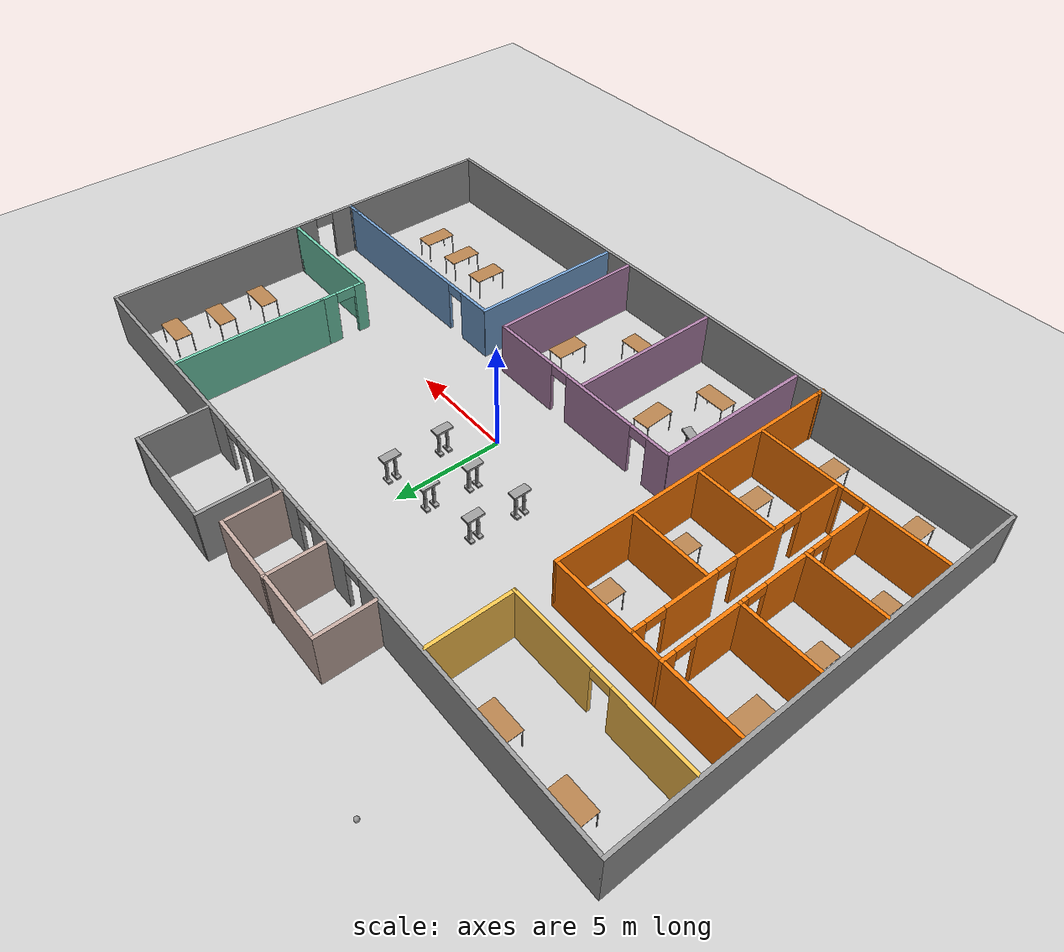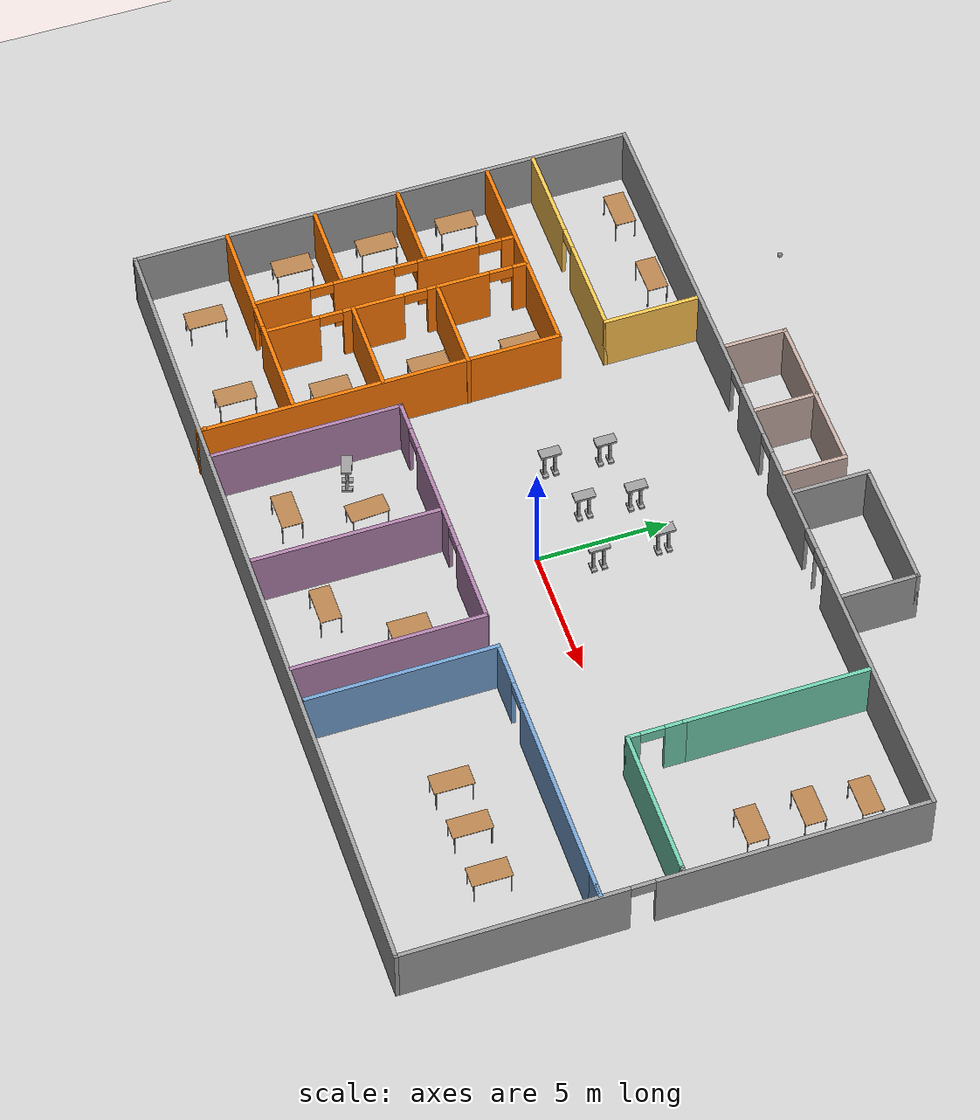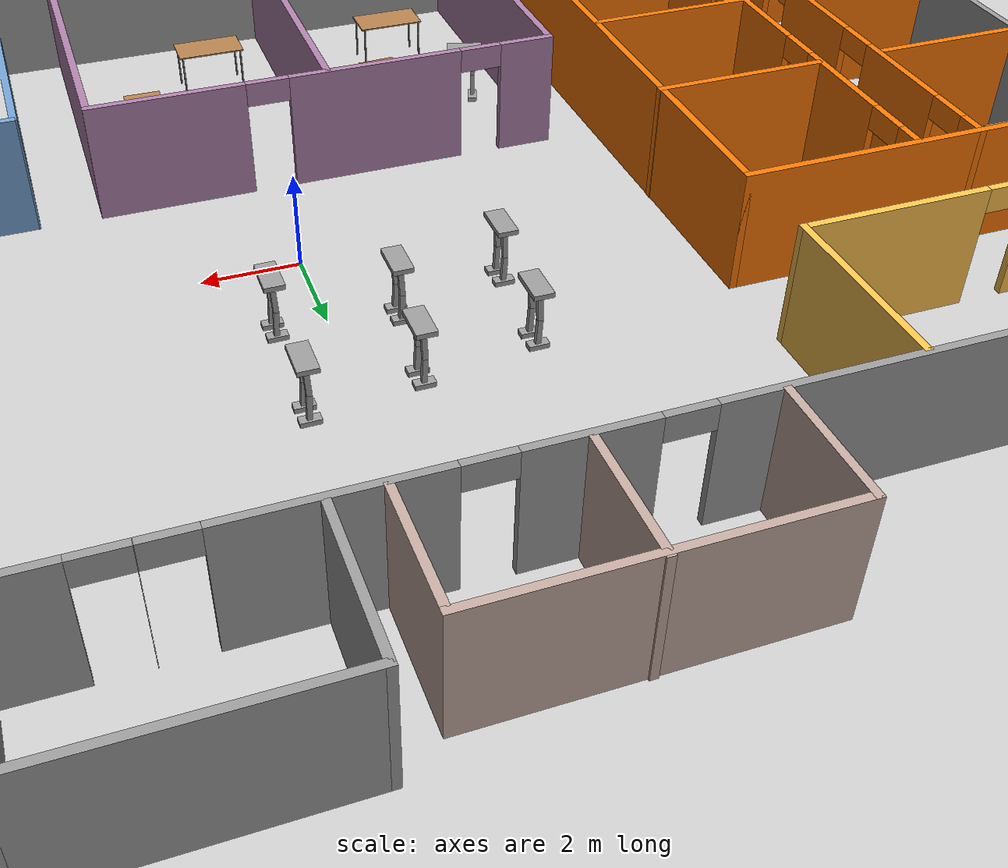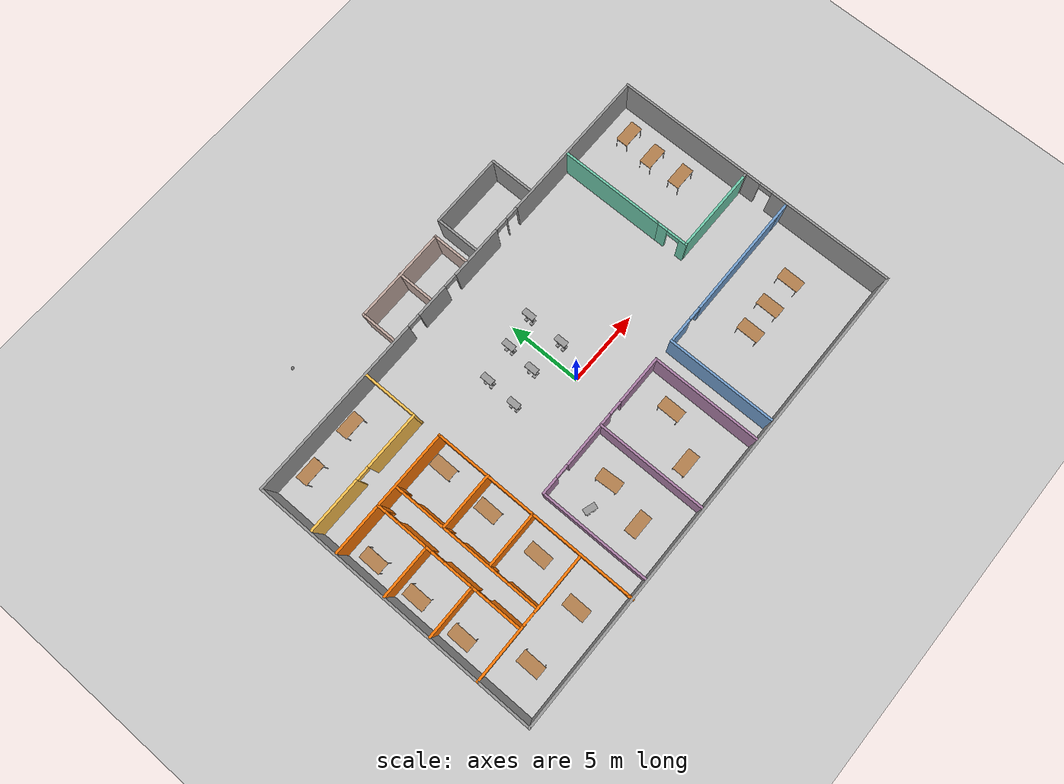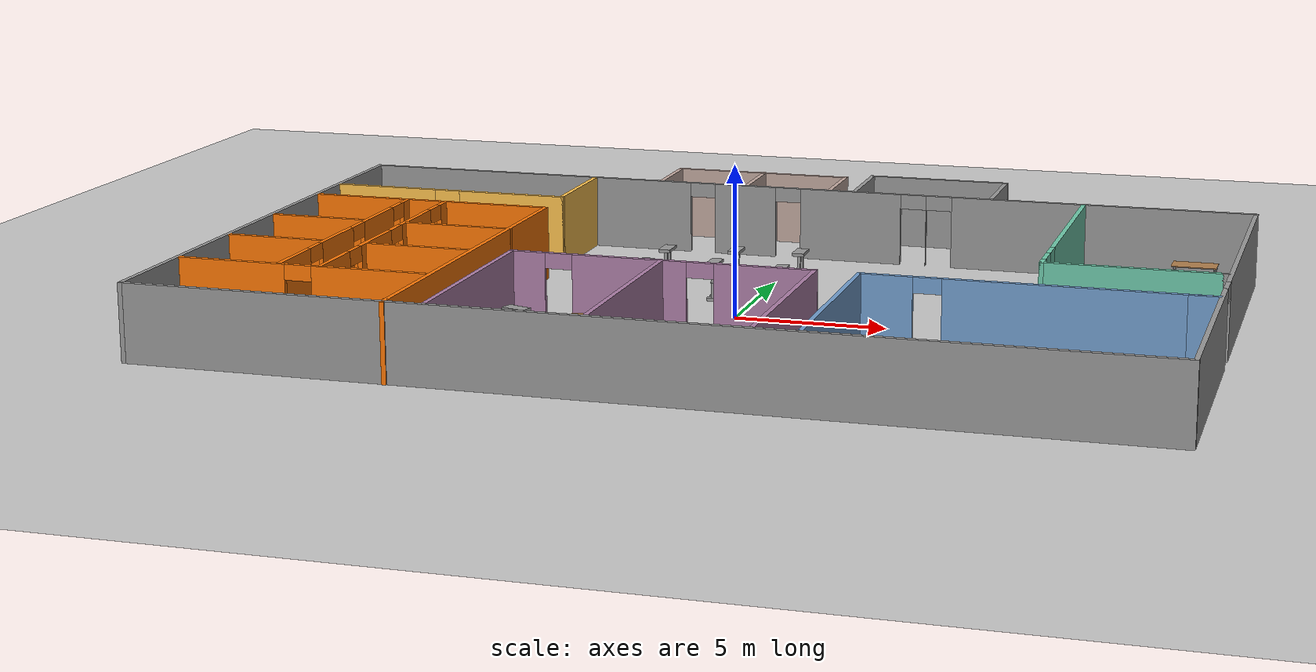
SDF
<sdf version="1.6">
 <world name="default">
  <plugin name="hello" filename="libhello.so"/>
  <light name="sun" type="directional">
   <pose>0 0 10 0 -0 0</pose>
   <diffuse>0.8 0.8 0.8 1</diffuse>
   <specular>0.2 0.2 0.2 1</specular>
   <attenuation>
    <range>1000</range>
    <constant>0.9</constant>
    <linear>0.01</linear>
    <quadratic>0.001</quadratic>
   </attenuation>
   <direction>-0.5 0.1 -0.9</direction>
  </light>
  <model name="ground_plane">
   <static>1</static>
   <link name="link">
    <collision name="collision">
     <geometry><plane><normal>0 0 1</normal><size>100 100</size></plane></geometry>
     <surface>
      <contact><collide_bitmask>65535</collide_bitmask></contact>
      <friction><ode><mu>100</mu><mu2>50</mu2></ode></friction>
     </surface>
    </collision>
    <visual name="visual">
     <cast_shadows>0</cast_shadows>
     <geometry><plane><normal>0 0 1</normal><size>100 100</size></plane></geometry>
     <material>
      <script><uri>file://media/materials/scripts/gazebo.material</uri><name>Gazebo/Grey</name></script>
     </material>
    </visual>
   </link>
  </model>
  <gravity>0 0 -9.8</gravity>
  <magnetic_field>6e-06 2.3e-05 -4.2e-05</magnetic_field>
  <atmosphere type="adiabatic"/>
  <physics name="default_physics" default="0" type="ode">
   <max_step_size>0.001</max_step_size>
   <real_time_factor>1</real_time_factor>
   <real_time_update_rate>1000</real_time_update_rate>
  </physics>
  <scene><ambient>0.4 0.4 0.4 1</ambient><background>0.7 0.7 0.7 1</background><shadows>1</shadows></scene>
  <audio><device>default</device></audio>
  <spherical_coordinates>
   <surface_model>EARTH_WGS84</surface_model>
   <latitude_deg>0</latitude_deg>
   <longitude_deg>0</longitude_deg>
   <elevation>0</elevation>
   <heading_deg>0</heading_deg>
  </spherical_coordinates>
  <model name="myBuilding">
   <pose>-0.25188 0.80761 0 0 -0 0</pose>
   <link name="Wall_105">
    <collision name="Wall_105_Collision">
     <geometry><box><size>2.5 0.15 2.5</size></box></geometry>
     <pose>0 0 1.25 0 -0 0</pose>
    </collision>
    <visual name="Wall_105_Visual">
     <pose>0 0 1.25 0 -0 0</pose>
     <geometry><box><size>2.5 0.15 2.5</size></box></geometry>
     <material>
      <script><uri>file://media/materials/scripts/gazebo.material</uri><name>Gazebo/Grey</name></script>
      <ambient>0.760784 0.662745 0.627451 1</ambient>
     </material>
     <meta><layer>0</layer></meta>
    </visual>
    <pose>-5.01832 9.47119 0 0 -0 1.5708</pose>
   </link>
   <link name="Wall_106">
    <collision name="Wall_106_Collision">
     <geometry><box><size>6.3289 0.15 2.5</size></box></geometry>
     <pose>0 0 1.25 0 -0 0</pose>
    </collision>
    <visual name="Wall_106_Visual">
     <pose>0 0 1.25 0 -0 0</pose>
     <geometry><box><size>6.3289 0.15 2.5</size></box></geometry>
     <material>
      <script><uri>file://media/materials/scripts/gazebo.material</uri><name>Gazebo/Grey</name></script>
      <ambient>0.760784 0.662745 0.627451 1</ambient>
     </material>
     <meta><layer>0</layer></meta>
    </visual>
    <pose>-1.92887 10.6462 0 0 -0 0</pose>
   </link>
   <link name="Wall_112">
    <collision name="Wall_112_Collision">
     <geometry><box><size>2.5 0.15 2.5</size></box></geometry>
     <pose>0 0 1.25 0 -0 0</pose>
    </collision>
    <visual name="Wall_112_Visual">
     <pose>0 0 1.25 0 -0 0</pose>
     <geometry><box><size>2.5 0.15 2.5</size></box></geometry>
     <material>
      <script><uri>file://media/materials/scripts/gazebo.material</uri><name>Gazebo/Grey</name></script>
      <ambient>0.760784 0.662745 0.627451 1</ambient>
     </material>
     <meta><layer>0</layer></meta>
    </visual>
    <pose>1.16058 9.47119 0 0 -0 -1.5708</pose>
   </link>
   <link name="Wall_119">
    <collision name="Wall_119_Collision">
     <geometry><box><size>2.5 0.15 2.5</size></box></geometry>
     <pose>0 0 1.25 0 -0 0</pose>
    </collision>
    <visual name="Wall_119_Visual">
     <pose>0 0 1.25 0 -0 0</pose>
     <geometry><box><size>2.5 0.15 2.5</size></box></geometry>
     <material>
      <script><uri>file://media/materials/scripts/gazebo.material</uri><name>Gazebo/Grey</name></script>
      <ambient>0.760784 0.662745 0.627451 1</ambient>
     </material>
     <meta><layer>0</layer></meta>
    </visual>
    <pose>-1.87489 9.50785 0 0 -0 -1.5708</pose>
   </link>
   <link name="Wall_121">
    <collision name="Wall_121_Collision">
     <geometry><box><size>8.5 0.15 2.5</size></box></geometry>
     <pose>0 0 1.25 0 -0 0</pose>
    </collision>
    <visual name="Wall_121_Visual">
     <pose>0 0 1.25 0 -0 0</pose>
     <geometry><box><size>8.5 0.15 2.5</size></box></geometry>
     <material>
      <script><uri>file://media/materials/scripts/gazebo.material</uri><name>Gazebo/Grey</name></script>
      <ambient>0.996078 0.47451 0.0196078 1</ambient>
     </material>
     <meta><layer>0</layer></meta>
    </visual>
    <pose>-11.6187 2.66208 0 0 -0 0</pose>
   </link>
   <link name="Wall_122">
    <collision name="Wall_122_Collision">
     <geometry><box><size>14 0.15 2.5</size></box></geometry>
     <pose>0 0 1.25 0 -0 0</pose>
    </collision>
    <visual name="Wall_122_Visual">
     <pose>0 0 1.25 0 -0 0</pose>
     <geometry><box><size>14 0.15 2.5</size></box></geometry>
     <material>
      <script><uri>file://media/materials/scripts/gazebo.material</uri><name>Gazebo/Grey</name></script>
      <ambient>0.996078 0.47451 0.0196078 1</ambient>
     </material>
     <meta><layer>0</layer></meta>
    </visual>
    <pose>-7.4437 -4.26292 0 0 -0 -1.5708</pose>
   </link>
   <link name="Wall_128">
    <pose>-11.7413 -7.56548 0 0 -0 0</pose>
    <visual name="Wall_128_Visual_0">
     <pose>-2.38371 0 1.25 0 -0 0</pose>
     <geometry><box><size>3.73259 0.15 2.5</size></box></geometry>
     <material>
      <script><uri>file://media/materials/scripts/gazebo.material</uri><name>Gazebo/Grey</name></script>
      <ambient>0.996078 0.47451 0.0196078 1</ambient>
     </material>
     <meta><layer>0</layer></meta>
    </visual>
    <collision name="Wall_128_Collision_0">
     <geometry><box><size>3.73259 0.15 2.5</size></box></geometry>
     <pose>-2.38371 0 1.25 0 -0 0</pose>
    </collision>
    <visual name="Wall_128_Visual_1">
     <pose>2.31629 0 1.25 0 -0 0</pose>
     <geometry><box><size>3.86741 0.15 2.5</size></box></geometry>
     <material>
      <script><uri>file://media/materials/scripts/gazebo.material</uri><name>Gazebo/Grey</name></script>
      <ambient>0.996078 0.47451 0.0196078 1</ambient>
     </material>
     <meta><layer>0</layer></meta>
    </visual>
    <collision name="Wall_128_Collision_1">
     <geometry><box><size>3.86741 0.15 2.5</size></box></geometry>
     <pose>2.31629 0 1.25 0 -0 0</pose>
    </collision>
    <visual name="Wall_128_Visual_2">
     <pose>-0.067411 0 2.25 0 -0 0</pose>
     <geometry><box><size>0.9 0.15 0.5</size></box></geometry>
     <material>
      <script><uri>file://media/materials/scripts/gazebo.material</uri><name>Gazebo/Grey</name></script>
      <ambient>0.996078 0.47451 0.0196078 1</ambient>
     </material>
     <meta><layer>0</layer></meta>
    </visual>
    <collision name="Wall_128_Collision_2">
     <geometry><box><size>0.9 0.15 0.5</size></box></geometry>
     <pose>-0.067411 0 2.25 0 -0 0</pose>
    </collision>
   </link>
   <link name="Wall_130">
    <pose>-12.4818 -2.38792 0 0 -0 -1.5708</pose>
    <visual name="Wall_130_Visual_0">
     <pose>-4.80532 0 1.25 0 -0 0</pose>
     <geometry><box><size>0.639365 0.15 2.5</size></box></geometry>
     <material>
      <script><uri>file://media/materials/scripts/gazebo.material</uri><name>Gazebo/Grey</name></script>
      <ambient>0.996078 0.47451 0.0196078 1</ambient>
     </material>
     <meta><layer>0</layer></meta>
    </visual>
    <collision name="Wall_130_Collision_0">
     <geometry><box><size>0.639365 0.15 2.5</size></box></geometry>
     <pose>-4.80532 0 1.25 0 -0 0</pose>
    </collision>
    <visual name="Wall_130_Visual_1">
     <pose>-2.38004 0 1.25 0 -0 0</pose>
     <geometry><box><size>2.4112 0.15 2.5</size></box></geometry>
     <material>
      <script><uri>file://media/materials/scripts/gazebo.material</uri><name>Gazebo/Grey</name></script>
      <ambient>0.996078 0.47451 0.0196078 1</ambient>
     </material>
     <meta><layer>0</layer></meta>
    </visual>
    <collision name="Wall_130_Collision_1">
     <geometry><box><size>2.4112 0.15 2.5</size></box></geometry>
     <pose>-2.38004 0 1.25 0 -0 0</pose>
    </collision>
    <visual name="Wall_130_Visual_2">
     <pose>0.916245 0 1.25 0 -0 0</pose>
     <geometry><box><size>2.38137 0.15 2.5</size></box></geometry>
     <material>
      <script><uri>file://media/materials/scripts/gazebo.material</uri><name>Gazebo/Grey</name></script>
      <ambient>0.996078 0.47451 0.0196078 1</ambient>
     </material>
     <meta><layer>0</layer></meta>
    </visual>
    <collision name="Wall_130_Collision_2">
     <geometry><box><size>2.38137 0.15 2.5</size></box></geometry>
     <pose>0.916245 0 1.25 0 -0 0</pose>
    </collision>
    <visual name="Wall_130_Visual_3">
     <pose>4.06596 0 1.25 0 -0 0</pose>
     <geometry><box><size>2.11807 0.15 2.5</size></box></geometry>
     <material>
      <script><uri>file://media/materials/scripts/gazebo.material</uri><name>Gazebo/Grey</name></script>
      <ambient>0.996078 0.47451 0.0196078 1</ambient>
     </material>
     <meta><layer>0</layer></meta>
    </visual>
    <collision name="Wall_130_Collision_3">
     <geometry><box><size>2.11807 0.15 2.5</size></box></geometry>
     <pose>4.06596 0 1.25 0 -0 0</pose>
    </collision>
    <visual name="Wall_130_Visual_4">
     <pose>-4.03564 0 2.25 0 -0 0</pose>
     <geometry><box><size>0.9 0.15 0.5</size></box></geometry>
     <material>
      <script><uri>file://media/materials/scripts/gazebo.material</uri><name>Gazebo/Grey</name></script>
      <ambient>0.996078 0.47451 0.0196078 1</ambient>
     </material>
     <meta><layer>0</layer></meta>
    </visual>
    <collision name="Wall_130_Collision_4">
     <geometry><box><size>0.9 0.15 0.5</size></box></geometry>
     <pose>-4.03564 0 2.25 0 -0 0</pose>
    </collision>
    <visual name="Wall_130_Visual_5">
     <pose>-0.724438 0 2.25 0 -0 0</pose>
     <geometry><box><size>0.9 0.15 0.5</size></box></geometry>
     <material>
      <script><uri>file://media/materials/scripts/gazebo.material</uri><name>Gazebo/Grey</name></script>
      <ambient>0.996078 0.47451 0.0196078 1</ambient>
     </material>
     <meta><layer>0</layer></meta>
    </visual>
    <collision name="Wall_130_Collision_5">
     <geometry><box><size>0.9 0.15 0.5</size></box></geometry>
     <pose>-0.724438 0 2.25 0 -0 0</pose>
    </collision>
    <visual name="Wall_130_Visual_6">
     <pose>2.55693 0 2.25 0 -0 0</pose>
     <geometry><box><size>0.9 0.15 0.5</size></box></geometry>
     <material>
      <script><uri>file://media/materials/scripts/gazebo.material</uri><name>Gazebo/Grey</name></script>
      <ambient>0.996078 0.47451 0.0196078 1</ambient>
     </material>
     <meta><layer>0</layer></meta>
    </visual>
    <collision name="Wall_130_Collision_6">
     <geometry><box><size>0.9 0.15 0.5</size></box></geometry>
     <pose>2.55693 0 2.25 0 -0 0</pose>
    </collision>
   </link>
   <link name="Wall_132">
    <pose>-11.1003 -2.44871 0 0 -0 -1.5708</pose>
    <visual name="Wall_132_Visual_0">
     <pose>-4.8208 0 1.25 0 -0 0</pose>
     <geometry><box><size>0.60841 0.15 2.5</size></box></geometry>
     <material>
      <script><uri>file://media/materials/scripts/gazebo.material</uri><name>Gazebo/Grey</name></script>
      <ambient>0.996078 0.47451 0.0196078 1</ambient>
     </material>
     <meta><layer>0</layer></meta>
    </visual>
    <collision name="Wall_132_Collision_0">
     <geometry><box><size>0.60841 0.15 2.5</size></box></geometry>
     <pose>-4.8208 0 1.25 0 -0 0</pose>
    </collision>
    <visual name="Wall_132_Visual_1">
     <pose>-2.39608 0 1.25 0 -0 0</pose>
     <geometry><box><size>2.44103 0.15 2.5</size></box></geometry>
     <material>
      <script><uri>file://media/materials/scripts/gazebo.material</uri><name>Gazebo/Grey</name></script>
      <ambient>0.996078 0.47451 0.0196078 1</ambient>
     </material>
     <meta><layer>0</layer></meta>
    </visual>
    <collision name="Wall_132_Collision_1">
     <geometry><box><size>2.44103 0.15 2.5</size></box></geometry>
     <pose>-2.39608 0 1.25 0 -0 0</pose>
    </collision>
    <visual name="Wall_132_Visual_2">
     <pose>0.915121 0 1.25 0 -0 0</pose>
     <geometry><box><size>2.38137 0.15 2.5</size></box></geometry>
     <material>
      <script><uri>file://media/materials/scripts/gazebo.material</uri><name>Gazebo/Grey</name></script>
      <ambient>0.996078 0.47451 0.0196078 1</ambient>
     </material>
     <meta><layer>0</layer></meta>
    </visual>
    <collision name="Wall_132_Collision_2">
     <geometry><box><size>2.38137 0.15 2.5</size></box></geometry>
     <pose>0.915121 0 1.25 0 -0 0</pose>
    </collision>
    <visual name="Wall_132_Visual_3">
     <pose>4.0654 0 1.25 0 -0 0</pose>
     <geometry><box><size>2.1192 0.15 2.5</size></box></geometry>
     <material>
      <script><uri>file://media/materials/scripts/gazebo.material</uri><name>Gazebo/Grey</name></script>
      <ambient>0.996078 0.47451 0.0196078 1</ambient>
     </material>
     <meta><layer>0</layer></meta>
    </visual>
    <collision name="Wall_132_Collision_3">
     <geometry><box><size>2.1192 0.15 2.5</size></box></geometry>
     <pose>4.0654 0 1.25 0 -0 0</pose>
    </collision>
    <visual name="Wall_132_Visual_4">
     <pose>-4.06659 0 2.25 0 -0 0</pose>
     <geometry><box><size>0.9 0.15 0.5</size></box></geometry>
     <material>
      <script><uri>file://media/materials/scripts/gazebo.material</uri><name>Gazebo/Grey</name></script>
      <ambient>0.996078 0.47451 0.0196078 1</ambient>
     </material>
     <meta><layer>0</layer></meta>
    </visual>
    <collision name="Wall_132_Collision_4">
     <geometry><box><size>0.9 0.15 0.5</size></box></geometry>
     <pose>-4.06659 0 2.25 0 -0 0</pose>
    </collision>
    <visual name="Wall_132_Visual_5">
     <pose>-0.725562 0 2.25 0 -0 0</pose>
     <geometry><box><size>0.9 0.15 0.5</size></box></geometry>
     <material>
      <script><uri>file://media/materials/scripts/gazebo.material</uri><name>Gazebo/Grey</name></script>
      <ambient>0.996078 0.47451 0.0196078 1</ambient>
     </material>
     <meta><layer>0</layer></meta>
    </visual>
    <collision name="Wall_132_Collision_5">
     <geometry><box><size>0.9 0.15 0.5</size></box></geometry>
     <pose>-0.725562 0 2.25 0 -0 0</pose>
    </collision>
    <visual name="Wall_132_Visual_6">
     <pose>2.5558 0 2.25 0 -0 0</pose>
     <geometry><box><size>0.9 0.15 0.5</size></box></geometry>
     <material>
      <script><uri>file://media/materials/scripts/gazebo.material</uri><name>Gazebo/Grey</name></script>
      <ambient>0.996078 0.47451 0.0196078 1</ambient>
     </material>
     <meta><layer>0</layer></meta>
    </visual>
    <collision name="Wall_132_Collision_6">
     <geometry><box><size>0.9 0.15 0.5</size></box></geometry>
     <pose>2.5558 0 2.25 0 -0 0</pose>
    </collision>
   </link>
   <link name="Wall_134">
    <collision name="Wall_134_Collision">
     <geometry><box><size>3.5 0.15 2.5</size></box></geometry>
     <pose>0 0 1.25 0 -0 0</pose>
    </collision>
    <visual name="Wall_134_Visual">
     <pose>0 0 1.25 0 -0 0</pose>
     <geometry><box><size>3.5 0.15 2.5</size></box></geometry>
     <material>
      <script><uri>file://media/materials/scripts/gazebo.material</uri><name>Gazebo/Grey</name></script>
      <ambient>0.996078 0.47451 0.0196078 1</ambient>
     </material>
     <meta><layer>0</layer></meta>
    </visual>
    <pose>-14.1641 -0.876675 0 0 -0 0</pose>
   </link>
   <link name="Wall_136">
    <collision name="Wall_136_Collision">
     <geometry><box><size>3.5 0.15 2.5</size></box></geometry>
     <pose>0 0 1.25 0 -0 0</pose>
    </collision>
    <visual name="Wall_136_Visual">
     <pose>0 0 1.25 0 -0 0</pose>
     <geometry><box><size>3.5 0.15 2.5</size></box></geometry>
     <material>
      <script><uri>file://media/materials/scripts/gazebo.material</uri><name>Gazebo/Grey</name></script>
      <ambient>0.996078 0.47451 0.0196078 1</ambient>
     </material>
     <meta><layer>0</layer></meta>
    </visual>
    <pose>-14.1641 -4.14321 0 0 -0 0</pose>
   </link>
   <link name="Wall_141">
    <collision name="Wall_141_Collision">
     <geometry><box><size>3.75 0.15 2.5</size></box></geometry>
     <pose>0 0 1.25 0 -0 0</pose>
    </collision>
    <visual name="Wall_141_Visual">
     <pose>0 0 1.25 0 -0 0</pose>
     <geometry><box><size>3.75 0.15 2.5</size></box></geometry>
     <material>
      <script><uri>file://media/materials/scripts/gazebo.material</uri><name>Gazebo/Grey</name></script>
      <ambient>0.996078 0.47451 0.0196078 1</ambient>
     </material>
     <meta><layer>0</layer></meta>
    </visual>
    <pose>-9.22611 -0.867546 0 0 -0 0</pose>
   </link>
   <link name="Wall_143">
    <collision name="Wall_143_Collision">
     <geometry><box><size>3.75 0.15 2.5</size></box></geometry>
     <pose>0 0 1.25 0 -0 0</pose>
    </collision>
    <visual name="Wall_143_Visual">
     <pose>0 0 1.25 0 -0 0</pose>
     <geometry><box><size>3.75 0.15 2.5</size></box></geometry>
     <material>
      <script><uri>file://media/materials/scripts/gazebo.material</uri><name>Gazebo/Grey</name></script>
      <ambient>0.996078 0.47451 0.0196078 1</ambient>
     </material>
     <meta><layer>0</layer></meta>
    </visual>
    <pose>-9.29018 -4.14114 0 0 -0 0</pose>
   </link>
   <link name="Wall_145">
    <pose>-11.6907 4.51145 0 0 -0 0</pose>
    <visual name="Wall_145_Visual_0">
     <pose>-2.37919 0 1.25 0 -0 0</pose>
     <geometry><box><size>3.74162 0.15 2.5</size></box></geometry>
     <material>
      <script><uri>file://media/materials/scripts/gazebo.material</uri><name>Gazebo/Grey</name></script>
      <ambient>1 0.764706 0.305882 1</ambient>
     </material>
     <meta><layer>0</layer></meta>
    </visual>
    <collision name="Wall_145_Collision_0">
     <geometry><box><size>3.74162 0.15 2.5</size></box></geometry>
     <pose>-2.37919 0 1.25 0 -0 0</pose>
    </collision>
    <visual name="Wall_145_Visual_1">
     <pose>2.32081 0 1.25 0 -0 0</pose>
     <geometry><box><size>3.85838 0.15 2.5</size></box></geometry>
     <material>
      <script><uri>file://media/materials/scripts/gazebo.material</uri><name>Gazebo/Grey</name></script>
      <ambient>1 0.764706 0.305882 1</ambient>
     </material>
     <meta><layer>0</layer></meta>
    </visual>
    <collision name="Wall_145_Collision_1">
     <geometry><box><size>3.85838 0.15 2.5</size></box></geometry>
     <pose>2.32081 0 1.25 0 -0 0</pose>
    </collision>
    <visual name="Wall_145_Visual_2">
     <pose>-0.058376 0 2.25 0 -0 0</pose>
     <geometry><box><size>0.9 0.15 0.5</size></box></geometry>
     <material>
      <script><uri>file://media/materials/scripts/gazebo.material</uri><name>Gazebo/Grey</name></script>
      <ambient>1 0.764706 0.305882 1</ambient>
     </material>
     <meta><layer>0</layer></meta>
    </visual>
    <collision name="Wall_145_Collision_2">
     <geometry><box><size>0.9 0.15 0.5</size></box></geometry>
     <pose>-0.058376 0 2.25 0 -0 0</pose>
    </collision>
   </link>
   <link name="Wall_146">
    <collision name="Wall_146_Collision">
     <geometry><box><size>3.75 0.15 2.5</size></box></geometry>
     <pose>0 0 1.25 0 -0 0</pose>
    </collision>
    <visual name="Wall_146_Visual">
     <pose>0 0 1.25 0 -0 0</pose>
     <geometry><box><size>3.75 0.15 2.5</size></box></geometry>
     <material>
      <script><uri>file://media/materials/scripts/gazebo.material</uri><name>Gazebo/Grey</name></script>
      <ambient>1 0.764706 0.305882 1</ambient>
     </material>
     <meta><layer>0</layer></meta>
    </visual>
    <pose>-7.51571 6.31145 0 0 -0 1.5708</pose>
   </link>
   <link name="Wall_149">
    <collision name="Wall_149_Collision">
     <geometry><box><size>7.29417 0.15 2.5</size></box></geometry>
     <pose>0 0 1.25 0 -0 0</pose>
    </collision>
    <visual name="Wall_149_Visual">
     <pose>0 0 1.25 0 -0 0</pose>
     <geometry><box><size>7.29417 0.15 2.5</size></box></geometry>
     <material>
      <script><uri>file://media/materials/scripts/gazebo.material</uri><name>Gazebo/Grey</name></script>
      <ambient>0.678431 0.498039 0.658824 1</ambient>
     </material>
     <meta><layer>0</layer></meta>
    </visual>
    <pose>-6.20221 -7.45674 0 0 -0 1.5708</pose>
   </link>
   <link name="Wall_150">
    <pose>-1.27721 -3.85035 0 0 -0 0</pose>
    <visual name="Wall_150_Visual_0">
     <pose>-4.40031 0 1.25 0 -0 0</pose>
     <geometry><box><size>1.19937 0.15 2.5</size></box></geometry>
     <material>
      <script><uri>file://media/materials/scripts/gazebo.material</uri><name>Gazebo/Grey</name></script>
      <ambient>0.678431 0.498039 0.658824 1</ambient>
     </material>
     <meta><layer>0</layer></meta>
    </visual>
    <collision name="Wall_150_Collision_0">
     <geometry><box><size>1.19937 0.15 2.5</size></box></geometry>
     <pose>-4.40031 0 1.25 0 -0 0</pose>
    </collision>
    <visual name="Wall_150_Visual_1">
     <pose>-1.03503 0 1.25 0 -0 0</pose>
     <geometry><box><size>3.7312 0.15 2.5</size></box></geometry>
     <material>
      <script><uri>file://media/materials/scripts/gazebo.material</uri><name>Gazebo/Grey</name></script>
      <ambient>0.678431 0.498039 0.658824 1</ambient>
     </material>
     <meta><layer>0</layer></meta>
    </visual>
    <collision name="Wall_150_Collision_1">
     <geometry><box><size>3.7312 0.15 2.5</size></box></geometry>
     <pose>-1.03503 0 1.25 0 -0 0</pose>
    </collision>
    <visual name="Wall_150_Visual_2">
     <pose>3.36529 0 1.25 0 -0 0</pose>
     <geometry><box><size>3.26943 0.15 2.5</size></box></geometry>
     <material>
      <script><uri>file://media/materials/scripts/gazebo.material</uri><name>Gazebo/Grey</name></script>
      <ambient>0.678431 0.498039 0.658824 1</ambient>
     </material>
     <meta><layer>0</layer></meta>
    </visual>
    <collision name="Wall_150_Collision_2">
     <geometry><box><size>3.26943 0.15 2.5</size></box></geometry>
     <pose>3.36529 0 1.25 0 -0 0</pose>
    </collision>
    <visual name="Wall_150_Visual_3">
     <pose>-3.35063 0 2.25 0 -0 0</pose>
     <geometry><box><size>0.9 0.15 0.5</size></box></geometry>
     <material>
      <script><uri>file://media/materials/scripts/gazebo.material</uri><name>Gazebo/Grey</name></script>
      <ambient>0.678431 0.498039 0.658824 1</ambient>
     </material>
     <meta><layer>0</layer></meta>
    </visual>
    <collision name="Wall_150_Collision_3">
     <geometry><box><size>0.9 0.15 0.5</size></box></geometry>
     <pose>-3.35063 0 2.25 0 -0 0</pose>
    </collision>
    <visual name="Wall_150_Visual_4">
     <pose>1.28057 0 2.25 0 -0 0</pose>
     <geometry><box><size>0.9 0.15 0.5</size></box></geometry>
     <material>
      <script><uri>file://media/materials/scripts/gazebo.material</uri><name>Gazebo/Grey</name></script>
      <ambient>0.678431 0.498039 0.658824 1</ambient>
     </material>
     <meta><layer>0</layer></meta>
    </visual>
    <collision name="Wall_150_Collision_4">
     <geometry><box><size>0.9 0.15 0.5</size></box></geometry>
     <pose>1.28057 0 2.25 0 -0 0</pose>
    </collision>
   </link>
   <link name="Wall_151">
    <collision name="Wall_151_Collision">
     <geometry><box><size>7.29417 0.15 2.5</size></box></geometry>
     <pose>0 0 1.25 0 -0 0</pose>
    </collision>
    <visual name="Wall_151_Visual">
     <pose>0 0 1.25 0 -0 0</pose>
     <geometry><box><size>7.29417 0.15 2.5</size></box></geometry>
     <material>
      <script><uri>file://media/materials/scripts/gazebo.material</uri><name>Gazebo/Grey</name></script>
      <ambient>0.678431 0.498039 0.658824 1</ambient>
     </material>
     <meta><layer>0</layer></meta>
    </visual>
    <pose>3.64779 -7.45674 0 0 -0 -1.5708</pose>
   </link>
   <link name="Wall_153">
    <collision name="Wall_153_Collision">
     <geometry><box><size>7.25 0.15 2.5</size></box></geometry>
     <pose>0 0 1.25 0 -0 0</pose>
    </collision>
    <visual name="Wall_153_Visual">
     <pose>0 0 1.25 0 -0 0</pose>
     <geometry><box><size>7.25 0.15 2.5</size></box></geometry>
     <material>
      <script><uri>file://media/materials/scripts/gazebo.material</uri><name>Gazebo/Grey</name></script>
      <ambient>0.678431 0.498039 0.658824 1</ambient>
     </material>
     <meta><layer>0</layer></meta>
    </visual>
    <pose>-1.26593 -7.43583 0 0 -0 -1.5708</pose>
   </link>
   <link name="Wall_155">
    <collision name="Wall_155_Collision">
     <geometry><box><size>3 0.15 2.5</size></box></geometry>
     <pose>0 0 1.25 0 -0 0</pose>
    </collision>
    <visual name="Wall_155_Visual">
     <pose>0 0 1.25 0 -0 0</pose>
     <geometry><box><size>3 0.15 2.5</size></box></geometry>
     <material>
      <script><uri>file://media/materials/scripts/gazebo.material</uri><name>Gazebo/Grey</name></script>
      <ambient>0.180392 0.203922 0.211765 1</ambient>
     </material>
     <meta><layer>0</layer></meta>
    </visual>
    <pose>2.05464 9.76292 0 0 -0 1.5708</pose>
   </link>
   <link name="Wall_156">
    <collision name="Wall_156_Collision">
     <geometry><box><size>5 0.15 2.5</size></box></geometry>
     <pose>0 0 1.25 0 -0 0</pose>
    </collision>
    <visual name="Wall_156_Visual">
     <pose>0 0 1.25 0 -0 0</pose>
     <geometry><box><size>5 0.15 2.5</size></box></geometry>
     <material>
      <script><uri>file://media/materials/scripts/gazebo.material</uri><name>Gazebo/Grey</name></script>
      <ambient>0.180392 0.203922 0.211765 1</ambient>
     </material>
     <meta><layer>0</layer></meta>
    </visual>
    <pose>4.47964 11.1879 0 0 -0 0</pose>
   </link>
   <link name="Wall_157">
    <collision name="Wall_157_Collision">
     <geometry><box><size>3 0.15 2.5</size></box></geometry>
     <pose>0 0 1.25 0 -0 0</pose>
    </collision>
    <visual name="Wall_157_Visual">
     <pose>0 0 1.25 0 -0 0</pose>
     <geometry><box><size>3 0.15 2.5</size></box></geometry>
     <material>
      <script><uri>file://media/materials/scripts/gazebo.material</uri><name>Gazebo/Grey</name></script>
      <ambient>0.180392 0.203922 0.211765 1</ambient>
     </material>
     <meta><layer>0</layer></meta>
    </visual>
    <pose>6.90463 9.76292 0 0 -0 -1.5708</pose>
   </link>
   <link name="Wall_22">
    <collision name="Wall_22_Collision">
     <geometry><box><size>19.5 0.15 2.5</size></box></geometry>
     <pose>0 0 1.25 0 -0 0</pose>
    </collision>
    <visual name="Wall_22_Visual">
     <pose>0 0 1.25 0 -0 0</pose>
     <geometry><box><size>19.5 0.15 2.5</size></box></geometry>
     <material>
      <script><uri>file://media/materials/scripts/gazebo.material</uri><name>Gazebo/Grey</name></script>
      <ambient>1 1 1 1</ambient>
     </material>
     <meta><layer>0</layer></meta>
    </visual>
    <pose>-15.925 -1.47174 0 0 -0 1.5708</pose>
   </link>
   <link name="Wall_24">
    <pose>-0 8.20326 0 0 -0 0</pose>
    <visual name="Wall_24_Visual_0">
     <pose>-9.95172 0 1.25 0 -0 0</pose>
     <geometry><box><size>12.0966 0.15 2.5</size></box></geometry>
     <material>
      <script><uri>file://media/materials/scripts/gazebo.material</uri><name>Gazebo/Grey</name></script>
      <ambient>1 1 1 1</ambient>
     </material>
     <meta><layer>0</layer></meta>
    </visual>
    <collision name="Wall_24_Collision_0">
     <geometry><box><size>12.0966 0.15 2.5</size></box></geometry>
     <pose>-9.95172 0 1.25 0 -0 0</pose>
    </collision>
    <visual name="Wall_24_Visual_1">
     <pose>-1.88822 0 1.25 0 -0 0</pose>
     <geometry><box><size>2.23043 0.15 2.5</size></box></geometry>
     <material>
      <script><uri>file://media/materials/scripts/gazebo.material</uri><name>Gazebo/Grey</name></script>
      <ambient>1 1 1 1</ambient>
     </material>
     <meta><layer>0</layer></meta>
    </visual>
    <collision name="Wall_24_Collision_1">
     <geometry><box><size>2.23043 0.15 2.5</size></box></geometry>
     <pose>-1.88822 0 1.25 0 -0 0</pose>
    </collision>
    <visual name="Wall_24_Visual_2">
     <pose>1.93081 0 1.25 0 -0 0</pose>
     <geometry><box><size>3.60763 0.15 2.5</size></box></geometry>
     <material>
      <script><uri>file://media/materials/scripts/gazebo.material</uri><name>Gazebo/Grey</name></script>
      <ambient>1 1 1 1</ambient>
     </material>
     <meta><layer>0</layer></meta>
    </visual>
    <collision name="Wall_24_Collision_2">
     <geometry><box><size>3.60763 0.15 2.5</size></box></geometry>
     <pose>1.93081 0 1.25 0 -0 0</pose>
    </collision>
    <visual name="Wall_24_Visual_3">
     <pose>4.63831 0 1.25 0 -0 0</pose>
     <geometry><box><size>0.007372 0.15 2.5</size></box></geometry>
     <material>
      <script><uri>file://media/materials/scripts/gazebo.material</uri><name>Gazebo/Grey</name></script>
      <ambient>1 1 1 1</ambient>
     </material>
     <meta><layer>0</layer></meta>
    </visual>
    <collision name="Wall_24_Collision_3">
     <geometry><box><size>0.007372 0.15 2.5</size></box></geometry>
     <pose>4.63831 0 1.25 0 -0 0</pose>
    </collision>
    <visual name="Wall_24_Visual_4">
     <pose>10.771 0 1.25 0 -0 0</pose>
     <geometry><box><size>10.458 0.15 2.5</size></box></geometry>
     <material>
      <script><uri>file://media/materials/scripts/gazebo.material</uri><name>Gazebo/Grey</name></script>
      <ambient>1 1 1 1</ambient>
     </material>
     <meta><layer>0</layer></meta>
    </visual>
    <collision name="Wall_24_Collision_4">
     <geometry><box><size>10.458 0.15 2.5</size></box></geometry>
     <pose>10.771 0 1.25 0 -0 0</pose>
    </collision>
    <visual name="Wall_24_Visual_5">
     <pose>-3.45344 0 2.25 0 -0 0</pose>
     <geometry><box><size>0.9 0.15 0.5</size></box></geometry>
     <material>
      <script><uri>file://media/materials/scripts/gazebo.material</uri><name>Gazebo/Grey</name></script>
      <ambient>1 1 1 1</ambient>
     </material>
     <meta><layer>0</layer></meta>
    </visual>
    <collision name="Wall_24_Collision_5">
     <geometry><box><size>0.9 0.15 0.5</size></box></geometry>
     <pose>-3.45344 0 2.25 0 -0 0</pose>
    </collision>
    <visual name="Wall_24_Visual_6">
     <pose>-0.323003 0 2.25 0 -0 0</pose>
     <geometry><box><size>0.9 0.15 0.5</size></box></geometry>
     <material>
      <script><uri>file://media/materials/scripts/gazebo.material</uri><name>Gazebo/Grey</name></script>
      <ambient>1 1 1 1</ambient>
     </material>
     <meta><layer>0</layer></meta>
    </visual>
    <collision name="Wall_24_Collision_6">
     <geometry><box><size>0.9 0.15 0.5</size></box></geometry>
     <pose>-0.323003 0 2.25 0 -0 0</pose>
    </collision>
    <visual name="Wall_24_Visual_7">
     <pose>4.18463 0 2.25 0 -0 0</pose>
     <geometry><box><size>0.9 0.15 0.5</size></box></geometry>
     <material>
      <script><uri>file://media/materials/scripts/gazebo.material</uri><name>Gazebo/Grey</name></script>
      <ambient>1 1 1 1</ambient>
     </material>
     <meta><layer>0</layer></meta>
    </visual>
    <collision name="Wall_24_Collision_7">
     <geometry><box><size>0.9 0.15 0.5</size></box></geometry>
     <pose>4.18463 0 2.25 0 -0 0</pose>
    </collision>
    <visual name="Wall_24_Visual_8">
     <pose>5.092 0 2.25 0 -0 0</pose>
     <geometry><box><size>0.9 0.15 0.5</size></box></geometry>
     <material>
      <script><uri>file://media/materials/scripts/gazebo.material</uri><name>Gazebo/Grey</name></script>
      <ambient>1 1 1 1</ambient>
     </material>
     <meta><layer>0</layer></meta>
    </visual>
    <collision name="Wall_24_Collision_8">
     <geometry><box><size>0.9 0.15 0.5</size></box></geometry>
     <pose>5.092 0 2.25 0 -0 0</pose>
    </collision>
   </link>
   <link name="Wall_25">
    <pose>15.925 -1.47174 0 0 -0 -1.5708</pose>
    <visual name="Wall_25_Visual_0">
     <pose>-4.66108 0 1.25 0 -0 0</pose>
     <geometry><box><size>10.1778 0.15 2.5</size></box></geometry>
     <material>
      <script><uri>file://media/materials/scripts/gazebo.material</uri><name>Gazebo/Grey</name></script>
      <ambient>1 1 1 1</ambient>
     </material>
     <meta><layer>0</layer></meta>
    </visual>
    <collision name="Wall_25_Collision_0">
     <geometry><box><size>10.1778 0.15 2.5</size></box></geometry>
     <pose>-4.66108 0 1.25 0 -0 0</pose>
    </collision>
    <visual name="Wall_25_Visual_1">
     <pose>5.53892 0 1.25 0 -0 0</pose>
     <geometry><box><size>8.42215 0.15 2.5</size></box></geometry>
     <material>
      <script><uri>file://media/materials/scripts/gazebo.material</uri><name>Gazebo/Grey</name></script>
      <ambient>1 1 1 1</ambient>
     </material>
     <meta><layer>0</layer></meta>
    </visual>
    <collision name="Wall_25_Collision_1">
     <geometry><box><size>8.42215 0.15 2.5</size></box></geometry>
     <pose>5.53892 0 1.25 0 -0 0</pose>
    </collision>
    <visual name="Wall_25_Visual_2">
     <pose>0.877846 0 2.25 0 -0 0</pose>
     <geometry><box><size>0.9 0.15 0.5</size></box></geometry>
     <material>
      <script><uri>file://media/materials/scripts/gazebo.material</uri><name>Gazebo/Grey</name></script>
      <ambient>1 1 1 1</ambient>
     </material>
     <meta><layer>0</layer></meta>
    </visual>
    <collision name="Wall_25_Collision_2">
     <geometry><box><size>0.9 0.15 0.5</size></box></geometry>
     <pose>0.877846 0 2.25 0 -0 0</pose>
    </collision>
   </link>
   <link name="Wall_26">
    <collision name="Wall_26_Collision">
     <geometry><box><size>32 0.15 2.5</size></box></geometry>
     <pose>0 0 1.25 0 -0 0</pose>
    </collision>
    <visual name="Wall_26_Visual">
     <pose>0 0 1.25 0 -0 0</pose>
     <geometry><box><size>32 0.15 2.5</size></box></geometry>
     <material>
      <script><uri>file://media/materials/scripts/gazebo.material</uri><name>Gazebo/Grey</name></script>
      <ambient>1 1 1 1</ambient>
     </material>
     <meta><layer>0</layer></meta>
    </visual>
    <pose>-0 -11.1467 0 0 -0 3.14159</pose>
   </link>
   <link name="Wall_44">
    <collision name="Wall_44_Collision">
     <geometry><box><size>7 0.15 2.5</size></box></geometry>
     <pose>0 0 1.25 0 -0 0</pose>
    </collision>
    <visual name="Wall_44_Visual">
     <pose>0 0 1.25 0 -0 0</pose>
     <geometry><box><size>7 0.15 2.5</size></box></geometry>
     <material>
      <script><uri>file://media/materials/scripts/gazebo.material</uri><name>Gazebo/Grey</name></script>
      <ambient>0.435294 0.796078 0.67451 1</ambient>
     </material>
     <meta><layer>0</layer></meta>
    </visual>
    <pose>10.126 4.65683 0 0 -0 -1.5708</pose>
   </link>
   <link name="Wall_55">
    <collision name="Wall_55_Collision">
     <geometry><box><size>0.15 0.15 2.5</size></box></geometry>
     <pose>0 0 1.25 0 -0 0</pose>
    </collision>
    <visual name="Wall_55_Visual">
     <pose>0 0 1.25 0 -0 0</pose>
     <geometry><box><size>0.15 0.15 2.5</size></box></geometry>
     <material>
      <script><uri>file://media/materials/scripts/gazebo.material</uri><name>Gazebo/Grey</name></script>
      <ambient>0.996078 0.47451 0.0196078 1</ambient>
     </material>
     <meta><layer>0</layer></meta>
    </visual>
    <pose>-7.47475 -10.9231 0 0 -0 0</pose>
   </link>
   <link name="Wall_70">
    <pose>10.126 0.18183 0 0 -0 -1.5708</pose>
    <visual name="Wall_70_Visual_0">
     <pose>-0.720365 0 1.25 0 -0 0</pose>
     <geometry><box><size>0.809269 0.15 2.5</size></box></geometry>
     <material>
      <script><uri>file://media/materials/scripts/gazebo.material</uri><name>Gazebo/Grey</name></script>
      <ambient>0.435294 0.796078 0.67451 1</ambient>
     </material>
     <meta><layer>0</layer></meta>
    </visual>
    <collision name="Wall_70_Collision_0">
     <geometry><box><size>0.809269 0.15 2.5</size></box></geometry>
     <pose>-0.720365 0 1.25 0 -0 0</pose>
    </collision>
    <visual name="Wall_70_Visual_1">
     <pose>0.854635 0 1.25 0 -0 0</pose>
     <geometry><box><size>0.540731 0.15 2.5</size></box></geometry>
     <material>
      <script><uri>file://media/materials/scripts/gazebo.material</uri><name>Gazebo/Grey</name></script>
      <ambient>0.435294 0.796078 0.67451 1</ambient>
     </material>
     <meta><layer>0</layer></meta>
    </visual>
    <collision name="Wall_70_Collision_1">
     <geometry><box><size>0.540731 0.15 2.5</size></box></geometry>
     <pose>0.854635 0 1.25 0 -0 0</pose>
    </collision>
    <visual name="Wall_70_Visual_2">
     <pose>0.134269 0 2.25 0 -0 0</pose>
     <geometry><box><size>0.9 0.15 0.5</size></box></geometry>
     <material>
      <script><uri>file://media/materials/scripts/gazebo.material</uri><name>Gazebo/Grey</name></script>
      <ambient>0.435294 0.796078 0.67451 1</ambient>
     </material>
     <meta><layer>0</layer></meta>
    </visual>
    <collision name="Wall_70_Collision_2">
     <geometry><box><size>0.9 0.15 0.5</size></box></geometry>
     <pose>0.134269 0 2.25 0 -0 0</pose>
    </collision>
   </link>
   <link name="Wall_71">
    <collision name="Wall_71_Collision">
     <geometry><box><size>5.75 0.15 2.5</size></box></geometry>
     <pose>0 0 1.25 0 -0 0</pose>
    </collision>
    <visual name="Wall_71_Visual">
     <pose>0 0 1.25 0 -0 0</pose>
     <geometry><box><size>5.75 0.15 2.5</size></box></geometry>
     <material>
      <script><uri>file://media/materials/scripts/gazebo.material</uri><name>Gazebo/Grey</name></script>
      <ambient>0.435294 0.796078 0.67451 1</ambient>
     </material>
     <meta><layer>0</layer></meta>
    </visual>
    <pose>12.926 -0.86817 0 0 -0 0</pose>
   </link>
   <link name="Wall_72">
    <collision name="Wall_72_Collision">
     <geometry><box><size>0.25 0.15 2.5</size></box></geometry>
     <pose>0 0 1.25 0 -0 0</pose>
    </collision>
    <visual name="Wall_72_Visual">
     <pose>0 0 1.25 0 -0 0</pose>
     <geometry><box><size>0.25 0.15 2.5</size></box></geometry>
     <material>
      <script><uri>file://media/materials/scripts/gazebo.material</uri><name>Gazebo/Grey</name></script>
      <ambient>1 1 1 1</ambient>
     </material>
     <meta><layer>0</layer></meta>
    </visual>
    <pose>15.776 -0.86817 0 0 -0 0</pose>
   </link>
   <link name="Wall_74">
    <collision name="Wall_74_Collision">
     <geometry><box><size>0.15 0.15 2.5</size></box></geometry>
     <pose>0 0 1.25 0 -0 0</pose>
    </collision>
    <visual name="Wall_74_Visual">
     <pose>0 0 1.25 0 -0 0</pose>
     <geometry><box><size>0.15 0.15 2.5</size></box></geometry>
     <material>
      <script><uri>file://media/materials/scripts/gazebo.material</uri><name>Gazebo/Grey</name></script>
      <ambient>1 1 1 1</ambient>
     </material>
     <meta><layer>0</layer></meta>
    </visual>
    <pose>15.726 -3.86817 0 0 -0 0</pose>
   </link>
   <link name="Wall_78">
    <pose>10.399 -3.86817 0 0 -0 3.14159</pose>
    <visual name="Wall_78_Visual_0">
     <pose>-1.30554 0 1.25 0 -0 0</pose>
     <geometry><box><size>8.19295 0.15 2.5</size></box></geometry>
     <material>
      <script><uri>file://media/materials/scripts/gazebo.material</uri><name>Gazebo/Grey</name></script>
      <ambient>0.447059 0.623529 0.811765 1</ambient>
     </material>
     <meta><layer>0</layer></meta>
    </visual>
    <collision name="Wall_78_Collision_0">
     <geometry><box><size>8.19295 0.15 2.5</size></box></geometry>
     <pose>-1.30554 0 1.25 0 -0 0</pose>
    </collision>
    <visual name="Wall_78_Visual_1">
     <pose>4.54648 0 1.25 0 -0 0</pose>
     <geometry><box><size>1.71108 0.15 2.5</size></box></geometry>
     <material>
      <script><uri>file://media/materials/scripts/gazebo.material</uri><name>Gazebo/Grey</name></script>
      <ambient>0.447059 0.623529 0.811765 1</ambient>
     </material>
     <meta><layer>0</layer></meta>
    </visual>
    <collision name="Wall_78_Collision_1">
     <geometry><box><size>1.71108 0.15 2.5</size></box></geometry>
     <pose>4.54648 0 1.25 0 -0 0</pose>
    </collision>
    <visual name="Wall_78_Visual_2">
     <pose>3.24094 0 2.25 0 -0 0</pose>
     <geometry><box><size>0.9 0.15 0.5</size></box></geometry>
     <material>
      <script><uri>file://media/materials/scripts/gazebo.material</uri><name>Gazebo/Grey</name></script>
      <ambient>0.447059 0.623529 0.811765 1</ambient>
     </material>
     <meta><layer>0</layer></meta>
    </visual>
    <collision name="Wall_78_Collision_2">
     <geometry><box><size>0.9 0.15 0.5</size></box></geometry>
     <pose>3.24094 0 2.25 0 -0 0</pose>
    </collision>
   </link>
   <link name="Wall_79">
    <collision name="Wall_79_Collision">
     <geometry><box><size>7.25 0.15 2.5</size></box></geometry>
     <pose>0 0 1.25 0 -0 0</pose>
    </collision>
    <visual name="Wall_79_Visual">
     <pose>0 0 1.25 0 -0 0</pose>
     <geometry><box><size>7.25 0.15 2.5</size></box></geometry>
     <material>
      <script><uri>file://media/materials/scripts/gazebo.material</uri><name>Gazebo/Grey</name></script>
      <ambient>0.447059 0.623529 0.811765 1</ambient>
     </material>
     <meta><layer>0</layer></meta>
    </visual>
    <pose>5.03764 -7.41817 0 0 -0 -1.5708</pose>
   </link>
   <link name="Wall_81">
    <collision name="Wall_81_Collision">
     <geometry><box><size>1 0.15 2.5</size></box></geometry>
     <pose>0 0 1.25 0 -0 0</pose>
    </collision>
    <visual name="Wall_81_Visual">
     <pose>0 0 1.25 0 -0 0</pose>
     <geometry><box><size>1 0.15 2.5</size></box></geometry>
     <material>
      <script><uri>file://media/materials/scripts/gazebo.material</uri><name>Gazebo/Grey</name></script>
      <ambient>0.447059 0.623529 0.811765 1</ambient>
     </material>
     <meta><layer>0</layer></meta>
    </visual>
    <pose>15.4376 -3.87216 0 0 -0 0</pose>
   </link>
   <static>1</static>
  </model>
  <model name="HumanoidRobot">
   <link name="link_0">
    <inertial>
     <mass>1</mass>
     <inertia>
      <ixx>0.166667</ixx>
      <ixy>0</ixy>
      <ixz>0</ixz>
      <iyy>0.166667</iyy>
      <iyz>0</iyz>
      <izz>0.166667</izz>
     </inertia>
    </inertial>
    <pose>0 0 1.2 0 -0 0</pose>
    <visual name="visual">
     <geometry><box><size>0.4 0.8 0.1</size></box></geometry>
     <material>
      <lighting>1</lighting>
      <script><uri>file://media/materials/scripts/gazebo.material</uri><name>Gazebo/Grey</name></script>
      <shader type="vertex"><normal_map>__default__</normal_map></shader>
      <ambient>0.3 0.3 0.3 1</ambient>
      <diffuse>0.7 0.7 0.7 1</diffuse>
      <specular>0.01 0.01 0.01 1</specular>
      <emissive>0 0 0 1</emissive>
     </material>
    </visual>
    <collision name="collision">
     <geometry><box><size>0.4 0.8 0.1</size></box></geometry>
     <surface>
      <friction>
       <ode><mu>1</mu><mu2>1</mu2><fdir1>0 0 0</fdir1><slip1>0</slip1><slip2>0</slip2></ode>
       <torsional>
        <coefficient>1</coefficient>
        <patch_radius>0</patch_radius>
        <surface_radius>0</surface_radius>
        <use_patch_radius>1</use_patch_radius>
        <ode><slip>0</slip></ode>
       </torsional>
      </friction>
      <bounce><restitution_coefficient>0</restitution_coefficient><threshold>1e+06</threshold></bounce>
      <contact>
       <collide_without_contact>0</collide_without_contact>
       <collide_without_contact_bitmask>1</collide_without_contact_bitmask>
       <collide_bitmask>1</collide_bitmask>
       <ode>
        <soft_cfm>0</soft_cfm>
        <soft_erp>0.2</soft_erp>
        <kp>1e+13</kp>
        <kd>1</kd>
        <max_vel>0.01</max_vel>
        <min_depth>0</min_depth>
       </ode>
       <bullet>
        <split_impulse>1</split_impulse>
        <split_impulse_penetration_threshold>-0.01</split_impulse_penetration_threshold>
        <soft_cfm>0</soft_cfm>
        <soft_erp>0.2</soft_erp>
        <kp>1e+13</kp>
        <kd>1</kd>
       </bullet>
      </contact>
     </surface>
    </collision>
   </link>
   <link name="link_0_clone">
    <inertial>
     <mass>1</mass>
     <inertia>
      <ixx>0.166667</ixx>
      <ixy>0</ixy>
      <ixz>0</ixz>
      <iyy>0.166667</iyy>
      <iyz>0</iyz>
      <izz>0.166667</izz>
     </inertia>
    </inertial>
    <pose>0 0.2 0 0 -0 0</pose>
    <visual name="visual">
     <geometry><box><size>0.4 0.2 0.1</size></box></geometry>
     <material>
      <lighting>1</lighting>
      <script><uri>file://media/materials/scripts/gazebo.material</uri><name>Gazebo/Grey</name></script>
      <shader type="vertex"><normal_map>__default__</normal_map></shader>
      <ambient>0.3 0.3 0.3 1</ambient>
      <diffuse>0.7 0.7 0.7 1</diffuse>
      <specular>0.01 0.01 0.01 1</specular>
      <emissive>0 0 0 1</emissive>
     </material>
    </visual>
    <collision name="collision">
     <geometry><box><size>0.4 0.2 0.1</size></box></geometry>
     <surface>
      <friction>
       <ode><mu>1</mu><mu2>1</mu2><fdir1>0 0 0</fdir1><slip1>0</slip1><slip2>0</slip2></ode>
       <torsional>
        <coefficient>1</coefficient>
        <patch_radius>0</patch_radius>
        <surface_radius>0</surface_radius>
        <use_patch_radius>1</use_patch_radius>
        <ode><slip>0</slip></ode>
       </torsional>
      </friction>
      <bounce><restitution_coefficient>0</restitution_coefficient><threshold>1e+06</threshold></bounce>
      <contact>
       <collide_without_contact>0</collide_without_contact>
       <collide_without_contact_bitmask>1</collide_without_contact_bitmask>
       <collide_bitmask>1</collide_bitmask>
       <ode>
        <soft_cfm>0</soft_cfm>
        <soft_erp>0.2</soft_erp>
        <kp>1e+13</kp>
        <kd>1</kd>
        <max_vel>0.01</max_vel>
        <min_depth>0</min_depth>
       </ode>
       <bullet>
        <split_impulse>1</split_impulse>
        <split_impulse_penetration_threshold>-0.01</split_impulse_penetration_threshold>
        <soft_cfm>0</soft_cfm>
        <soft_erp>0.2</soft_erp>
        <kp>1e+13</kp>
        <kd>1</kd>
       </bullet>
      </contact>
     </surface>
    </collision>
   </link>
   <link name="link_0_clone_clone">
    <inertial>
     <mass>1</mass>
     <inertia>
      <ixx>0.166667</ixx>
      <ixy>0</ixy>
      <ixz>0</ixz>
      <iyy>0.166667</iyy>
      <iyz>0</iyz>
      <izz>0.166667</izz>
     </inertia>
    </inertial>
    <pose>0 -0.2 0 0 -0 0</pose>
    <visual name="visual">
     <geometry><box><size>0.4 0.2 0.1</size></box></geometry>
     <material>
      <lighting>1</lighting>
      <script><uri>file://media/materials/scripts/gazebo.material</uri><name>Gazebo/Grey</name></script>
      <shader type="vertex"><normal_map>__default__</normal_map></shader>
      <ambient>0.3 0.3 0.3 1</ambient>
      <diffuse>0.7 0.7 0.7 1</diffuse>
      <specular>0.01 0.01 0.01 1</specular>
      <emissive>0 0 0 1</emissive>
     </material>
    </visual>
    <collision name="collision">
     <geometry><box><size>0.4 0.2 0.1</size></box></geometry>
     <surface>
      <friction>
       <ode><mu>1</mu><mu2>1</mu2><fdir1>0 0 0</fdir1><slip1>0</slip1><slip2>0</slip2></ode>
       <torsional>
        <coefficient>1</coefficient>
        <patch_radius>0</patch_radius>
        <surface_radius>0</surface_radius>
        <use_patch_radius>1</use_patch_radius>
        <ode><slip>0</slip></ode>
       </torsional>
      </friction>
      <bounce><restitution_coefficient>0</restitution_coefficient><threshold>1e+06</threshold></bounce>
      <contact>
       <collide_without_contact>0</collide_without_contact>
       <collide_without_contact_bitmask>1</collide_without_contact_bitmask>
       <collide_bitmask>1</collide_bitmask>
       <ode>
        <soft_cfm>0</soft_cfm>
        <soft_erp>0.2</soft_erp>
        <kp>1e+13</kp>
        <kd>1</kd>
        <max_vel>0.01</max_vel>
        <min_depth>0</min_depth>
       </ode>
       <bullet>
        <split_impulse>1</split_impulse>
        <split_impulse_penetration_threshold>-0.01</split_impulse_penetration_threshold>
        <soft_cfm>0</soft_cfm>
        <soft_erp>0.2</soft_erp>
        <kp>1e+13</kp>
        <kd>1</kd>
       </bullet>
      </contact>
     </surface>
    </collision>
   </link>
   <link name="link_1">
    <inertial>
     <mass>1</mass>
     <inertia>
      <ixx>0.166667</ixx>
      <ixy>0</ixy>
      <ixz>0</ixz>
      <iyy>0.166667</iyy>
      <iyz>0</iyz>
      <izz>0.166667</izz>
     </inertia>
    </inertial>
    <pose>0 0.2 0.86 0 0.05 0</pose>
    <visual name="visual">
     <geometry><box><size>0.1 0.1 0.6</size></box></geometry>
     <material>
      <lighting>1</lighting>
      <script><uri>file://media/materials/scripts/gazebo.material</uri><name>Gazebo/Grey</name></script>
      <shader type="vertex"><normal_map>__default__</normal_map></shader>
      <ambient>0.3 0.3 0.3 1</ambient>
      <diffuse>0.7 0.7 0.7 1</diffuse>
      <specular>0.01 0.01 0.01 1</specular>
      <emissive>0 0 0 1</emissive>
     </material>
    </visual>
    <collision name="collision">
     <geometry><box><size>0.1 0.1 0.6</size></box></geometry>
     <surface>
      <friction>
       <ode><mu>1</mu><mu2>1</mu2><fdir1>0 0 0</fdir1><slip1>0</slip1><slip2>0</slip2></ode>
       <torsional>
        <coefficient>1</coefficient>
        <patch_radius>0</patch_radius>
        <surface_radius>0</surface_radius>
        <use_patch_radius>1</use_patch_radius>
        <ode><slip>0</slip></ode>
       </torsional>
      </friction>
      <bounce><restitution_coefficient>0</restitution_coefficient><threshold>1e+06</threshold></bounce>
      <contact>
       <collide_without_contact>0</collide_without_contact>
       <collide_without_contact_bitmask>1</collide_without_contact_bitmask>
       <collide_bitmask>1</collide_bitmask>
       <ode>
        <soft_cfm>0</soft_cfm>
        <soft_erp>0.2</soft_erp>
        <kp>1e+13</kp>
        <kd>1</kd>
        <max_vel>0.01</max_vel>
        <min_depth>0</min_depth>
       </ode>
       <bullet>
        <split_impulse>1</split_impulse>
        <split_impulse_penetration_threshold>-0.01</split_impulse_penetration_threshold>
        <soft_cfm>0</soft_cfm>
        <soft_erp>0.2</soft_erp>
        <kp>1e+13</kp>
        <kd>1</kd>
       </bullet>
      </contact>
     </surface>
    </collision>
   </link>
   <link name="link_1_clone">
    <inertial>
     <mass>1</mass>
     <inertia>
      <ixx>0.166667</ixx>
      <ixy>0</ixy>
      <ixz>0</ixz>
      <iyy>0.166667</iyy>
      <iyz>0</iyz>
      <izz>0.166667</izz>
     </inertia>
    </inertial>
    <pose>0 -0.2 0.86 0 0.05 0</pose>
    <visual name="visual">
     <geometry><box><size>0.1 0.1 0.6</size></box></geometry>
     <material>
      <lighting>1</lighting>
      <script><uri>file://media/materials/scripts/gazebo.material</uri><name>Gazebo/Grey</name></script>
      <shader type="vertex"><normal_map>__default__</normal_map></shader>
      <ambient>0.3 0.3 0.3 1</ambient>
      <diffuse>0.7 0.7 0.7 1</diffuse>
      <specular>0.01 0.01 0.01 1</specular>
      <emissive>0 0 0 1</emissive>
     </material>
    </visual>
    <collision name="collision">
     <geometry><box><size>0.1 0.1 0.6</size></box></geometry>
     <surface>
      <friction>
       <ode><mu>1</mu><mu2>1</mu2><fdir1>0 0 0</fdir1><slip1>0</slip1><slip2>0</slip2></ode>
       <torsional>
        <coefficient>1</coefficient>
        <patch_radius>0</patch_radius>
        <surface_radius>0</surface_radius>
        <use_patch_radius>1</use_patch_radius>
        <ode><slip>0</slip></ode>
       </torsional>
      </friction>
      <bounce><restitution_coefficient>0</restitution_coefficient><threshold>1e+06</threshold></bounce>
      <contact>
       <collide_without_contact>0</collide_without_contact>
       <collide_without_contact_bitmask>1</collide_without_contact_bitmask>
       <collide_bitmask>1</collide_bitmask>
       <ode>
        <soft_cfm>0</soft_cfm>
        <soft_erp>0.2</soft_erp>
        <kp>1e+13</kp>
        <kd>1</kd>
        <max_vel>0.01</max_vel>
        <min_depth>0</min_depth>
       </ode>
       <bullet>
        <split_impulse>1</split_impulse>
        <split_impulse_penetration_threshold>-0.01</split_impulse_penetration_threshold>
        <soft_cfm>0</soft_cfm>
        <soft_erp>0.2</soft_erp>
        <kp>1e+13</kp>
        <kd>1</kd>
       </bullet>
      </contact>
     </surface>
    </collision>
   </link>
   <link name="link_1_clone_0">
    <inertial>
     <mass>1</mass>
     <inertia>
      <ixx>0.166667</ixx>
      <ixy>0</ixy>
      <ixz>0</ixz>
      <iyy>0.166667</iyy>
      <iyz>0</iyz>
      <izz>0.166667</izz>
     </inertia>
    </inertial>
    <pose>0 0.2 0.27 0 -0.05 0</pose>
    <visual name="visual">
     <geometry><box><size>0.1 0.1 0.6</size></box></geometry>
     <material>
      <lighting>1</lighting>
      <script><uri>file://media/materials/scripts/gazebo.material</uri><name>Gazebo/Grey</name></script>
      <shader type="vertex"><normal_map>__default__</normal_map></shader>
      <ambient>0.3 0.3 0.3 1</ambient>
      <diffuse>0.7 0.7 0.7 1</diffuse>
      <specular>0.01 0.01 0.01 1</specular>
      <emissive>0 0 0 1</emissive>
     </material>
    </visual>
    <collision name="collision">
     <geometry><box><size>0.1 0.1 0.6</size></box></geometry>
     <surface>
      <friction>
       <ode><mu>1</mu><mu2>1</mu2><fdir1>0 0 0</fdir1><slip1>0</slip1><slip2>0</slip2></ode>
       <torsional>
        <coefficient>1</coefficient>
        <patch_radius>0</patch_radius>
        <surface_radius>0</surface_radius>
        <use_patch_radius>1</use_patch_radius>
        <ode><slip>0</slip></ode>
       </torsional>
      </friction>
      <bounce><restitution_coefficient>0</restitution_coefficient><threshold>1e+06</threshold></bounce>
      <contact>
       <collide_without_contact>0</collide_without_contact>
       <collide_without_contact_bitmask>1</collide_without_contact_bitmask>
       <collide_bitmask>1</collide_bitmask>
       <ode>
        <soft_cfm>0</soft_cfm>
        <soft_erp>0.2</soft_erp>
        <kp>1e+13</kp>
        <kd>1</kd>
        <max_vel>0.01</max_vel>
        <min_depth>0</min_depth>
       </ode>
       <bullet>
        <split_impulse>1</split_impulse>
        <split_impulse_penetration_threshold>-0.01</split_impulse_penetration_threshold>
        <soft_cfm>0</soft_cfm>
        <soft_erp>0.2</soft_erp>
        <kp>1e+13</kp>
        <kd>1</kd>
       </bullet>
      </contact>
     </surface>
    </collision>
   </link>
   <link name="link_1_clone_0_clone">
    <inertial>
     <mass>1</mass>
     <inertia>
      <ixx>0.166667</ixx>
      <ixy>0</ixy>
      <ixz>0</ixz>
      <iyy>0.166667</iyy>
      <iyz>0</iyz>
      <izz>0.166667</izz>
     </inertia>
    </inertial>
    <pose>0 -0.2 0.27 0 -0.05 0</pose>
    <visual name="visual">
     <geometry><box><size>0.1 0.1 0.6</size></box></geometry>
     <material>
      <lighting>1</lighting>
      <script><uri>file://media/materials/scripts/gazebo.material</uri><name>Gazebo/Grey</name></script>
      <shader type="vertex"><normal_map>__default__</normal_map></shader>
      <ambient>0.3 0.3 0.3 1</ambient>
      <diffuse>0.7 0.7 0.7 1</diffuse>
      <specular>0.01 0.01 0.01 1</specular>
      <emissive>0 0 0 1</emissive>
     </material>
    </visual>
    <collision name="collision">
     <geometry><box><size>0.1 0.1 0.6</size></box></geometry>
     <surface>
      <friction>
       <ode><mu>1</mu><mu2>1</mu2><fdir1>0 0 0</fdir1><slip1>0</slip1><slip2>0</slip2></ode>
       <torsional>
        <coefficient>1</coefficient>
        <patch_radius>0</patch_radius>
        <surface_radius>0</surface_radius>
        <use_patch_radius>1</use_patch_radius>
        <ode><slip>0</slip></ode>
       </torsional>
      </friction>
      <bounce><restitution_coefficient>0</restitution_coefficient><threshold>1e+06</threshold></bounce>
      <contact>
       <collide_without_contact>0</collide_without_contact>
       <collide_without_contact_bitmask>1</collide_without_contact_bitmask>
       <collide_bitmask>1</collide_bitmask>
       <ode>
        <soft_cfm>0</soft_cfm>
        <soft_erp>0.2</soft_erp>
        <kp>1e+13</kp>
        <kd>1</kd>
        <max_vel>0.01</max_vel>
        <min_depth>0</min_depth>
       </ode>
       <bullet>
        <split_impulse>1</split_impulse>
        <split_impulse_penetration_threshold>-0.01</split_impulse_penetration_threshold>
        <soft_cfm>0</soft_cfm>
        <soft_erp>0.2</soft_erp>
        <kp>1e+13</kp>
        <kd>1</kd>
       </bullet>
      </contact>
     </surface>
    </collision>
   </link>
   <joint name="link_0_JOINT_0" type="fixed">
    <parent>link_0</parent>
    <child>link_1_clone</child>
    <physics>
     <ode><limit><cfm>0</cfm><erp>0.2</erp></limit><suspension><cfm>0</cfm><erp>0.2</erp></suspension></ode>
    </physics>
   </joint>
   <joint name="link_0_JOINT_1" type="fixed">
    <parent>link_0</parent>
    <child>link_1</child>
    <physics>
     <ode><limit><cfm>0</cfm><erp>0.2</erp></limit><suspension><cfm>0</cfm><erp>0.2</erp></suspension></ode>
    </physics>
   </joint>
   <joint name="link_1_JOINT_3" type="fixed">
    <parent>link_1</parent>
    <child>link_1_clone_0</child>
    <physics>
     <ode><limit><cfm>0</cfm><erp>0.2</erp></limit><suspension><cfm>0</cfm><erp>0.2</erp></suspension></ode>
    </physics>
   </joint>
   <joint name="link_1_clone_0_JOINT_5" type="fixed">
    <parent>link_1_clone_0</parent>
    <child>link_0_clone</child>
    <physics>
     <ode><limit><cfm>0</cfm><erp>0.2</erp></limit><suspension><cfm>0</cfm><erp>0.2</erp></suspension></ode>
    </physics>
   </joint>
   <joint name="link_1_clone_0_clone_JOINT_4" type="fixed">
    <parent>link_1_clone_0_clone</parent>
    <child>link_0_clone_clone</child>
    <physics>
     <ode><limit><cfm>0</cfm><erp>0.2</erp></limit><suspension><cfm>0</cfm><erp>0.2</erp></suspension></ode>
    </physics>
   </joint>
   <joint name="link_1_clone_JOINT_2" type="fixed">
    <parent>link_1_clone</parent>
    <child>link_1_clone_0_clone</child>
    <physics>
     <ode><limit><cfm>0</cfm><erp>0.2</erp></limit><suspension><cfm>0</cfm><erp>0.2</erp></suspension></ode>
    </physics>
   </joint>
   <static>0</static>
   <pose>-3.4409 3.80608 0.05 3e-06 -1e-06 -4.8e-05</pose>
  </model>
  <model name="HumanoidRobot_clone">
   <link name="link_0">
    <inertial>
     <mass>1</mass>
     <inertia>
      <ixx>0.166667</ixx>
      <ixy>0</ixy>
      <ixz>0</ixz>
      <iyy>0.166667</iyy>
      <iyz>0</iyz>
      <izz>0.166667</izz>
     </inertia>
    </inertial>
    <pose>0 0 1.2 0 -0 0</pose>
    <visual name="visual">
     <geometry><box><size>0.4 0.8 0.1</size></box></geometry>
     <material>
      <lighting>1</lighting>
      <script><uri>file://media/materials/scripts/gazebo.material</uri><name>Gazebo/Grey</name></script>
      <shader type="vertex"><normal_map>__default__</normal_map></shader>
      <ambient>0.3 0.3 0.3 1</ambient>
      <diffuse>0.7 0.7 0.7 1</diffuse>
      <specular>0.01 0.01 0.01 1</specular>
      <emissive>0 0 0 1</emissive>
     </material>
    </visual>
    <collision name="collision">
     <geometry><box><size>0.4 0.8 0.1</size></box></geometry>
     <surface>
      <friction>
       <ode><mu>1</mu><mu2>1</mu2><fdir1>0 0 0</fdir1><slip1>0</slip1><slip2>0</slip2></ode>
       <torsional>
        <coefficient>1</coefficient>
        <patch_radius>0</patch_radius>
        <surface_radius>0</surface_radius>
        <use_patch_radius>1</use_patch_radius>
        <ode><slip>0</slip></ode>
       </torsional>
      </friction>
      <bounce><restitution_coefficient>0</restitution_coefficient><threshold>1e+06</threshold></bounce>
      <contact>
       <collide_without_contact>0</collide_without_contact>
       <collide_without_contact_bitmask>1</collide_without_contact_bitmask>
       <collide_bitmask>1</collide_bitmask>
       <ode>
        <soft_cfm>0</soft_cfm>
        <soft_erp>0.2</soft_erp>
        <kp>1e+13</kp>
        <kd>1</kd>
        <max_vel>0.01</max_vel>
        <min_depth>0</min_depth>
       </ode>
       <bullet>
        <split_impulse>1</split_impulse>
        <split_impulse_penetration_threshold>-0.01</split_impulse_penetration_threshold>
        <soft_cfm>0</soft_cfm>
        <soft_erp>0.2</soft_erp>
        <kp>1e+13</kp>
        <kd>1</kd>
       </bullet>
      </contact>
     </surface>
    </collision>
   </link>
   <link name="link_0_clone">
    <inertial>
     <mass>1</mass>
     <inertia>
      <ixx>0.166667</ixx>
      <ixy>0</ixy>
      <ixz>0</ixz>
      <iyy>0.166667</iyy>
      <iyz>0</iyz>
      <izz>0.166667</izz>
     </inertia>
    </inertial>
    <pose>0 0.2 0 0 -0 0</pose>
    <visual name="visual">
     <geometry><box><size>0.4 0.2 0.1</size></box></geometry>
     <material>
      <lighting>1</lighting>
      <script><uri>file://media/materials/scripts/gazebo.material</uri><name>Gazebo/Grey</name></script>
      <shader type="vertex"><normal_map>__default__</normal_map></shader>
      <ambient>0.3 0.3 0.3 1</ambient>
      <diffuse>0.7 0.7 0.7 1</diffuse>
      <specular>0.01 0.01 0.01 1</specular>
      <emissive>0 0 0 1</emissive>
     </material>
    </visual>
    <collision name="collision">
     <geometry><box><size>0.4 0.2 0.1</size></box></geometry>
     <surface>
      <friction>
       <ode><mu>1</mu><mu2>1</mu2><fdir1>0 0 0</fdir1><slip1>0</slip1><slip2>0</slip2></ode>
       <torsional>
        <coefficient>1</coefficient>
        <patch_radius>0</patch_radius>
        <surface_radius>0</surface_radius>
        <use_patch_radius>1</use_patch_radius>
        <ode><slip>0</slip></ode>
       </torsional>
      </friction>
      <bounce><restitution_coefficient>0</restitution_coefficient><threshold>1e+06</threshold></bounce>
      <contact>
       <collide_without_contact>0</collide_without_contact>
       <collide_without_contact_bitmask>1</collide_without_contact_bitmask>
       <collide_bitmask>1</collide_bitmask>
       <ode>
        <soft_cfm>0</soft_cfm>
        <soft_erp>0.2</soft_erp>
        <kp>1e+13</kp>
        <kd>1</kd>
        <max_vel>0.01</max_vel>
        <min_depth>0</min_depth>
       </ode>
       <bullet>
        <split_impulse>1</split_impulse>
        <split_impulse_penetration_threshold>-0.01</split_impulse_penetration_threshold>
        <soft_cfm>0</soft_cfm>
        <soft_erp>0.2</soft_erp>
        <kp>1e+13</kp>
        <kd>1</kd>
       </bullet>
      </contact>
     </surface>
    </collision>
   </link>
   <link name="link_0_clone_clone">
    <inertial>
     <mass>1</mass>
     <inertia>
      <ixx>0.166667</ixx>
      <ixy>0</ixy>
      <ixz>0</ixz>
      <iyy>0.166667</iyy>
      <iyz>0</iyz>
      <izz>0.166667</izz>
     </inertia>
    </inertial>
    <pose>0 -0.2 0 0 -0 0</pose>
    <visual name="visual">
     <geometry><box><size>0.4 0.2 0.1</size></box></geometry>
     <material>
      <lighting>1</lighting>
      <script><uri>file://media/materials/scripts/gazebo.material</uri><name>Gazebo/Grey</name></script>
      <shader type="vertex"><normal_map>__default__</normal_map></shader>
      <ambient>0.3 0.3 0.3 1</ambient>
      <diffuse>0.7 0.7 0.7 1</diffuse>
      <specular>0.01 0.01 0.01 1</specular>
      <emissive>0 0 0 1</emissive>
     </material>
    </visual>
    <collision name="collision">
     <geometry><box><size>0.4 0.2 0.1</size></box></geometry>
     <surface>
      <friction>
       <ode><mu>1</mu><mu2>1</mu2><fdir1>0 0 0</fdir1><slip1>0</slip1><slip2>0</slip2></ode>
       <torsional>
        <coefficient>1</coefficient>
        <patch_radius>0</patch_radius>
        <surface_radius>0</surface_radius>
        <use_patch_radius>1</use_patch_radius>
        <ode><slip>0</slip></ode>
       </torsional>
      </friction>
      <bounce><restitution_coefficient>0</restitution_coefficient><threshold>1e+06</threshold></bounce>
      <contact>
       <collide_without_contact>0</collide_without_contact>
       <collide_without_contact_bitmask>1</collide_without_contact_bitmask>
       <collide_bitmask>1</collide_bitmask>
       <ode>
        <soft_cfm>0</soft_cfm>
        <soft_erp>0.2</soft_erp>
        <kp>1e+13</kp>
        <kd>1</kd>
        <max_vel>0.01</max_vel>
        <min_depth>0</min_depth>
       </ode>
       <bullet>
        <split_impulse>1</split_impulse>
        <split_impulse_penetration_threshold>-0.01</split_impulse_penetration_threshold>
        <soft_cfm>0</soft_cfm>
        <soft_erp>0.2</soft_erp>
        <kp>1e+13</kp>
        <kd>1</kd>
       </bullet>
      </contact>
     </surface>
    </collision>
   </link>
   <link name="link_1">
    <inertial>
     <mass>1</mass>
     <inertia>
      <ixx>0.166667</ixx>
      <ixy>0</ixy>
      <ixz>0</ixz>
      <iyy>0.166667</iyy>
      <iyz>0</iyz>
      <izz>0.166667</izz>
     </inertia>
    </inertial>
    <pose>0 0.2 0.86 0 0.05 0</pose>
    <visual name="visual">
     <geometry><box><size>0.1 0.1 0.6</size></box></geometry>
     <material>
      <lighting>1</lighting>
      <script><uri>file://media/materials/scripts/gazebo.material</uri><name>Gazebo/Grey</name></script>
      <shader type="vertex"><normal_map>__default__</normal_map></shader>
      <ambient>0.3 0.3 0.3 1</ambient>
      <diffuse>0.7 0.7 0.7 1</diffuse>
      <specular>0.01 0.01 0.01 1</specular>
      <emissive>0 0 0 1</emissive>
     </material>
    </visual>
    <collision name="collision">
     <geometry><box><size>0.1 0.1 0.6</size></box></geometry>
     <surface>
      <friction>
       <ode><mu>1</mu><mu2>1</mu2><fdir1>0 0 0</fdir1><slip1>0</slip1><slip2>0</slip2></ode>
       <torsional>
        <coefficient>1</coefficient>
        <patch_radius>0</patch_radius>
        <surface_radius>0</surface_radius>
        <use_patch_radius>1</use_patch_radius>
        <ode><slip>0</slip></ode>
       </torsional>
      </friction>
      <bounce><restitution_coefficient>0</restitution_coefficient><threshold>1e+06</threshold></bounce>
      <contact>
       <collide_without_contact>0</collide_without_contact>
       <collide_without_contact_bitmask>1</collide_without_contact_bitmask>
       <collide_bitmask>1</collide_bitmask>
       <ode>
        <soft_cfm>0</soft_cfm>
        <soft_erp>0.2</soft_erp>
        <kp>1e+13</kp>
        <kd>1</kd>
        <max_vel>0.01</max_vel>
        <min_depth>0</min_depth>
       </ode>
       <bullet>
        <split_impulse>1</split_impulse>
        <split_impulse_penetration_threshold>-0.01</split_impulse_penetration_threshold>
        <soft_cfm>0</soft_cfm>
        <soft_erp>0.2</soft_erp>
        <kp>1e+13</kp>
        <kd>1</kd>
       </bullet>
      </contact>
     </surface>
    </collision>
   </link>
   <link name="link_1_clone">
    <inertial>
     <mass>1</mass>
     <inertia>
      <ixx>0.166667</ixx>
      <ixy>0</ixy>
      <ixz>0</ixz>
      <iyy>0.166667</iyy>
      <iyz>0</iyz>
      <izz>0.166667</izz>
     </inertia>
    </inertial>
    <pose>0 -0.2 0.86 0 0.05 0</pose>
    <visual name="visual">
     <geometry><box><size>0.1 0.1 0.6</size></box></geometry>
     <material>
      <lighting>1</lighting>
      <script><uri>file://media/materials/scripts/gazebo.material</uri><name>Gazebo/Grey</name></script>
      <shader type="vertex"><normal_map>__default__</normal_map></shader>
      <ambient>0.3 0.3 0.3 1</ambient>
      <diffuse>0.7 0.7 0.7 1</diffuse>
      <specular>0.01 0.01 0.01 1</specular>
      <emissive>0 0 0 1</emissive>
     </material>
    </visual>
    <collision name="collision">
     <geometry><box><size>0.1 0.1 0.6</size></box></geometry>
     <surface>
      <friction>
       <ode><mu>1</mu><mu2>1</mu2><fdir1>0 0 0</fdir1><slip1>0</slip1><slip2>0</slip2></ode>
       <torsional>
        <coefficient>1</coefficient>
        <patch_radius>0</patch_radius>
        <surface_radius>0</surface_radius>
        <use_patch_radius>1</use_patch_radius>
        <ode><slip>0</slip></ode>
       </torsional>
      </friction>
      <bounce><restitution_coefficient>0</restitution_coefficient><threshold>1e+06</threshold></bounce>
      <contact>
       <collide_without_contact>0</collide_without_contact>
       <collide_without_contact_bitmask>1</collide_without_contact_bitmask>
       <collide_bitmask>1</collide_bitmask>
       <ode>
        <soft_cfm>0</soft_cfm>
        <soft_erp>0.2</soft_erp>
        <kp>1e+13</kp>
        <kd>1</kd>
        <max_vel>0.01</max_vel>
        <min_depth>0</min_depth>
       </ode>
       <bullet>
        <split_impulse>1</split_impulse>
        <split_impulse_penetration_threshold>-0.01</split_impulse_penetration_threshold>
        <soft_cfm>0</soft_cfm>
        <soft_erp>0.2</soft_erp>
        <kp>1e+13</kp>
        <kd>1</kd>
       </bullet>
      </contact>
     </surface>
    </collision>
   </link>
   <link name="link_1_clone_0">
    <inertial>
     <mass>1</mass>
     <inertia>
      <ixx>0.166667</ixx>
      <ixy>0</ixy>
      <ixz>0</ixz>
      <iyy>0.166667</iyy>
      <iyz>0</iyz>
      <izz>0.166667</izz>
     </inertia>
    </inertial>
    <pose>0 0.2 0.27 0 -0.05 0</pose>
    <visual name="visual">
     <geometry><box><size>0.1 0.1 0.6</size></box></geometry>
     <material>
      <lighting>1</lighting>
      <script><uri>file://media/materials/scripts/gazebo.material</uri><name>Gazebo/Grey</name></script>
      <shader type="vertex"><normal_map>__default__</normal_map></shader>
      <ambient>0.3 0.3 0.3 1</ambient>
      <diffuse>0.7 0.7 0.7 1</diffuse>
      <specular>0.01 0.01 0.01 1</specular>
      <emissive>0 0 0 1</emissive>
     </material>
    </visual>
    <collision name="collision">
     <geometry><box><size>0.1 0.1 0.6</size></box></geometry>
     <surface>
      <friction>
       <ode><mu>1</mu><mu2>1</mu2><fdir1>0 0 0</fdir1><slip1>0</slip1><slip2>0</slip2></ode>
       <torsional>
        <coefficient>1</coefficient>
        <patch_radius>0</patch_radius>
        <surface_radius>0</surface_radius>
        <use_patch_radius>1</use_patch_radius>
        <ode><slip>0</slip></ode>
       </torsional>
      </friction>
      <bounce><restitution_coefficient>0</restitution_coefficient><threshold>1e+06</threshold></bounce>
      <contact>
       <collide_without_contact>0</collide_without_contact>
       <collide_without_contact_bitmask>1</collide_without_contact_bitmask>
       <collide_bitmask>1</collide_bitmask>
       <ode>
        <soft_cfm>0</soft_cfm>
        <soft_erp>0.2</soft_erp>
        <kp>1e+13</kp>
        <kd>1</kd>
        <max_vel>0.01</max_vel>
        <min_depth>0</min_depth>
       </ode>
       <bullet>
        <split_impulse>1</split_impulse>
        <split_impulse_penetration_threshold>-0.01</split_impulse_penetration_threshold>
        <soft_cfm>0</soft_cfm>
        <soft_erp>0.2</soft_erp>
        <kp>1e+13</kp>
        <kd>1</kd>
       </bullet>
      </contact>
     </surface>
    </collision>
   </link>
   <link name="link_1_clone_0_clone">
    <inertial>
     <mass>1</mass>
     <inertia>
      <ixx>0.166667</ixx>
      <ixy>0</ixy>
      <ixz>0</ixz>
      <iyy>0.166667</iyy>
      <iyz>0</iyz>
      <izz>0.166667</izz>
     </inertia>
    </inertial>
    <pose>0 -0.2 0.27 0 -0.05 0</pose>
    <visual name="visual">
     <geometry><box><size>0.1 0.1 0.6</size></box></geometry>
     <material>
      <lighting>1</lighting>
      <script><uri>file://media/materials/scripts/gazebo.material</uri><name>Gazebo/Grey</name></script>
      <shader type="vertex"><normal_map>__default__</normal_map></shader>
      <ambient>0.3 0.3 0.3 1</ambient>
      <diffuse>0.7 0.7 0.7 1</diffuse>
      <specular>0.01 0.01 0.01 1</specular>
      <emissive>0 0 0 1</emissive>
     </material>
    </visual>
    <collision name="collision">
     <geometry><box><size>0.1 0.1 0.6</size></box></geometry>
     <surface>
      <friction>
       <ode><mu>1</mu><mu2>1</mu2><fdir1>0 0 0</fdir1><slip1>0</slip1><slip2>0</slip2></ode>
       <torsional>
        <coefficient>1</coefficient>
        <patch_radius>0</patch_radius>
        <surface_radius>0</surface_radius>
        <use_patch_radius>1</use_patch_radius>
        <ode><slip>0</slip></ode>
       </torsional>
      </friction>
      <bounce><restitution_coefficient>0</restitution_coefficient><threshold>1e+06</threshold></bounce>
      <contact>
       <collide_without_contact>0</collide_without_contact>
       <collide_without_contact_bitmask>1</collide_without_contact_bitmask>
       <collide_bitmask>1</collide_bitmask>
       <ode>
        <soft_cfm>0</soft_cfm>
        <soft_erp>0.2</soft_erp>
        <kp>1e+13</kp>
        <kd>1</kd>
        <max_vel>0.01</max_vel>
        <min_depth>0</min_depth>
       </ode>
       <bullet>
        <split_impulse>1</split_impulse>
        <split_impulse_penetration_threshold>-0.01</split_impulse_penetration_threshold>
        <soft_cfm>0</soft_cfm>
        <soft_erp>0.2</soft_erp>
        <kp>1e+13</kp>
        <kd>1</kd>
       </bullet>
      </contact>
     </surface>
    </collision>
   </link>
   <joint name="link_0_JOINT_0" type="fixed">
    <parent>link_0</parent>
    <child>link_1_clone</child>
    <physics>
     <ode><limit><cfm>0</cfm><erp>0.2</erp></limit><suspension><cfm>0</cfm><erp>0.2</erp></suspension></ode>
    </physics>
   </joint>
   <joint name="link_0_JOINT_1" type="fixed">
    <parent>link_0</parent>
    <child>link_1</child>
    <physics>
     <ode><limit><cfm>0</cfm><erp>0.2</erp></limit><suspension><cfm>0</cfm><erp>0.2</erp></suspension></ode>
    </physics>
   </joint>
   <joint name="link_1_JOINT_3" type="fixed">
    <parent>link_1</parent>
    <child>link_1_clone_0</child>
    <physics>
     <ode><limit><cfm>0</cfm><erp>0.2</erp></limit><suspension><cfm>0</cfm><erp>0.2</erp></suspension></ode>
    </physics>
   </joint>
   <joint name="link_1_clone_0_JOINT_5" type="fixed">
    <parent>link_1_clone_0</parent>
    <child>link_0_clone</child>
    <physics>
     <ode><limit><cfm>0</cfm><erp>0.2</erp></limit><suspension><cfm>0</cfm><erp>0.2</erp></suspension></ode>
    </physics>
   </joint>
   <joint name="link_1_clone_0_clone_JOINT_4" type="fixed">
    <parent>link_1_clone_0_clone</parent>
    <child>link_0_clone_clone</child>
    <physics>
     <ode><limit><cfm>0</cfm><erp>0.2</erp></limit><suspension><cfm>0</cfm><erp>0.2</erp></suspension></ode>
    </physics>
   </joint>
   <joint name="link_1_clone_JOINT_2" type="fixed">
    <parent>link_1_clone</parent>
    <child>link_1_clone_0_clone</child>
    <physics>
     <ode><limit><cfm>0</cfm><erp>0.2</erp></limit><suspension><cfm>0</cfm><erp>0.2</erp></suspension></ode>
    </physics>
   </joint>
   <static>0</static>
   <pose>-3.56739 1.71468 0.05 2e-06 -1e-06 -7.2e-05</pose>
  </model>
  <model name="HumanoidRobot_clone_0">
   <link name="link_0">
    <inertial>
     <mass>1</mass>
     <inertia>
      <ixx>0.166667</ixx>
      <ixy>0</ixy>
      <ixz>0</ixz>
      <iyy>0.166667</iyy>
      <iyz>0</iyz>
      <izz>0.166667</izz>
     </inertia>
    </inertial>
    <pose>0 0 1.2 0 -0 0</pose>
    <visual name="visual">
     <geometry><box><size>0.4 0.8 0.1</size></box></geometry>
     <material>
      <lighting>1</lighting>
      <script><uri>file://media/materials/scripts/gazebo.material</uri><name>Gazebo/Grey</name></script>
      <shader type="vertex"><normal_map>__default__</normal_map></shader>
      <ambient>0.3 0.3 0.3 1</ambient>
      <diffuse>0.7 0.7 0.7 1</diffuse>
      <specular>0.01 0.01 0.01 1</specular>
      <emissive>0 0 0 1</emissive>
     </material>
    </visual>
    <collision name="collision">
     <geometry><box><size>0.4 0.8 0.1</size></box></geometry>
     <surface>
      <friction>
       <ode><mu>1</mu><mu2>1</mu2><fdir1>0 0 0</fdir1><slip1>0</slip1><slip2>0</slip2></ode>
       <torsional>
        <coefficient>1</coefficient>
        <patch_radius>0</patch_radius>
        <surface_radius>0</surface_radius>
        <use_patch_radius>1</use_patch_radius>
        <ode><slip>0</slip></ode>
       </torsional>
      </friction>
      <bounce><restitution_coefficient>0</restitution_coefficient><threshold>1e+06</threshold></bounce>
      <contact>
       <collide_without_contact>0</collide_without_contact>
       <collide_without_contact_bitmask>1</collide_without_contact_bitmask>
       <collide_bitmask>1</collide_bitmask>
       <ode>
        <soft_cfm>0</soft_cfm>
        <soft_erp>0.2</soft_erp>
        <kp>1e+13</kp>
        <kd>1</kd>
        <max_vel>0.01</max_vel>
        <min_depth>0</min_depth>
       </ode>
       <bullet>
        <split_impulse>1</split_impulse>
        <split_impulse_penetration_threshold>-0.01</split_impulse_penetration_threshold>
        <soft_cfm>0</soft_cfm>
        <soft_erp>0.2</soft_erp>
        <kp>1e+13</kp>
        <kd>1</kd>
       </bullet>
      </contact>
     </surface>
    </collision>
   </link>
   <link name="link_0_clone">
    <inertial>
     <mass>1</mass>
     <inertia>
      <ixx>0.166667</ixx>
      <ixy>0</ixy>
      <ixz>0</ixz>
      <iyy>0.166667</iyy>
      <iyz>0</iyz>
      <izz>0.166667</izz>
     </inertia>
    </inertial>
    <pose>0 0.2 0 0 -0 0</pose>
    <visual name="visual">
     <geometry><box><size>0.4 0.2 0.1</size></box></geometry>
     <material>
      <lighting>1</lighting>
      <script><uri>file://media/materials/scripts/gazebo.material</uri><name>Gazebo/Grey</name></script>
      <shader type="vertex"><normal_map>__default__</normal_map></shader>
      <ambient>0.3 0.3 0.3 1</ambient>
      <diffuse>0.7 0.7 0.7 1</diffuse>
      <specular>0.01 0.01 0.01 1</specular>
      <emissive>0 0 0 1</emissive>
     </material>
    </visual>
    <collision name="collision">
     <geometry><box><size>0.4 0.2 0.1</size></box></geometry>
     <surface>
      <friction>
       <ode><mu>1</mu><mu2>1</mu2><fdir1>0 0 0</fdir1><slip1>0</slip1><slip2>0</slip2></ode>
       <torsional>
        <coefficient>1</coefficient>
        <patch_radius>0</patch_radius>
        <surface_radius>0</surface_radius>
        <use_patch_radius>1</use_patch_radius>
        <ode><slip>0</slip></ode>
       </torsional>
      </friction>
      <bounce><restitution_coefficient>0</restitution_coefficient><threshold>1e+06</threshold></bounce>
      <contact>
       <collide_without_contact>0</collide_without_contact>
       <collide_without_contact_bitmask>1</collide_without_contact_bitmask>
       <collide_bitmask>1</collide_bitmask>
       <ode>
        <soft_cfm>0</soft_cfm>
        <soft_erp>0.2</soft_erp>
        <kp>1e+13</kp>
        <kd>1</kd>
        <max_vel>0.01</max_vel>
        <min_depth>0</min_depth>
       </ode>
       <bullet>
        <split_impulse>1</split_impulse>
        <split_impulse_penetration_threshold>-0.01</split_impulse_penetration_threshold>
        <soft_cfm>0</soft_cfm>
        <soft_erp>0.2</soft_erp>
        <kp>1e+13</kp>
        <kd>1</kd>
       </bullet>
      </contact>
     </surface>
    </collision>
   </link>
   <link name="link_0_clone_clone">
    <inertial>
     <mass>1</mass>
     <inertia>
      <ixx>0.166667</ixx>
      <ixy>0</ixy>
      <ixz>0</ixz>
      <iyy>0.166667</iyy>
      <iyz>0</iyz>
      <izz>0.166667</izz>
     </inertia>
    </inertial>
    <pose>0 -0.2 0 0 -0 0</pose>
    <visual name="visual">
     <geometry><box><size>0.4 0.2 0.1</size></box></geometry>
     <material>
      <lighting>1</lighting>
      <script><uri>file://media/materials/scripts/gazebo.material</uri><name>Gazebo/Grey</name></script>
      <shader type="vertex"><normal_map>__default__</normal_map></shader>
      <ambient>0.3 0.3 0.3 1</ambient>
      <diffuse>0.7 0.7 0.7 1</diffuse>
      <specular>0.01 0.01 0.01 1</specular>
      <emissive>0 0 0 1</emissive>
     </material>
    </visual>
    <collision name="collision">
     <geometry><box><size>0.4 0.2 0.1</size></box></geometry>
     <surface>
      <friction>
       <ode><mu>1</mu><mu2>1</mu2><fdir1>0 0 0</fdir1><slip1>0</slip1><slip2>0</slip2></ode>
       <torsional>
        <coefficient>1</coefficient>
        <patch_radius>0</patch_radius>
        <surface_radius>0</surface_radius>
        <use_patch_radius>1</use_patch_radius>
        <ode><slip>0</slip></ode>
       </torsional>
      </friction>
      <bounce><restitution_coefficient>0</restitution_coefficient><threshold>1e+06</threshold></bounce>
      <contact>
       <collide_without_contact>0</collide_without_contact>
       <collide_without_contact_bitmask>1</collide_without_contact_bitmask>
       <collide_bitmask>1</collide_bitmask>
       <ode>
        <soft_cfm>0</soft_cfm>
        <soft_erp>0.2</soft_erp>
        <kp>1e+13</kp>
        <kd>1</kd>
        <max_vel>0.01</max_vel>
        <min_depth>0</min_depth>
       </ode>
       <bullet>
        <split_impulse>1</split_impulse>
        <split_impulse_penetration_threshold>-0.01</split_impulse_penetration_threshold>
        <soft_cfm>0</soft_cfm>
        <soft_erp>0.2</soft_erp>
        <kp>1e+13</kp>
        <kd>1</kd>
       </bullet>
      </contact>
     </surface>
    </collision>
   </link>
   <link name="link_1">
    <inertial>
     <mass>1</mass>
     <inertia>
      <ixx>0.166667</ixx>
      <ixy>0</ixy>
      <ixz>0</ixz>
      <iyy>0.166667</iyy>
      <iyz>0</iyz>
      <izz>0.166667</izz>
     </inertia>
    </inertial>
    <pose>0 0.2 0.86 0 0.05 0</pose>
    <visual name="visual">
     <geometry><box><size>0.1 0.1 0.6</size></box></geometry>
     <material>
      <lighting>1</lighting>
      <script><uri>file://media/materials/scripts/gazebo.material</uri><name>Gazebo/Grey</name></script>
      <shader type="vertex"><normal_map>__default__</normal_map></shader>
      <ambient>0.3 0.3 0.3 1</ambient>
      <diffuse>0.7 0.7 0.7 1</diffuse>
      <specular>0.01 0.01 0.01 1</specular>
      <emissive>0 0 0 1</emissive>
     </material>
    </visual>
    <collision name="collision">
     <geometry><box><size>0.1 0.1 0.6</size></box></geometry>
     <surface>
      <friction>
       <ode><mu>1</mu><mu2>1</mu2><fdir1>0 0 0</fdir1><slip1>0</slip1><slip2>0</slip2></ode>
       <torsional>
        <coefficient>1</coefficient>
        <patch_radius>0</patch_radius>
        <surface_radius>0</surface_radius>
        <use_patch_radius>1</use_patch_radius>
        <ode><slip>0</slip></ode>
       </torsional>
      </friction>
      <bounce><restitution_coefficient>0</restitution_coefficient><threshold>1e+06</threshold></bounce>
      <contact>
       <collide_without_contact>0</collide_without_contact>
       <collide_without_contact_bitmask>1</collide_without_contact_bitmask>
       <collide_bitmask>1</collide_bitmask>
       <ode>
        <soft_cfm>0</soft_cfm>
        <soft_erp>0.2</soft_erp>
        <kp>1e+13</kp>
        <kd>1</kd>
        <max_vel>0.01</max_vel>
        <min_depth>0</min_depth>
       </ode>
       <bullet>
        <split_impulse>1</split_impulse>
        <split_impulse_penetration_threshold>-0.01</split_impulse_penetration_threshold>
        <soft_cfm>0</soft_cfm>
        <soft_erp>0.2</soft_erp>
        <kp>1e+13</kp>
        <kd>1</kd>
       </bullet>
      </contact>
     </surface>
    </collision>
   </link>
   <link name="link_1_clone">
    <inertial>
     <mass>1</mass>
     <inertia>
      <ixx>0.166667</ixx>
      <ixy>0</ixy>
      <ixz>0</ixz>
      <iyy>0.166667</iyy>
      <iyz>0</iyz>
      <izz>0.166667</izz>
     </inertia>
    </inertial>
    <pose>0 -0.2 0.86 0 0.05 0</pose>
    <visual name="visual">
     <geometry><box><size>0.1 0.1 0.6</size></box></geometry>
     <material>
      <lighting>1</lighting>
      <script><uri>file://media/materials/scripts/gazebo.material</uri><name>Gazebo/Grey</name></script>
      <shader type="vertex"><normal_map>__default__</normal_map></shader>
      <ambient>0.3 0.3 0.3 1</ambient>
      <diffuse>0.7 0.7 0.7 1</diffuse>
      <specular>0.01 0.01 0.01 1</specular>
      <emissive>0 0 0 1</emissive>
     </material>
    </visual>
    <collision name="collision">
     <geometry><box><size>0.1 0.1 0.6</size></box></geometry>
     <surface>
      <friction>
       <ode><mu>1</mu><mu2>1</mu2><fdir1>0 0 0</fdir1><slip1>0</slip1><slip2>0</slip2></ode>
       <torsional>
        <coefficient>1</coefficient>
        <patch_radius>0</patch_radius>
        <surface_radius>0</surface_radius>
        <use_patch_radius>1</use_patch_radius>
        <ode><slip>0</slip></ode>
       </torsional>
      </friction>
      <bounce><restitution_coefficient>0</restitution_coefficient><threshold>1e+06</threshold></bounce>
      <contact>
       <collide_without_contact>0</collide_without_contact>
       <collide_without_contact_bitmask>1</collide_without_contact_bitmask>
       <collide_bitmask>1</collide_bitmask>
       <ode>
        <soft_cfm>0</soft_cfm>
        <soft_erp>0.2</soft_erp>
        <kp>1e+13</kp>
        <kd>1</kd>
        <max_vel>0.01</max_vel>
        <min_depth>0</min_depth>
       </ode>
       <bullet>
        <split_impulse>1</split_impulse>
        <split_impulse_penetration_threshold>-0.01</split_impulse_penetration_threshold>
        <soft_cfm>0</soft_cfm>
        <soft_erp>0.2</soft_erp>
        <kp>1e+13</kp>
        <kd>1</kd>
       </bullet>
      </contact>
     </surface>
    </collision>
   </link>
   <link name="link_1_clone_0">
    <inertial>
     <mass>1</mass>
     <inertia>
      <ixx>0.166667</ixx>
      <ixy>0</ixy>
      <ixz>0</ixz>
      <iyy>0.166667</iyy>
      <iyz>0</iyz>
      <izz>0.166667</izz>
     </inertia>
    </inertial>
    <pose>0 0.2 0.27 0 -0.05 0</pose>
    <visual name="visual">
     <geometry><box><size>0.1 0.1 0.6</size></box></geometry>
     <material>
      <lighting>1</lighting>
      <script><uri>file://media/materials/scripts/gazebo.material</uri><name>Gazebo/Grey</name></script>
      <shader type="vertex"><normal_map>__default__</normal_map></shader>
      <ambient>0.3 0.3 0.3 1</ambient>
      <diffuse>0.7 0.7 0.7 1</diffuse>
      <specular>0.01 0.01 0.01 1</specular>
      <emissive>0 0 0 1</emissive>
     </material>
    </visual>
    <collision name="collision">
     <geometry><box><size>0.1 0.1 0.6</size></box></geometry>
     <surface>
      <friction>
       <ode><mu>1</mu><mu2>1</mu2><fdir1>0 0 0</fdir1><slip1>0</slip1><slip2>0</slip2></ode>
       <torsional>
        <coefficient>1</coefficient>
        <patch_radius>0</patch_radius>
        <surface_radius>0</surface_radius>
        <use_patch_radius>1</use_patch_radius>
        <ode><slip>0</slip></ode>
       </torsional>
      </friction>
      <bounce><restitution_coefficient>0</restitution_coefficient><threshold>1e+06</threshold></bounce>
      <contact>
       <collide_without_contact>0</collide_without_contact>
       <collide_without_contact_bitmask>1</collide_without_contact_bitmask>
       <collide_bitmask>1</collide_bitmask>
       <ode>
        <soft_cfm>0</soft_cfm>
        <soft_erp>0.2</soft_erp>
        <kp>1e+13</kp>
        <kd>1</kd>
        <max_vel>0.01</max_vel>
        <min_depth>0</min_depth>
       </ode>
       <bullet>
        <split_impulse>1</split_impulse>
        <split_impulse_penetration_threshold>-0.01</split_impulse_penetration_threshold>
        <soft_cfm>0</soft_cfm>
        <soft_erp>0.2</soft_erp>
        <kp>1e+13</kp>
        <kd>1</kd>
       </bullet>
      </contact>
     </surface>
    </collision>
   </link>
   <link name="link_1_clone_0_clone">
    <inertial>
     <mass>1</mass>
     <inertia>
      <ixx>0.166667</ixx>
      <ixy>0</ixy>
      <ixz>0</ixz>
      <iyy>0.166667</iyy>
      <iyz>0</iyz>
      <izz>0.166667</izz>
     </inertia>
    </inertial>
    <pose>0 -0.2 0.27 0 -0.05 0</pose>
    <visual name="visual">
     <geometry><box><size>0.1 0.1 0.6</size></box></geometry>
     <material>
      <lighting>1</lighting>
      <script><uri>file://media/materials/scripts/gazebo.material</uri><name>Gazebo/Grey</name></script>
      <shader type="vertex"><normal_map>__default__</normal_map></shader>
      <ambient>0.3 0.3 0.3 1</ambient>
      <diffuse>0.7 0.7 0.7 1</diffuse>
      <specular>0.01 0.01 0.01 1</specular>
      <emissive>0 0 0 1</emissive>
     </material>
    </visual>
    <collision name="collision">
     <geometry><box><size>0.1 0.1 0.6</size></box></geometry>
     <surface>
      <friction>
       <ode><mu>1</mu><mu2>1</mu2><fdir1>0 0 0</fdir1><slip1>0</slip1><slip2>0</slip2></ode>
       <torsional>
        <coefficient>1</coefficient>
        <patch_radius>0</patch_radius>
        <surface_radius>0</surface_radius>
        <use_patch_radius>1</use_patch_radius>
        <ode><slip>0</slip></ode>
       </torsional>
      </friction>
      <bounce><restitution_coefficient>0</restitution_coefficient><threshold>1e+06</threshold></bounce>
      <contact>
       <collide_without_contact>0</collide_without_contact>
       <collide_without_contact_bitmask>1</collide_without_contact_bitmask>
       <collide_bitmask>1</collide_bitmask>
       <ode>
        <soft_cfm>0</soft_cfm>
        <soft_erp>0.2</soft_erp>
        <kp>1e+13</kp>
        <kd>1</kd>
        <max_vel>0.01</max_vel>
        <min_depth>0</min_depth>
       </ode>
       <bullet>
        <split_impulse>1</split_impulse>
        <split_impulse_penetration_threshold>-0.01</split_impulse_penetration_threshold>
        <soft_cfm>0</soft_cfm>
        <soft_erp>0.2</soft_erp>
        <kp>1e+13</kp>
        <kd>1</kd>
       </bullet>
      </contact>
     </surface>
    </collision>
   </link>
   <joint name="link_0_JOINT_0" type="fixed">
    <parent>link_0</parent>
    <child>link_1_clone</child>
    <physics>
     <ode><limit><cfm>0</cfm><erp>0.2</erp></limit><suspension><cfm>0</cfm><erp>0.2</erp></suspension></ode>
    </physics>
   </joint>
   <joint name="link_0_JOINT_1" type="fixed">
    <parent>link_0</parent>
    <child>link_1</child>
    <physics>
     <ode><limit><cfm>0</cfm><erp>0.2</erp></limit><suspension><cfm>0</cfm><erp>0.2</erp></suspension></ode>
    </physics>
   </joint>
   <joint name="link_1_JOINT_3" type="fixed">
    <parent>link_1</parent>
    <child>link_1_clone_0</child>
    <physics>
     <ode><limit><cfm>0</cfm><erp>0.2</erp></limit><suspension><cfm>0</cfm><erp>0.2</erp></suspension></ode>
    </physics>
   </joint>
   <joint name="link_1_clone_0_JOINT_5" type="fixed">
    <parent>link_1_clone_0</parent>
    <child>link_0_clone</child>
    <physics>
     <ode><limit><cfm>0</cfm><erp>0.2</erp></limit><suspension><cfm>0</cfm><erp>0.2</erp></suspension></ode>
    </physics>
   </joint>
   <joint name="link_1_clone_0_clone_JOINT_4" type="fixed">
    <parent>link_1_clone_0_clone</parent>
    <child>link_0_clone_clone</child>
    <physics>
     <ode><limit><cfm>0</cfm><erp>0.2</erp></limit><suspension><cfm>0</cfm><erp>0.2</erp></suspension></ode>
    </physics>
   </joint>
   <joint name="link_1_clone_JOINT_2" type="fixed">
    <parent>link_1_clone</parent>
    <child>link_1_clone_0_clone</child>
    <physics>
     <ode><limit><cfm>0</cfm><erp>0.2</erp></limit><suspension><cfm>0</cfm><erp>0.2</erp></suspension></ode>
    </physics>
   </joint>
   <static>0</static>
   <pose>-1.13078 4.1809 0.05 2e-06 -1e-06 -7.2e-05</pose>
  </model>
  <model name="HumanoidRobot_clone_1">
   <link name="link_0">
    <inertial>
     <mass>1</mass>
     <inertia>
      <ixx>0.166667</ixx>
      <ixy>0</ixy>
      <ixz>0</ixz>
      <iyy>0.166667</iyy>
      <iyz>0</iyz>
      <izz>0.166667</izz>
     </inertia>
    </inertial>
    <pose>0 0 1.2 0 -0 0</pose>
    <visual name="visual">
     <geometry><box><size>0.4 0.8 0.1</size></box></geometry>
     <material>
      <lighting>1</lighting>
      <script><uri>file://media/materials/scripts/gazebo.material</uri><name>Gazebo/Grey</name></script>
      <shader type="vertex"><normal_map>__default__</normal_map></shader>
      <ambient>0.3 0.3 0.3 1</ambient>
      <diffuse>0.7 0.7 0.7 1</diffuse>
      <specular>0.01 0.01 0.01 1</specular>
      <emissive>0 0 0 1</emissive>
     </material>
    </visual>
    <collision name="collision">
     <geometry><box><size>0.4 0.8 0.1</size></box></geometry>
     <surface>
      <friction>
       <ode><mu>1</mu><mu2>1</mu2><fdir1>0 0 0</fdir1><slip1>0</slip1><slip2>0</slip2></ode>
       <torsional>
        <coefficient>1</coefficient>
        <patch_radius>0</patch_radius>
        <surface_radius>0</surface_radius>
        <use_patch_radius>1</use_patch_radius>
        <ode><slip>0</slip></ode>
       </torsional>
      </friction>
      <bounce><restitution_coefficient>0</restitution_coefficient><threshold>1e+06</threshold></bounce>
      <contact>
       <collide_without_contact>0</collide_without_contact>
       <collide_without_contact_bitmask>1</collide_without_contact_bitmask>
       <collide_bitmask>1</collide_bitmask>
       <ode>
        <soft_cfm>0</soft_cfm>
        <soft_erp>0.2</soft_erp>
        <kp>1e+13</kp>
        <kd>1</kd>
        <max_vel>0.01</max_vel>
        <min_depth>0</min_depth>
       </ode>
       <bullet>
        <split_impulse>1</split_impulse>
        <split_impulse_penetration_threshold>-0.01</split_impulse_penetration_threshold>
        <soft_cfm>0</soft_cfm>
        <soft_erp>0.2</soft_erp>
        <kp>1e+13</kp>
        <kd>1</kd>
       </bullet>
      </contact>
     </surface>
    </collision>
   </link>
   <link name="link_0_clone">
    <inertial>
     <mass>1</mass>
     <inertia>
      <ixx>0.166667</ixx>
      <ixy>0</ixy>
      <ixz>0</ixz>
      <iyy>0.166667</iyy>
      <iyz>0</iyz>
      <izz>0.166667</izz>
     </inertia>
    </inertial>
    <pose>0 0.2 0 0 -0 0</pose>
    <visual name="visual">
     <geometry><box><size>0.4 0.2 0.1</size></box></geometry>
     <material>
      <lighting>1</lighting>
      <script><uri>file://media/materials/scripts/gazebo.material</uri><name>Gazebo/Grey</name></script>
      <shader type="vertex"><normal_map>__default__</normal_map></shader>
      <ambient>0.3 0.3 0.3 1</ambient>
      <diffuse>0.7 0.7 0.7 1</diffuse>
      <specular>0.01 0.01 0.01 1</specular>
      <emissive>0 0 0 1</emissive>
     </material>
    </visual>
    <collision name="collision">
     <geometry><box><size>0.4 0.2 0.1</size></box></geometry>
     <surface>
      <friction>
       <ode><mu>1</mu><mu2>1</mu2><fdir1>0 0 0</fdir1><slip1>0</slip1><slip2>0</slip2></ode>
       <torsional>
        <coefficient>1</coefficient>
        <patch_radius>0</patch_radius>
        <surface_radius>0</surface_radius>
        <use_patch_radius>1</use_patch_radius>
        <ode><slip>0</slip></ode>
       </torsional>
      </friction>
      <bounce><restitution_coefficient>0</restitution_coefficient><threshold>1e+06</threshold></bounce>
      <contact>
       <collide_without_contact>0</collide_without_contact>
       <collide_without_contact_bitmask>1</collide_without_contact_bitmask>
       <collide_bitmask>1</collide_bitmask>
       <ode>
        <soft_cfm>0</soft_cfm>
        <soft_erp>0.2</soft_erp>
        <kp>1e+13</kp>
        <kd>1</kd>
        <max_vel>0.01</max_vel>
        <min_depth>0</min_depth>
       </ode>
       <bullet>
        <split_impulse>1</split_impulse>
        <split_impulse_penetration_threshold>-0.01</split_impulse_penetration_threshold>
        <soft_cfm>0</soft_cfm>
        <soft_erp>0.2</soft_erp>
        <kp>1e+13</kp>
        <kd>1</kd>
       </bullet>
      </contact>
     </surface>
    </collision>
   </link>
   <link name="link_0_clone_clone">
    <inertial>
     <mass>1</mass>
     <inertia>
      <ixx>0.166667</ixx>
      <ixy>0</ixy>
      <ixz>0</ixz>
      <iyy>0.166667</iyy>
      <iyz>0</iyz>
      <izz>0.166667</izz>
     </inertia>
    </inertial>
    <pose>0 -0.2 0 0 -0 0</pose>
    <visual name="visual">
     <geometry><box><size>0.4 0.2 0.1</size></box></geometry>
     <material>
      <lighting>1</lighting>
      <script><uri>file://media/materials/scripts/gazebo.material</uri><name>Gazebo/Grey</name></script>
      <shader type="vertex"><normal_map>__default__</normal_map></shader>
      <ambient>0.3 0.3 0.3 1</ambient>
      <diffuse>0.7 0.7 0.7 1</diffuse>
      <specular>0.01 0.01 0.01 1</specular>
      <emissive>0 0 0 1</emissive>
     </material>
    </visual>
    <collision name="collision">
     <geometry><box><size>0.4 0.2 0.1</size></box></geometry>
     <surface>
      <friction>
       <ode><mu>1</mu><mu2>1</mu2><fdir1>0 0 0</fdir1><slip1>0</slip1><slip2>0</slip2></ode>
       <torsional>
        <coefficient>1</coefficient>
        <patch_radius>0</patch_radius>
        <surface_radius>0</surface_radius>
        <use_patch_radius>1</use_patch_radius>
        <ode><slip>0</slip></ode>
       </torsional>
      </friction>
      <bounce><restitution_coefficient>0</restitution_coefficient><threshold>1e+06</threshold></bounce>
      <contact>
       <collide_without_contact>0</collide_without_contact>
       <collide_without_contact_bitmask>1</collide_without_contact_bitmask>
       <collide_bitmask>1</collide_bitmask>
       <ode>
        <soft_cfm>0</soft_cfm>
        <soft_erp>0.2</soft_erp>
        <kp>1e+13</kp>
        <kd>1</kd>
        <max_vel>0.01</max_vel>
        <min_depth>0</min_depth>
       </ode>
       <bullet>
        <split_impulse>1</split_impulse>
        <split_impulse_penetration_threshold>-0.01</split_impulse_penetration_threshold>
        <soft_cfm>0</soft_cfm>
        <soft_erp>0.2</soft_erp>
        <kp>1e+13</kp>
        <kd>1</kd>
       </bullet>
      </contact>
     </surface>
    </collision>
   </link>
   <link name="link_1">
    <inertial>
     <mass>1</mass>
     <inertia>
      <ixx>0.166667</ixx>
      <ixy>0</ixy>
      <ixz>0</ixz>
      <iyy>0.166667</iyy>
      <iyz>0</iyz>
      <izz>0.166667</izz>
     </inertia>
    </inertial>
    <pose>0 0.2 0.86 0 0.05 0</pose>
    <visual name="visual">
     <geometry><box><size>0.1 0.1 0.6</size></box></geometry>
     <material>
      <lighting>1</lighting>
      <script><uri>file://media/materials/scripts/gazebo.material</uri><name>Gazebo/Grey</name></script>
      <shader type="vertex"><normal_map>__default__</normal_map></shader>
      <ambient>0.3 0.3 0.3 1</ambient>
      <diffuse>0.7 0.7 0.7 1</diffuse>
      <specular>0.01 0.01 0.01 1</specular>
      <emissive>0 0 0 1</emissive>
     </material>
    </visual>
    <collision name="collision">
     <geometry><box><size>0.1 0.1 0.6</size></box></geometry>
     <surface>
      <friction>
       <ode><mu>1</mu><mu2>1</mu2><fdir1>0 0 0</fdir1><slip1>0</slip1><slip2>0</slip2></ode>
       <torsional>
        <coefficient>1</coefficient>
        <patch_radius>0</patch_radius>
        <surface_radius>0</surface_radius>
        <use_patch_radius>1</use_patch_radius>
        <ode><slip>0</slip></ode>
       </torsional>
      </friction>
      <bounce><restitution_coefficient>0</restitution_coefficient><threshold>1e+06</threshold></bounce>
      <contact>
       <collide_without_contact>0</collide_without_contact>
       <collide_without_contact_bitmask>1</collide_without_contact_bitmask>
       <collide_bitmask>1</collide_bitmask>
       <ode>
        <soft_cfm>0</soft_cfm>
        <soft_erp>0.2</soft_erp>
        <kp>1e+13</kp>
        <kd>1</kd>
        <max_vel>0.01</max_vel>
        <min_depth>0</min_depth>
       </ode>
       <bullet>
        <split_impulse>1</split_impulse>
        <split_impulse_penetration_threshold>-0.01</split_impulse_penetration_threshold>
        <soft_cfm>0</soft_cfm>
        <soft_erp>0.2</soft_erp>
        <kp>1e+13</kp>
        <kd>1</kd>
       </bullet>
      </contact>
     </surface>
    </collision>
   </link>
   <link name="link_1_clone">
    <inertial>
     <mass>1</mass>
     <inertia>
      <ixx>0.166667</ixx>
      <ixy>0</ixy>
      <ixz>0</ixz>
      <iyy>0.166667</iyy>
      <iyz>0</iyz>
      <izz>0.166667</izz>
     </inertia>
    </inertial>
    <pose>0 -0.2 0.86 0 0.05 0</pose>
    <visual name="visual">
     <geometry><box><size>0.1 0.1 0.6</size></box></geometry>
     <material>
      <lighting>1</lighting>
      <script><uri>file://media/materials/scripts/gazebo.material</uri><name>Gazebo/Grey</name></script>
      <shader type="vertex"><normal_map>__default__</normal_map></shader>
      <ambient>0.3 0.3 0.3 1</ambient>
      <diffuse>0.7 0.7 0.7 1</diffuse>
      <specular>0.01 0.01 0.01 1</specular>
      <emissive>0 0 0 1</emissive>
     </material>
    </visual>
    <collision name="collision">
     <geometry><box><size>0.1 0.1 0.6</size></box></geometry>
     <surface>
      <friction>
       <ode><mu>1</mu><mu2>1</mu2><fdir1>0 0 0</fdir1><slip1>0</slip1><slip2>0</slip2></ode>
       <torsional>
        <coefficient>1</coefficient>
        <patch_radius>0</patch_radius>
        <surface_radius>0</surface_radius>
        <use_patch_radius>1</use_patch_radius>
        <ode><slip>0</slip></ode>
       </torsional>
      </friction>
      <bounce><restitution_coefficient>0</restitution_coefficient><threshold>1e+06</threshold></bounce>
      <contact>
       <collide_without_contact>0</collide_without_contact>
       <collide_without_contact_bitmask>1</collide_without_contact_bitmask>
       <collide_bitmask>1</collide_bitmask>
       <ode>
        <soft_cfm>0</soft_cfm>
        <soft_erp>0.2</soft_erp>
        <kp>1e+13</kp>
        <kd>1</kd>
        <max_vel>0.01</max_vel>
        <min_depth>0</min_depth>
       </ode>
       <bullet>
        <split_impulse>1</split_impulse>
        <split_impulse_penetration_threshold>-0.01</split_impulse_penetration_threshold>
        <soft_cfm>0</soft_cfm>
        <soft_erp>0.2</soft_erp>
        <kp>1e+13</kp>
        <kd>1</kd>
       </bullet>
      </contact>
     </surface>
    </collision>
   </link>
   <link name="link_1_clone_0">
    <inertial>
     <mass>1</mass>
     <inertia>
      <ixx>0.166667</ixx>
      <ixy>0</ixy>
      <ixz>0</ixz>
      <iyy>0.166667</iyy>
      <iyz>0</iyz>
      <izz>0.166667</izz>
     </inertia>
    </inertial>
    <pose>0 0.2 0.27 0 -0.05 0</pose>
    <visual name="visual">
     <geometry><box><size>0.1 0.1 0.6</size></box></geometry>
     <material>
      <lighting>1</lighting>
      <script><uri>file://media/materials/scripts/gazebo.material</uri><name>Gazebo/Grey</name></script>
      <shader type="vertex"><normal_map>__default__</normal_map></shader>
      <ambient>0.3 0.3 0.3 1</ambient>
      <diffuse>0.7 0.7 0.7 1</diffuse>
      <specular>0.01 0.01 0.01 1</specular>
      <emissive>0 0 0 1</emissive>
     </material>
    </visual>
    <collision name="collision">
     <geometry><box><size>0.1 0.1 0.6</size></box></geometry>
     <surface>
      <friction>
       <ode><mu>1</mu><mu2>1</mu2><fdir1>0 0 0</fdir1><slip1>0</slip1><slip2>0</slip2></ode>
       <torsional>
        <coefficient>1</coefficient>
        <patch_radius>0</patch_radius>
        <surface_radius>0</surface_radius>
        <use_patch_radius>1</use_patch_radius>
        <ode><slip>0</slip></ode>
       </torsional>
      </friction>
      <bounce><restitution_coefficient>0</restitution_coefficient><threshold>1e+06</threshold></bounce>
      <contact>
       <collide_without_contact>0</collide_without_contact>
       <collide_without_contact_bitmask>1</collide_without_contact_bitmask>
       <collide_bitmask>1</collide_bitmask>
       <ode>
        <soft_cfm>0</soft_cfm>
        <soft_erp>0.2</soft_erp>
        <kp>1e+13</kp>
        <kd>1</kd>
        <max_vel>0.01</max_vel>
        <min_depth>0</min_depth>
       </ode>
       <bullet>
        <split_impulse>1</split_impulse>
        <split_impulse_penetration_threshold>-0.01</split_impulse_penetration_threshold>
        <soft_cfm>0</soft_cfm>
        <soft_erp>0.2</soft_erp>
        <kp>1e+13</kp>
        <kd>1</kd>
       </bullet>
      </contact>
     </surface>
    </collision>
   </link>
   <link name="link_1_clone_0_clone">
    <inertial>
     <mass>1</mass>
     <inertia>
      <ixx>0.166667</ixx>
      <ixy>0</ixy>
      <ixz>0</ixz>
      <iyy>0.166667</iyy>
      <iyz>0</iyz>
      <izz>0.166667</izz>
     </inertia>
    </inertial>
    <pose>0 -0.2 0.27 0 -0.05 0</pose>
    <visual name="visual">
     <geometry><box><size>0.1 0.1 0.6</size></box></geometry>
     <material>
      <lighting>1</lighting>
      <script><uri>file://media/materials/scripts/gazebo.material</uri><name>Gazebo/Grey</name></script>
      <shader type="vertex"><normal_map>__default__</normal_map></shader>
      <ambient>0.3 0.3 0.3 1</ambient>
      <diffuse>0.7 0.7 0.7 1</diffuse>
      <specular>0.01 0.01 0.01 1</specular>
      <emissive>0 0 0 1</emissive>
     </material>
    </visual>
    <collision name="collision">
     <geometry><box><size>0.1 0.1 0.6</size></box></geometry>
     <surface>
      <friction>
       <ode><mu>1</mu><mu2>1</mu2><fdir1>0 0 0</fdir1><slip1>0</slip1><slip2>0</slip2></ode>
       <torsional>
        <coefficient>1</coefficient>
        <patch_radius>0</patch_radius>
        <surface_radius>0</surface_radius>
        <use_patch_radius>1</use_patch_radius>
        <ode><slip>0</slip></ode>
       </torsional>
      </friction>
      <bounce><restitution_coefficient>0</restitution_coefficient><threshold>1e+06</threshold></bounce>
      <contact>
       <collide_without_contact>0</collide_without_contact>
       <collide_without_contact_bitmask>1</collide_without_contact_bitmask>
       <collide_bitmask>1</collide_bitmask>
       <ode>
        <soft_cfm>0</soft_cfm>
        <soft_erp>0.2</soft_erp>
        <kp>1e+13</kp>
        <kd>1</kd>
        <max_vel>0.01</max_vel>
        <min_depth>0</min_depth>
       </ode>
       <bullet>
        <split_impulse>1</split_impulse>
        <split_impulse_penetration_threshold>-0.01</split_impulse_penetration_threshold>
        <soft_cfm>0</soft_cfm>
        <soft_erp>0.2</soft_erp>
        <kp>1e+13</kp>
        <kd>1</kd>
       </bullet>
      </contact>
     </surface>
    </collision>
   </link>
   <joint name="link_0_JOINT_0" type="fixed">
    <parent>link_0</parent>
    <child>link_1_clone</child>
    <physics>
     <ode><limit><cfm>0</cfm><erp>0.2</erp></limit><suspension><cfm>0</cfm><erp>0.2</erp></suspension></ode>
    </physics>
   </joint>
   <joint name="link_0_JOINT_1" type="fixed">
    <parent>link_0</parent>
    <child>link_1</child>
    <physics>
     <ode><limit><cfm>0</cfm><erp>0.2</erp></limit><suspension><cfm>0</cfm><erp>0.2</erp></suspension></ode>
    </physics>
   </joint>
   <joint name="link_1_JOINT_3" type="fixed">
    <parent>link_1</parent>
    <child>link_1_clone_0</child>
    <physics>
     <ode><limit><cfm>0</cfm><erp>0.2</erp></limit><suspension><cfm>0</cfm><erp>0.2</erp></suspension></ode>
    </physics>
   </joint>
   <joint name="link_1_clone_0_JOINT_5" type="fixed">
    <parent>link_1_clone_0</parent>
    <child>link_0_clone</child>
    <physics>
     <ode><limit><cfm>0</cfm><erp>0.2</erp></limit><suspension><cfm>0</cfm><erp>0.2</erp></suspension></ode>
    </physics>
   </joint>
   <joint name="link_1_clone_0_clone_JOINT_4" type="fixed">
    <parent>link_1_clone_0_clone</parent>
    <child>link_0_clone_clone</child>
    <physics>
     <ode><limit><cfm>0</cfm><erp>0.2</erp></limit><suspension><cfm>0</cfm><erp>0.2</erp></suspension></ode>
    </physics>
   </joint>
   <joint name="link_1_clone_JOINT_2" type="fixed">
    <parent>link_1_clone</parent>
    <child>link_1_clone_0_clone</child>
    <physics>
     <ode><limit><cfm>0</cfm><erp>0.2</erp></limit><suspension><cfm>0</cfm><erp>0.2</erp></suspension></ode>
    </physics>
   </joint>
   <static>0</static>
   <pose>-1.33051 2.25591 0.049992 -1e-06 -2e-06 -5e-05</pose>
  </model>
  <model name="HumanoidRobot_clone_2">
   <link name="link_0">
    <inertial>
     <mass>1</mass>
     <inertia>
      <ixx>0.166667</ixx>
      <ixy>0</ixy>
      <ixz>0</ixz>
      <iyy>0.166667</iyy>
      <iyz>0</iyz>
      <izz>0.166667</izz>
     </inertia>
    </inertial>
    <pose>0 0 1.2 0 -0 0</pose>
    <visual name="visual">
     <geometry><box><size>0.4 0.8 0.1</size></box></geometry>
     <material>
      <lighting>1</lighting>
      <script><uri>file://media/materials/scripts/gazebo.material</uri><name>Gazebo/Grey</name></script>
      <shader type="vertex"><normal_map>__default__</normal_map></shader>
      <ambient>0.3 0.3 0.3 1</ambient>
      <diffuse>0.7 0.7 0.7 1</diffuse>
      <specular>0.01 0.01 0.01 1</specular>
      <emissive>0 0 0 1</emissive>
     </material>
    </visual>
    <collision name="collision">
     <geometry><box><size>0.4 0.8 0.1</size></box></geometry>
     <surface>
      <friction>
       <ode><mu>1</mu><mu2>1</mu2><fdir1>0 0 0</fdir1><slip1>0</slip1><slip2>0</slip2></ode>
       <torsional>
        <coefficient>1</coefficient>
        <patch_radius>0</patch_radius>
        <surface_radius>0</surface_radius>
        <use_patch_radius>1</use_patch_radius>
        <ode><slip>0</slip></ode>
       </torsional>
      </friction>
      <bounce><restitution_coefficient>0</restitution_coefficient><threshold>1e+06</threshold></bounce>
      <contact>
       <collide_without_contact>0</collide_without_contact>
       <collide_without_contact_bitmask>1</collide_without_contact_bitmask>
       <collide_bitmask>1</collide_bitmask>
       <ode>
        <soft_cfm>0</soft_cfm>
        <soft_erp>0.2</soft_erp>
        <kp>1e+13</kp>
        <kd>1</kd>
        <max_vel>0.01</max_vel>
        <min_depth>0</min_depth>
       </ode>
       <bullet>
        <split_impulse>1</split_impulse>
        <split_impulse_penetration_threshold>-0.01</split_impulse_penetration_threshold>
        <soft_cfm>0</soft_cfm>
        <soft_erp>0.2</soft_erp>
        <kp>1e+13</kp>
        <kd>1</kd>
       </bullet>
      </contact>
     </surface>
    </collision>
   </link>
   <link name="link_0_clone">
    <inertial>
     <mass>1</mass>
     <inertia>
      <ixx>0.166667</ixx>
      <ixy>0</ixy>
      <ixz>0</ixz>
      <iyy>0.166667</iyy>
      <iyz>0</iyz>
      <izz>0.166667</izz>
     </inertia>
    </inertial>
    <pose>0 0.2 0 0 -0 0</pose>
    <visual name="visual">
     <geometry><box><size>0.4 0.2 0.1</size></box></geometry>
     <material>
      <lighting>1</lighting>
      <script><uri>file://media/materials/scripts/gazebo.material</uri><name>Gazebo/Grey</name></script>
      <shader type="vertex"><normal_map>__default__</normal_map></shader>
      <ambient>0.3 0.3 0.3 1</ambient>
      <diffuse>0.7 0.7 0.7 1</diffuse>
      <specular>0.01 0.01 0.01 1</specular>
      <emissive>0 0 0 1</emissive>
     </material>
    </visual>
    <collision name="collision">
     <geometry><box><size>0.4 0.2 0.1</size></box></geometry>
     <surface>
      <friction>
       <ode><mu>1</mu><mu2>1</mu2><fdir1>0 0 0</fdir1><slip1>0</slip1><slip2>0</slip2></ode>
       <torsional>
        <coefficient>1</coefficient>
        <patch_radius>0</patch_radius>
        <surface_radius>0</surface_radius>
        <use_patch_radius>1</use_patch_radius>
        <ode><slip>0</slip></ode>
       </torsional>
      </friction>
      <bounce><restitution_coefficient>0</restitution_coefficient><threshold>1e+06</threshold></bounce>
      <contact>
       <collide_without_contact>0</collide_without_contact>
       <collide_without_contact_bitmask>1</collide_without_contact_bitmask>
       <collide_bitmask>1</collide_bitmask>
       <ode>
        <soft_cfm>0</soft_cfm>
        <soft_erp>0.2</soft_erp>
        <kp>1e+13</kp>
        <kd>1</kd>
        <max_vel>0.01</max_vel>
        <min_depth>0</min_depth>
       </ode>
       <bullet>
        <split_impulse>1</split_impulse>
        <split_impulse_penetration_threshold>-0.01</split_impulse_penetration_threshold>
        <soft_cfm>0</soft_cfm>
        <soft_erp>0.2</soft_erp>
        <kp>1e+13</kp>
        <kd>1</kd>
       </bullet>
      </contact>
     </surface>
    </collision>
   </link>
   <link name="link_0_clone_clone">
    <inertial>
     <mass>1</mass>
     <inertia>
      <ixx>0.166667</ixx>
      <ixy>0</ixy>
      <ixz>0</ixz>
      <iyy>0.166667</iyy>
      <iyz>0</iyz>
      <izz>0.166667</izz>
     </inertia>
    </inertial>
    <pose>0 -0.2 0 0 -0 0</pose>
    <visual name="visual">
     <geometry><box><size>0.4 0.2 0.1</size></box></geometry>
     <material>
      <lighting>1</lighting>
      <script><uri>file://media/materials/scripts/gazebo.material</uri><name>Gazebo/Grey</name></script>
      <shader type="vertex"><normal_map>__default__</normal_map></shader>
      <ambient>0.3 0.3 0.3 1</ambient>
      <diffuse>0.7 0.7 0.7 1</diffuse>
      <specular>0.01 0.01 0.01 1</specular>
      <emissive>0 0 0 1</emissive>
     </material>
    </visual>
    <collision name="collision">
     <geometry><box><size>0.4 0.2 0.1</size></box></geometry>
     <surface>
      <friction>
       <ode><mu>1</mu><mu2>1</mu2><fdir1>0 0 0</fdir1><slip1>0</slip1><slip2>0</slip2></ode>
       <torsional>
        <coefficient>1</coefficient>
        <patch_radius>0</patch_radius>
        <surface_radius>0</surface_radius>
        <use_patch_radius>1</use_patch_radius>
        <ode><slip>0</slip></ode>
       </torsional>
      </friction>
      <bounce><restitution_coefficient>0</restitution_coefficient><threshold>1e+06</threshold></bounce>
      <contact>
       <collide_without_contact>0</collide_without_contact>
       <collide_without_contact_bitmask>1</collide_without_contact_bitmask>
       <collide_bitmask>1</collide_bitmask>
       <ode>
        <soft_cfm>0</soft_cfm>
        <soft_erp>0.2</soft_erp>
        <kp>1e+13</kp>
        <kd>1</kd>
        <max_vel>0.01</max_vel>
        <min_depth>0</min_depth>
       </ode>
       <bullet>
        <split_impulse>1</split_impulse>
        <split_impulse_penetration_threshold>-0.01</split_impulse_penetration_threshold>
        <soft_cfm>0</soft_cfm>
        <soft_erp>0.2</soft_erp>
        <kp>1e+13</kp>
        <kd>1</kd>
       </bullet>
      </contact>
     </surface>
    </collision>
   </link>
   <link name="link_1">
    <inertial>
     <mass>1</mass>
     <inertia>
      <ixx>0.166667</ixx>
      <ixy>0</ixy>
      <ixz>0</ixz>
      <iyy>0.166667</iyy>
      <iyz>0</iyz>
      <izz>0.166667</izz>
     </inertia>
    </inertial>
    <pose>0 0.2 0.86 0 0.05 0</pose>
    <visual name="visual">
     <geometry><box><size>0.1 0.1 0.6</size></box></geometry>
     <material>
      <lighting>1</lighting>
      <script><uri>file://media/materials/scripts/gazebo.material</uri><name>Gazebo/Grey</name></script>
      <shader type="vertex"><normal_map>__default__</normal_map></shader>
      <ambient>0.3 0.3 0.3 1</ambient>
      <diffuse>0.7 0.7 0.7 1</diffuse>
      <specular>0.01 0.01 0.01 1</specular>
      <emissive>0 0 0 1</emissive>
     </material>
    </visual>
    <collision name="collision">
     <geometry><box><size>0.1 0.1 0.6</size></box></geometry>
     <surface>
      <friction>
       <ode><mu>1</mu><mu2>1</mu2><fdir1>0 0 0</fdir1><slip1>0</slip1><slip2>0</slip2></ode>
       <torsional>
        <coefficient>1</coefficient>
        <patch_radius>0</patch_radius>
        <surface_radius>0</surface_radius>
        <use_patch_radius>1</use_patch_radius>
        <ode><slip>0</slip></ode>
       </torsional>
      </friction>
      <bounce><restitution_coefficient>0</restitution_coefficient><threshold>1e+06</threshold></bounce>
      <contact>
       <collide_without_contact>0</collide_without_contact>
       <collide_without_contact_bitmask>1</collide_without_contact_bitmask>
       <collide_bitmask>1</collide_bitmask>
       <ode>
        <soft_cfm>0</soft_cfm>
        <soft_erp>0.2</soft_erp>
        <kp>1e+13</kp>
        <kd>1</kd>
        <max_vel>0.01</max_vel>
        <min_depth>0</min_depth>
       </ode>
       <bullet>
        <split_impulse>1</split_impulse>
        <split_impulse_penetration_threshold>-0.01</split_impulse_penetration_threshold>
        <soft_cfm>0</soft_cfm>
        <soft_erp>0.2</soft_erp>
        <kp>1e+13</kp>
        <kd>1</kd>
       </bullet>
      </contact>
     </surface>
    </collision>
   </link>
   <link name="link_1_clone">
    <inertial>
     <mass>1</mass>
     <inertia>
      <ixx>0.166667</ixx>
      <ixy>0</ixy>
      <ixz>0</ixz>
      <iyy>0.166667</iyy>
      <iyz>0</iyz>
      <izz>0.166667</izz>
     </inertia>
    </inertial>
    <pose>0 -0.2 0.86 0 0.05 0</pose>
    <visual name="visual">
     <geometry><box><size>0.1 0.1 0.6</size></box></geometry>
     <material>
      <lighting>1</lighting>
      <script><uri>file://media/materials/scripts/gazebo.material</uri><name>Gazebo/Grey</name></script>
      <shader type="vertex"><normal_map>__default__</normal_map></shader>
      <ambient>0.3 0.3 0.3 1</ambient>
      <diffuse>0.7 0.7 0.7 1</diffuse>
      <specular>0.01 0.01 0.01 1</specular>
      <emissive>0 0 0 1</emissive>
     </material>
    </visual>
    <collision name="collision">
     <geometry><box><size>0.1 0.1 0.6</size></box></geometry>
     <surface>
      <friction>
       <ode><mu>1</mu><mu2>1</mu2><fdir1>0 0 0</fdir1><slip1>0</slip1><slip2>0</slip2></ode>
       <torsional>
        <coefficient>1</coefficient>
        <patch_radius>0</patch_radius>
        <surface_radius>0</surface_radius>
        <use_patch_radius>1</use_patch_radius>
        <ode><slip>0</slip></ode>
       </torsional>
      </friction>
      <bounce><restitution_coefficient>0</restitution_coefficient><threshold>1e+06</threshold></bounce>
      <contact>
       <collide_without_contact>0</collide_without_contact>
       <collide_without_contact_bitmask>1</collide_without_contact_bitmask>
       <collide_bitmask>1</collide_bitmask>
       <ode>
        <soft_cfm>0</soft_cfm>
        <soft_erp>0.2</soft_erp>
        <kp>1e+13</kp>
        <kd>1</kd>
        <max_vel>0.01</max_vel>
        <min_depth>0</min_depth>
       </ode>
       <bullet>
        <split_impulse>1</split_impulse>
        <split_impulse_penetration_threshold>-0.01</split_impulse_penetration_threshold>
        <soft_cfm>0</soft_cfm>
        <soft_erp>0.2</soft_erp>
        <kp>1e+13</kp>
        <kd>1</kd>
       </bullet>
      </contact>
     </surface>
    </collision>
   </link>
   <link name="link_1_clone_0">
    <inertial>
     <mass>1</mass>
     <inertia>
      <ixx>0.166667</ixx>
      <ixy>0</ixy>
      <ixz>0</ixz>
      <iyy>0.166667</iyy>
      <iyz>0</iyz>
      <izz>0.166667</izz>
     </inertia>
    </inertial>
    <pose>0 0.2 0.27 0 -0.05 0</pose>
    <visual name="visual">
     <geometry><box><size>0.1 0.1 0.6</size></box></geometry>
     <material>
      <lighting>1</lighting>
      <script><uri>file://media/materials/scripts/gazebo.material</uri><name>Gazebo/Grey</name></script>
      <shader type="vertex"><normal_map>__default__</normal_map></shader>
      <ambient>0.3 0.3 0.3 1</ambient>
      <diffuse>0.7 0.7 0.7 1</diffuse>
      <specular>0.01 0.01 0.01 1</specular>
      <emissive>0 0 0 1</emissive>
     </material>
    </visual>
    <collision name="collision">
     <geometry><box><size>0.1 0.1 0.6</size></box></geometry>
     <surface>
      <friction>
       <ode><mu>1</mu><mu2>1</mu2><fdir1>0 0 0</fdir1><slip1>0</slip1><slip2>0</slip2></ode>
       <torsional>
        <coefficient>1</coefficient>
        <patch_radius>0</patch_radius>
        <surface_radius>0</surface_radius>
        <use_patch_radius>1</use_patch_radius>
        <ode><slip>0</slip></ode>
       </torsional>
      </friction>
      <bounce><restitution_coefficient>0</restitution_coefficient><threshold>1e+06</threshold></bounce>
      <contact>
       <collide_without_contact>0</collide_without_contact>
       <collide_without_contact_bitmask>1</collide_without_contact_bitmask>
       <collide_bitmask>1</collide_bitmask>
       <ode>
        <soft_cfm>0</soft_cfm>
        <soft_erp>0.2</soft_erp>
        <kp>1e+13</kp>
        <kd>1</kd>
        <max_vel>0.01</max_vel>
        <min_depth>0</min_depth>
       </ode>
       <bullet>
        <split_impulse>1</split_impulse>
        <split_impulse_penetration_threshold>-0.01</split_impulse_penetration_threshold>
        <soft_cfm>0</soft_cfm>
        <soft_erp>0.2</soft_erp>
        <kp>1e+13</kp>
        <kd>1</kd>
       </bullet>
      </contact>
     </surface>
    </collision>
   </link>
   <link name="link_1_clone_0_clone">
    <inertial>
     <mass>1</mass>
     <inertia>
      <ixx>0.166667</ixx>
      <ixy>0</ixy>
      <ixz>0</ixz>
      <iyy>0.166667</iyy>
      <iyz>0</iyz>
      <izz>0.166667</izz>
     </inertia>
    </inertial>
    <pose>0 -0.2 0.27 0 -0.05 0</pose>
    <visual name="visual">
     <geometry><box><size>0.1 0.1 0.6</size></box></geometry>
     <material>
      <lighting>1</lighting>
      <script><uri>file://media/materials/scripts/gazebo.material</uri><name>Gazebo/Grey</name></script>
      <shader type="vertex"><normal_map>__default__</normal_map></shader>
      <ambient>0.3 0.3 0.3 1</ambient>
      <diffuse>0.7 0.7 0.7 1</diffuse>
      <specular>0.01 0.01 0.01 1</specular>
      <emissive>0 0 0 1</emissive>
     </material>
    </visual>
    <collision name="collision">
     <geometry><box><size>0.1 0.1 0.6</size></box></geometry>
     <surface>
      <friction>
       <ode><mu>1</mu><mu2>1</mu2><fdir1>0 0 0</fdir1><slip1>0</slip1><slip2>0</slip2></ode>
       <torsional>
        <coefficient>1</coefficient>
        <patch_radius>0</patch_radius>
        <surface_radius>0</surface_radius>
        <use_patch_radius>1</use_patch_radius>
        <ode><slip>0</slip></ode>
       </torsional>
      </friction>
      <bounce><restitution_coefficient>0</restitution_coefficient><threshold>1e+06</threshold></bounce>
      <contact>
       <collide_without_contact>0</collide_without_contact>
       <collide_without_contact_bitmask>1</collide_without_contact_bitmask>
       <collide_bitmask>1</collide_bitmask>
       <ode>
        <soft_cfm>0</soft_cfm>
        <soft_erp>0.2</soft_erp>
        <kp>1e+13</kp>
        <kd>1</kd>
        <max_vel>0.01</max_vel>
        <min_depth>0</min_depth>
       </ode>
       <bullet>
        <split_impulse>1</split_impulse>
        <split_impulse_penetration_threshold>-0.01</split_impulse_penetration_threshold>
        <soft_cfm>0</soft_cfm>
        <soft_erp>0.2</soft_erp>
        <kp>1e+13</kp>
        <kd>1</kd>
       </bullet>
      </contact>
     </surface>
    </collision>
   </link>
   <joint name="link_0_JOINT_0" type="fixed">
    <parent>link_0</parent>
    <child>link_1_clone</child>
    <physics>
     <ode><limit><cfm>0</cfm><erp>0.2</erp></limit><suspension><cfm>0</cfm><erp>0.2</erp></suspension></ode>
    </physics>
   </joint>
   <joint name="link_0_JOINT_1" type="fixed">
    <parent>link_0</parent>
    <child>link_1</child>
    <physics>
     <ode><limit><cfm>0</cfm><erp>0.2</erp></limit><suspension><cfm>0</cfm><erp>0.2</erp></suspension></ode>
    </physics>
   </joint>
   <joint name="link_1_JOINT_3" type="fixed">
    <parent>link_1</parent>
    <child>link_1_clone_0</child>
    <physics>
     <ode><limit><cfm>0</cfm><erp>0.2</erp></limit><suspension><cfm>0</cfm><erp>0.2</erp></suspension></ode>
    </physics>
   </joint>
   <joint name="link_1_clone_0_JOINT_5" type="fixed">
    <parent>link_1_clone_0</parent>
    <child>link_0_clone</child>
    <physics>
     <ode><limit><cfm>0</cfm><erp>0.2</erp></limit><suspension><cfm>0</cfm><erp>0.2</erp></suspension></ode>
    </physics>
   </joint>
   <joint name="link_1_clone_0_clone_JOINT_4" type="fixed">
    <parent>link_1_clone_0_clone</parent>
    <child>link_0_clone_clone</child>
    <physics>
     <ode><limit><cfm>0</cfm><erp>0.2</erp></limit><suspension><cfm>0</cfm><erp>0.2</erp></suspension></ode>
    </physics>
   </joint>
   <joint name="link_1_clone_JOINT_2" type="fixed">
    <parent>link_1_clone</parent>
    <child>link_1_clone_0_clone</child>
    <physics>
     <ode><limit><cfm>0</cfm><erp>0.2</erp></limit><suspension><cfm>0</cfm><erp>0.2</erp></suspension></ode>
    </physics>
   </joint>
   <static>0</static>
   <pose>1.02822 4.48174 0.049992 -1e-06 -2e-06 -5e-05</pose>
  </model>
  <model name="HumanoidRobot_clone_3">
   <link name="link_0">
    <inertial>
     <mass>1</mass>
     <inertia>
      <ixx>0.166667</ixx>
      <ixy>0</ixy>
      <ixz>0</ixz>
      <iyy>0.166667</iyy>
      <iyz>0</iyz>
      <izz>0.166667</izz>
     </inertia>
    </inertial>
    <pose>0 0 1.2 0 -0 0</pose>
    <visual name="visual">
     <geometry><box><size>0.4 0.8 0.1</size></box></geometry>
     <material>
      <lighting>1</lighting>
      <script><uri>file://media/materials/scripts/gazebo.material</uri><name>Gazebo/Grey</name></script>
      <shader type="vertex"><normal_map>__default__</normal_map></shader>
      <ambient>0.3 0.3 0.3 1</ambient>
      <diffuse>0.7 0.7 0.7 1</diffuse>
      <specular>0.01 0.01 0.01 1</specular>
      <emissive>0 0 0 1</emissive>
     </material>
    </visual>
    <collision name="collision">
     <geometry><box><size>0.4 0.8 0.1</size></box></geometry>
     <surface>
      <friction>
       <ode><mu>1</mu><mu2>1</mu2><fdir1>0 0 0</fdir1><slip1>0</slip1><slip2>0</slip2></ode>
       <torsional>
        <coefficient>1</coefficient>
        <patch_radius>0</patch_radius>
        <surface_radius>0</surface_radius>
        <use_patch_radius>1</use_patch_radius>
        <ode><slip>0</slip></ode>
       </torsional>
      </friction>
      <bounce><restitution_coefficient>0</restitution_coefficient><threshold>1e+06</threshold></bounce>
      <contact>
       <collide_without_contact>0</collide_without_contact>
       <collide_without_contact_bitmask>1</collide_without_contact_bitmask>
       <collide_bitmask>1</collide_bitmask>
       <ode>
        <soft_cfm>0</soft_cfm>
        <soft_erp>0.2</soft_erp>
        <kp>1e+13</kp>
        <kd>1</kd>
        <max_vel>0.01</max_vel>
        <min_depth>0</min_depth>
       </ode>
       <bullet>
        <split_impulse>1</split_impulse>
        <split_impulse_penetration_threshold>-0.01</split_impulse_penetration_threshold>
        <soft_cfm>0</soft_cfm>
        <soft_erp>0.2</soft_erp>
        <kp>1e+13</kp>
        <kd>1</kd>
       </bullet>
      </contact>
     </surface>
    </collision>
   </link>
   <link name="link_0_clone">
    <inertial>
     <mass>1</mass>
     <inertia>
      <ixx>0.166667</ixx>
      <ixy>0</ixy>
      <ixz>0</ixz>
      <iyy>0.166667</iyy>
      <iyz>0</iyz>
      <izz>0.166667</izz>
     </inertia>
    </inertial>
    <pose>0 0.2 0 0 -0 0</pose>
    <visual name="visual">
     <geometry><box><size>0.4 0.2 0.1</size></box></geometry>
     <material>
      <lighting>1</lighting>
      <script><uri>file://media/materials/scripts/gazebo.material</uri><name>Gazebo/Grey</name></script>
      <shader type="vertex"><normal_map>__default__</normal_map></shader>
      <ambient>0.3 0.3 0.3 1</ambient>
      <diffuse>0.7 0.7 0.7 1</diffuse>
      <specular>0.01 0.01 0.01 1</specular>
      <emissive>0 0 0 1</emissive>
     </material>
    </visual>
    <collision name="collision">
     <geometry><box><size>0.4 0.2 0.1</size></box></geometry>
     <surface>
      <friction>
       <ode><mu>1</mu><mu2>1</mu2><fdir1>0 0 0</fdir1><slip1>0</slip1><slip2>0</slip2></ode>
       <torsional>
        <coefficient>1</coefficient>
        <patch_radius>0</patch_radius>
        <surface_radius>0</surface_radius>
        <use_patch_radius>1</use_patch_radius>
        <ode><slip>0</slip></ode>
       </torsional>
      </friction>
      <bounce><restitution_coefficient>0</restitution_coefficient><threshold>1e+06</threshold></bounce>
      <contact>
       <collide_without_contact>0</collide_without_contact>
       <collide_without_contact_bitmask>1</collide_without_contact_bitmask>
       <collide_bitmask>1</collide_bitmask>
       <ode>
        <soft_cfm>0</soft_cfm>
        <soft_erp>0.2</soft_erp>
        <kp>1e+13</kp>
        <kd>1</kd>
        <max_vel>0.01</max_vel>
        <min_depth>0</min_depth>
       </ode>
       <bullet>
        <split_impulse>1</split_impulse>
        <split_impulse_penetration_threshold>-0.01</split_impulse_penetration_threshold>
        <soft_cfm>0</soft_cfm>
        <soft_erp>0.2</soft_erp>
        <kp>1e+13</kp>
        <kd>1</kd>
       </bullet>
      </contact>
     </surface>
    </collision>
   </link>
   <link name="link_0_clone_clone">
    <inertial>
     <mass>1</mass>
     <inertia>
      <ixx>0.166667</ixx>
      <ixy>0</ixy>
      <ixz>0</ixz>
      <iyy>0.166667</iyy>
      <iyz>0</iyz>
      <izz>0.166667</izz>
     </inertia>
    </inertial>
    <pose>0 -0.2 0 0 -0 0</pose>
    <visual name="visual">
     <geometry><box><size>0.4 0.2 0.1</size></box></geometry>
     <material>
      <lighting>1</lighting>
      <script><uri>file://media/materials/scripts/gazebo.material</uri><name>Gazebo/Grey</name></script>
      <shader type="vertex"><normal_map>__default__</normal_map></shader>
      <ambient>0.3 0.3 0.3 1</ambient>
      <diffuse>0.7 0.7 0.7 1</diffuse>
      <specular>0.01 0.01 0.01 1</specular>
      <emissive>0 0 0 1</emissive>
     </material>
    </visual>
    <collision name="collision">
     <geometry><box><size>0.4 0.2 0.1</size></box></geometry>
     <surface>
      <friction>
       <ode><mu>1</mu><mu2>1</mu2><fdir1>0 0 0</fdir1><slip1>0</slip1><slip2>0</slip2></ode>
       <torsional>
        <coefficient>1</coefficient>
        <patch_radius>0</patch_radius>
        <surface_radius>0</surface_radius>
        <use_patch_radius>1</use_patch_radius>
        <ode><slip>0</slip></ode>
       </torsional>
      </friction>
      <bounce><restitution_coefficient>0</restitution_coefficient><threshold>1e+06</threshold></bounce>
      <contact>
       <collide_without_contact>0</collide_without_contact>
       <collide_without_contact_bitmask>1</collide_without_contact_bitmask>
       <collide_bitmask>1</collide_bitmask>
       <ode>
        <soft_cfm>0</soft_cfm>
        <soft_erp>0.2</soft_erp>
        <kp>1e+13</kp>
        <kd>1</kd>
        <max_vel>0.01</max_vel>
        <min_depth>0</min_depth>
       </ode>
       <bullet>
        <split_impulse>1</split_impulse>
        <split_impulse_penetration_threshold>-0.01</split_impulse_penetration_threshold>
        <soft_cfm>0</soft_cfm>
        <soft_erp>0.2</soft_erp>
        <kp>1e+13</kp>
        <kd>1</kd>
       </bullet>
      </contact>
     </surface>
    </collision>
   </link>
   <link name="link_1">
    <inertial>
     <mass>1</mass>
     <inertia>
      <ixx>0.166667</ixx>
      <ixy>0</ixy>
      <ixz>0</ixz>
      <iyy>0.166667</iyy>
      <iyz>0</iyz>
      <izz>0.166667</izz>
     </inertia>
    </inertial>
    <pose>0 0.2 0.86 0 0.05 0</pose>
    <visual name="visual">
     <geometry><box><size>0.1 0.1 0.6</size></box></geometry>
     <material>
      <lighting>1</lighting>
      <script><uri>file://media/materials/scripts/gazebo.material</uri><name>Gazebo/Grey</name></script>
      <shader type="vertex"><normal_map>__default__</normal_map></shader>
      <ambient>0.3 0.3 0.3 1</ambient>
      <diffuse>0.7 0.7 0.7 1</diffuse>
      <specular>0.01 0.01 0.01 1</specular>
      <emissive>0 0 0 1</emissive>
     </material>
    </visual>
    <collision name="collision">
     <geometry><box><size>0.1 0.1 0.6</size></box></geometry>
     <surface>
      <friction>
       <ode><mu>1</mu><mu2>1</mu2><fdir1>0 0 0</fdir1><slip1>0</slip1><slip2>0</slip2></ode>
       <torsional>
        <coefficient>1</coefficient>
        <patch_radius>0</patch_radius>
        <surface_radius>0</surface_radius>
        <use_patch_radius>1</use_patch_radius>
        <ode><slip>0</slip></ode>
       </torsional>
      </friction>
      <bounce><restitution_coefficient>0</restitution_coefficient><threshold>1e+06</threshold></bounce>
      <contact>
       <collide_without_contact>0</collide_without_contact>
       <collide_without_contact_bitmask>1</collide_without_contact_bitmask>
       <collide_bitmask>1</collide_bitmask>
       <ode>
        <soft_cfm>0</soft_cfm>
        <soft_erp>0.2</soft_erp>
        <kp>1e+13</kp>
        <kd>1</kd>
        <max_vel>0.01</max_vel>
        <min_depth>0</min_depth>
       </ode>
       <bullet>
        <split_impulse>1</split_impulse>
        <split_impulse_penetration_threshold>-0.01</split_impulse_penetration_threshold>
        <soft_cfm>0</soft_cfm>
        <soft_erp>0.2</soft_erp>
        <kp>1e+13</kp>
        <kd>1</kd>
       </bullet>
      </contact>
     </surface>
    </collision>
   </link>
   <link name="link_1_clone">
    <inertial>
     <mass>1</mass>
     <inertia>
      <ixx>0.166667</ixx>
      <ixy>0</ixy>
      <ixz>0</ixz>
      <iyy>0.166667</iyy>
      <iyz>0</iyz>
      <izz>0.166667</izz>
     </inertia>
    </inertial>
    <pose>0 -0.2 0.86 0 0.05 0</pose>
    <visual name="visual">
     <geometry><box><size>0.1 0.1 0.6</size></box></geometry>
     <material>
      <lighting>1</lighting>
      <script><uri>file://media/materials/scripts/gazebo.material</uri><name>Gazebo/Grey</name></script>
      <shader type="vertex"><normal_map>__default__</normal_map></shader>
      <ambient>0.3 0.3 0.3 1</ambient>
      <diffuse>0.7 0.7 0.7 1</diffuse>
      <specular>0.01 0.01 0.01 1</specular>
      <emissive>0 0 0 1</emissive>
     </material>
    </visual>
    <collision name="collision">
     <geometry><box><size>0.1 0.1 0.6</size></box></geometry>
     <surface>
      <friction>
       <ode><mu>1</mu><mu2>1</mu2><fdir1>0 0 0</fdir1><slip1>0</slip1><slip2>0</slip2></ode>
       <torsional>
        <coefficient>1</coefficient>
        <patch_radius>0</patch_radius>
        <surface_radius>0</surface_radius>
        <use_patch_radius>1</use_patch_radius>
        <ode><slip>0</slip></ode>
       </torsional>
      </friction>
      <bounce><restitution_coefficient>0</restitution_coefficient><threshold>1e+06</threshold></bounce>
      <contact>
       <collide_without_contact>0</collide_without_contact>
       <collide_without_contact_bitmask>1</collide_without_contact_bitmask>
       <collide_bitmask>1</collide_bitmask>
       <ode>
        <soft_cfm>0</soft_cfm>
        <soft_erp>0.2</soft_erp>
        <kp>1e+13</kp>
        <kd>1</kd>
        <max_vel>0.01</max_vel>
        <min_depth>0</min_depth>
       </ode>
       <bullet>
        <split_impulse>1</split_impulse>
        <split_impulse_penetration_threshold>-0.01</split_impulse_penetration_threshold>
        <soft_cfm>0</soft_cfm>
        <soft_erp>0.2</soft_erp>
        <kp>1e+13</kp>
        <kd>1</kd>
       </bullet>
      </contact>
     </surface>
    </collision>
   </link>
   <link name="link_1_clone_0">
    <inertial>
     <mass>1</mass>
     <inertia>
      <ixx>0.166667</ixx>
      <ixy>0</ixy>
      <ixz>0</ixz>
      <iyy>0.166667</iyy>
      <iyz>0</iyz>
      <izz>0.166667</izz>
     </inertia>
    </inertial>
    <pose>0 0.2 0.27 0 -0.05 0</pose>
    <visual name="visual">
     <geometry><box><size>0.1 0.1 0.6</size></box></geometry>
     <material>
      <lighting>1</lighting>
      <script><uri>file://media/materials/scripts/gazebo.material</uri><name>Gazebo/Grey</name></script>
      <shader type="vertex"><normal_map>__default__</normal_map></shader>
      <ambient>0.3 0.3 0.3 1</ambient>
      <diffuse>0.7 0.7 0.7 1</diffuse>
      <specular>0.01 0.01 0.01 1</specular>
      <emissive>0 0 0 1</emissive>
     </material>
    </visual>
    <collision name="collision">
     <geometry><box><size>0.1 0.1 0.6</size></box></geometry>
     <surface>
      <friction>
       <ode><mu>1</mu><mu2>1</mu2><fdir1>0 0 0</fdir1><slip1>0</slip1><slip2>0</slip2></ode>
       <torsional>
        <coefficient>1</coefficient>
        <patch_radius>0</patch_radius>
        <surface_radius>0</surface_radius>
        <use_patch_radius>1</use_patch_radius>
        <ode><slip>0</slip></ode>
       </torsional>
      </friction>
      <bounce><restitution_coefficient>0</restitution_coefficient><threshold>1e+06</threshold></bounce>
      <contact>
       <collide_without_contact>0</collide_without_contact>
       <collide_without_contact_bitmask>1</collide_without_contact_bitmask>
       <collide_bitmask>1</collide_bitmask>
       <ode>
        <soft_cfm>0</soft_cfm>
        <soft_erp>0.2</soft_erp>
        <kp>1e+13</kp>
        <kd>1</kd>
        <max_vel>0.01</max_vel>
        <min_depth>0</min_depth>
       </ode>
       <bullet>
        <split_impulse>1</split_impulse>
        <split_impulse_penetration_threshold>-0.01</split_impulse_penetration_threshold>
        <soft_cfm>0</soft_cfm>
        <soft_erp>0.2</soft_erp>
        <kp>1e+13</kp>
        <kd>1</kd>
       </bullet>
      </contact>
     </surface>
    </collision>
   </link>
   <link name="link_1_clone_0_clone">
    <inertial>
     <mass>1</mass>
     <inertia>
      <ixx>0.166667</ixx>
      <ixy>0</ixy>
      <ixz>0</ixz>
      <iyy>0.166667</iyy>
      <iyz>0</iyz>
      <izz>0.166667</izz>
     </inertia>
    </inertial>
    <pose>0 -0.2 0.27 0 -0.05 0</pose>
    <visual name="visual">
     <geometry><box><size>0.1 0.1 0.6</size></box></geometry>
     <material>
      <lighting>1</lighting>
      <script><uri>file://media/materials/scripts/gazebo.material</uri><name>Gazebo/Grey</name></script>
      <shader type="vertex"><normal_map>__default__</normal_map></shader>
      <ambient>0.3 0.3 0.3 1</ambient>
      <diffuse>0.7 0.7 0.7 1</diffuse>
      <specular>0.01 0.01 0.01 1</specular>
      <emissive>0 0 0 1</emissive>
     </material>
    </visual>
    <collision name="collision">
     <geometry><box><size>0.1 0.1 0.6</size></box></geometry>
     <surface>
      <friction>
       <ode><mu>1</mu><mu2>1</mu2><fdir1>0 0 0</fdir1><slip1>0</slip1><slip2>0</slip2></ode>
       <torsional>
        <coefficient>1</coefficient>
        <patch_radius>0</patch_radius>
        <surface_radius>0</surface_radius>
        <use_patch_radius>1</use_patch_radius>
        <ode><slip>0</slip></ode>
       </torsional>
      </friction>
      <bounce><restitution_coefficient>0</restitution_coefficient><threshold>1e+06</threshold></bounce>
      <contact>
       <collide_without_contact>0</collide_without_contact>
       <collide_without_contact_bitmask>1</collide_without_contact_bitmask>
       <collide_bitmask>1</collide_bitmask>
       <ode>
        <soft_cfm>0</soft_cfm>
        <soft_erp>0.2</soft_erp>
        <kp>1e+13</kp>
        <kd>1</kd>
        <max_vel>0.01</max_vel>
        <min_depth>0</min_depth>
       </ode>
       <bullet>
        <split_impulse>1</split_impulse>
        <split_impulse_penetration_threshold>-0.01</split_impulse_penetration_threshold>
        <soft_cfm>0</soft_cfm>
        <soft_erp>0.2</soft_erp>
        <kp>1e+13</kp>
        <kd>1</kd>
       </bullet>
      </contact>
     </surface>
    </collision>
   </link>
   <joint name="link_0_JOINT_0" type="fixed">
    <parent>link_0</parent>
    <child>link_1_clone</child>
    <physics>
     <ode><limit><cfm>0</cfm><erp>0.2</erp></limit><suspension><cfm>0</cfm><erp>0.2</erp></suspension></ode>
    </physics>
   </joint>
   <joint name="link_0_JOINT_1" type="fixed">
    <parent>link_0</parent>
    <child>link_1</child>
    <physics>
     <ode><limit><cfm>0</cfm><erp>0.2</erp></limit><suspension><cfm>0</cfm><erp>0.2</erp></suspension></ode>
    </physics>
   </joint>
   <joint name="link_1_JOINT_3" type="fixed">
    <parent>link_1</parent>
    <child>link_1_clone_0</child>
    <physics>
     <ode><limit><cfm>0</cfm><erp>0.2</erp></limit><suspension><cfm>0</cfm><erp>0.2</erp></suspension></ode>
    </physics>
   </joint>
   <joint name="link_1_clone_0_JOINT_5" type="fixed">
    <parent>link_1_clone_0</parent>
    <child>link_0_clone</child>
    <physics>
     <ode><limit><cfm>0</cfm><erp>0.2</erp></limit><suspension><cfm>0</cfm><erp>0.2</erp></suspension></ode>
    </physics>
   </joint>
   <joint name="link_1_clone_0_clone_JOINT_4" type="fixed">
    <parent>link_1_clone_0_clone</parent>
    <child>link_0_clone_clone</child>
    <physics>
     <ode><limit><cfm>0</cfm><erp>0.2</erp></limit><suspension><cfm>0</cfm><erp>0.2</erp></suspension></ode>
    </physics>
   </joint>
   <joint name="link_1_clone_JOINT_2" type="fixed">
    <parent>link_1_clone</parent>
    <child>link_1_clone_0_clone</child>
    <physics>
     <ode><limit><cfm>0</cfm><erp>0.2</erp></limit><suspension><cfm>0</cfm><erp>0.2</erp></suspension></ode>
    </physics>
   </joint>
   <static>0</static>
   <pose>1.00002 2.00027 0.049992 -1e-06 -2e-06 -5e-05</pose>
  </model>
  <model name="table">
   <static>1</static>
   <link name="link">
    <collision name="surface">
     <pose>0 0 1 0 -0 0</pose>
     <geometry><box><size>1.5 0.8 0.03</size></box></geometry>
     <surface><friction><ode><mu>0.6</mu><mu2>0.6</mu2></ode></friction></surface>
    </collision>
    <visual name="visual1">
     <pose>0 0 1 0 -0 0</pose>
     <geometry><box><size>1.5 0.8 0.03</size></box></geometry>
     <material>
      <script><uri>file://media/materials/scripts/gazebo.material</uri><name>Gazebo/Wood</name></script>
     </material>
    </visual>
    <collision name="front_left_leg">
     <pose>0.68 0.38 0.5 0 -0 0</pose>
     <geometry><cylinder><radius>0.02</radius><length>1</length></cylinder></geometry>
    </collision>
    <visual name="front_left_leg">
     <pose>0.68 0.38 0.5 0 -0 0</pose>
     <geometry><cylinder><radius>0.02</radius><length>1</length></cylinder></geometry>
     <material>
      <script><uri>file://media/materials/scripts/gazebo.material</uri><name>Gazebo/Grey</name></script>
     </material>
    </visual>
    <collision name="front_right_leg">
     <pose>0.68 -0.38 0.5 0 -0 0</pose>
     <geometry><cylinder><radius>0.02</radius><length>1</length></cylinder></geometry>
    </collision>
    <visual name="front_right_leg">
     <pose>0.68 -0.38 0.5 0 -0 0</pose>
     <geometry><cylinder><radius>0.02</radius><length>1</length></cylinder></geometry>
     <material>
      <script><uri>file://media/materials/scripts/gazebo.material</uri><name>Gazebo/Grey</name></script>
     </material>
    </visual>
    <collision name="back_right_leg">
     <pose>-0.68 -0.38 0.5 0 -0 0</pose>
     <geometry><cylinder><radius>0.02</radius><length>1</length></cylinder></geometry>
    </collision>
    <visual name="back_right_leg">
     <pose>-0.68 -0.38 0.5 0 -0 0</pose>
     <geometry><cylinder><radius>0.02</radius><length>1</length></cylinder></geometry>
     <material>
      <script><uri>file://media/materials/scripts/gazebo.material</uri><name>Gazebo/Grey</name></script>
     </material>
    </visual>
    <collision name="back_left_leg">
     <pose>-0.68 0.38 0.5 0 -0 0</pose>
     <geometry><cylinder><radius>0.02</radius><length>1</length></cylinder></geometry>
    </collision>
    <visual name="back_left_leg">
     <pose>-0.68 0.38 0.5 0 -0 0</pose>
     <geometry><cylinder><radius>0.02</radius><length>1</length></cylinder></geometry>
     <material>
      <script><uri>file://media/materials/scripts/gazebo.material</uri><name>Gazebo/Grey</name></script>
     </material>
    </visual>
   </link>
   <pose>-4.33003 -8.10689 0 0 -0 0</pose>
  </model>
  <model name="table_clone">
   <static>1</static>
   <link name="link">
    <collision name="surface">
     <pose>0 0 1 0 -0 0</pose>
     <geometry><box><size>1.5 0.8 0.03</size></box></geometry>
     <surface><friction><ode><mu>0.6</mu><mu2>0.6</mu2></ode></friction></surface>
    </collision>
    <visual name="visual1">
     <pose>0 0 1 0 -0 0</pose>
     <geometry><box><size>1.5 0.8 0.03</size></box></geometry>
     <material>
      <script><uri>file://media/materials/scripts/gazebo.material</uri><name>Gazebo/Wood</name></script>
     </material>
    </visual>
    <collision name="front_left_leg">
     <pose>0.68 0.38 0.5 0 -0 0</pose>
     <geometry><cylinder><radius>0.02</radius><length>1</length></cylinder></geometry>
    </collision>
    <visual name="front_left_leg">
     <pose>0.68 0.38 0.5 0 -0 0</pose>
     <geometry><cylinder><radius>0.02</radius><length>1</length></cylinder></geometry>
     <material>
      <script><uri>file://media/materials/scripts/gazebo.material</uri><name>Gazebo/Grey</name></script>
     </material>
    </visual>
    <collision name="front_right_leg">
     <pose>0.68 -0.38 0.5 0 -0 0</pose>
     <geometry><cylinder><radius>0.02</radius><length>1</length></cylinder></geometry>
    </collision>
    <visual name="front_right_leg">
     <pose>0.68 -0.38 0.5 0 -0 0</pose>
     <geometry><cylinder><radius>0.02</radius><length>1</length></cylinder></geometry>
     <material>
      <script><uri>file://media/materials/scripts/gazebo.material</uri><name>Gazebo/Grey</name></script>
     </material>
    </visual>
    <collision name="back_right_leg">
     <pose>-0.68 -0.38 0.5 0 -0 0</pose>
     <geometry><cylinder><radius>0.02</radius><length>1</length></cylinder></geometry>
    </collision>
    <visual name="back_right_leg">
     <pose>-0.68 -0.38 0.5 0 -0 0</pose>
     <geometry><cylinder><radius>0.02</radius><length>1</length></cylinder></geometry>
     <material>
      <script><uri>file://media/materials/scripts/gazebo.material</uri><name>Gazebo/Grey</name></script>
     </material>
    </visual>
    <collision name="back_left_leg">
     <pose>-0.68 0.38 0.5 0 -0 0</pose>
     <geometry><cylinder><radius>0.02</radius><length>1</length></cylinder></geometry>
    </collision>
    <visual name="back_left_leg">
     <pose>-0.68 0.38 0.5 0 -0 0</pose>
     <geometry><cylinder><radius>0.02</radius><length>1</length></cylinder></geometry>
     <material>
      <script><uri>file://media/materials/scripts/gazebo.material</uri><name>Gazebo/Grey</name></script>
     </material>
    </visual>
   </link>
   <pose>-3.46482 -5.32509 0 0 -0 1.62652</pose>
  </model>
  <model name="table_clone_clone">
   <static>1</static>
   <link name="link">
    <collision name="surface">
     <pose>0 0 1 0 -0 0</pose>
     <geometry><box><size>1.5 0.8 0.03</size></box></geometry>
     <surface><friction><ode><mu>0.6</mu><mu2>0.6</mu2></ode></friction></surface>
    </collision>
    <visual name="visual1">
     <pose>0 0 1 0 -0 0</pose>
     <geometry><box><size>1.5 0.8 0.03</size></box></geometry>
     <material>
      <script><uri>file://media/materials/scripts/gazebo.material</uri><name>Gazebo/Wood</name></script>
     </material>
    </visual>
    <collision name="front_left_leg">
     <pose>0.68 0.38 0.5 0 -0 0</pose>
     <geometry><cylinder><radius>0.02</radius><length>1</length></cylinder></geometry>
    </collision>
    <visual name="front_left_leg">
     <pose>0.68 0.38 0.5 0 -0 0</pose>
     <geometry><cylinder><radius>0.02</radius><length>1</length></cylinder></geometry>
     <material>
      <script><uri>file://media/materials/scripts/gazebo.material</uri><name>Gazebo/Grey</name></script>
     </material>
    </visual>
    <collision name="front_right_leg">
     <pose>0.68 -0.38 0.5 0 -0 0</pose>
     <geometry><cylinder><radius>0.02</radius><length>1</length></cylinder></geometry>
    </collision>
    <visual name="front_right_leg">
     <pose>0.68 -0.38 0.5 0 -0 0</pose>
     <geometry><cylinder><radius>0.02</radius><length>1</length></cylinder></geometry>
     <material>
      <script><uri>file://media/materials/scripts/gazebo.material</uri><name>Gazebo/Grey</name></script>
     </material>
    </visual>
    <collision name="back_right_leg">
     <pose>-0.68 -0.38 0.5 0 -0 0</pose>
     <geometry><cylinder><radius>0.02</radius><length>1</length></cylinder></geometry>
    </collision>
    <visual name="back_right_leg">
     <pose>-0.68 -0.38 0.5 0 -0 0</pose>
     <geometry><cylinder><radius>0.02</radius><length>1</length></cylinder></geometry>
     <material>
      <script><uri>file://media/materials/scripts/gazebo.material</uri><name>Gazebo/Grey</name></script>
     </material>
    </visual>
    <collision name="back_left_leg">
     <pose>-0.68 0.38 0.5 0 -0 0</pose>
     <geometry><cylinder><radius>0.02</radius><length>1</length></cylinder></geometry>
    </collision>
    <visual name="back_left_leg">
     <pose>-0.68 0.38 0.5 0 -0 0</pose>
     <geometry><cylinder><radius>0.02</radius><length>1</length></cylinder></geometry>
     <material>
      <script><uri>file://media/materials/scripts/gazebo.material</uri><name>Gazebo/Grey</name></script>
     </material>
    </visual>
   </link>
   <pose>1.99736 -5.46267 0 0 -0 1.56371</pose>
  </model>
  <model name="table_clone_clone_0">
   <static>1</static>
   <link name="link">
    <collision name="surface">
     <pose>0 0 1 0 -0 0</pose>
     <geometry><box><size>1.5 0.8 0.03</size></box></geometry>
     <surface><friction><ode><mu>0.6</mu><mu2>0.6</mu2></ode></friction></surface>
    </collision>
    <visual name="visual1">
     <pose>0 0 1 0 -0 0</pose>
     <geometry><box><size>1.5 0.8 0.03</size></box></geometry>
     <material>
      <script><uri>file://media/materials/scripts/gazebo.material</uri><name>Gazebo/Wood</name></script>
     </material>
    </visual>
    <collision name="front_left_leg">
     <pose>0.68 0.38 0.5 0 -0 0</pose>
     <geometry><cylinder><radius>0.02</radius><length>1</length></cylinder></geometry>
    </collision>
    <visual name="front_left_leg">
     <pose>0.68 0.38 0.5 0 -0 0</pose>
     <geometry><cylinder><radius>0.02</radius><length>1</length></cylinder></geometry>
     <material>
      <script><uri>file://media/materials/scripts/gazebo.material</uri><name>Gazebo/Grey</name></script>
     </material>
    </visual>
    <collision name="front_right_leg">
     <pose>0.68 -0.38 0.5 0 -0 0</pose>
     <geometry><cylinder><radius>0.02</radius><length>1</length></cylinder></geometry>
    </collision>
    <visual name="front_right_leg">
     <pose>0.68 -0.38 0.5 0 -0 0</pose>
     <geometry><cylinder><radius>0.02</radius><length>1</length></cylinder></geometry>
     <material>
      <script><uri>file://media/materials/scripts/gazebo.material</uri><name>Gazebo/Grey</name></script>
     </material>
    </visual>
    <collision name="back_right_leg">
     <pose>-0.68 -0.38 0.5 0 -0 0</pose>
     <geometry><cylinder><radius>0.02</radius><length>1</length></cylinder></geometry>
    </collision>
    <visual name="back_right_leg">
     <pose>-0.68 -0.38 0.5 0 -0 0</pose>
     <geometry><cylinder><radius>0.02</radius><length>1</length></cylinder></geometry>
     <material>
      <script><uri>file://media/materials/scripts/gazebo.material</uri><name>Gazebo/Grey</name></script>
     </material>
    </visual>
    <collision name="back_left_leg">
     <pose>-0.68 0.38 0.5 0 -0 0</pose>
     <geometry><cylinder><radius>0.02</radius><length>1</length></cylinder></geometry>
    </collision>
    <visual name="back_left_leg">
     <pose>-0.68 0.38 0.5 0 -0 0</pose>
     <geometry><cylinder><radius>0.02</radius><length>1</length></cylinder></geometry>
     <material>
      <script><uri>file://media/materials/scripts/gazebo.material</uri><name>Gazebo/Grey</name></script>
     </material>
    </visual>
   </link>
   <pose>-15.2334 -4.56287 0 0 -0 1.56371</pose>
  </model>
  <model name="table_clone_clone_1">
   <static>1</static>
   <link name="link">
    <collision name="surface">
     <pose>0 0 1 0 -0 0</pose>
     <geometry><box><size>1.5 0.8 0.03</size></box></geometry>
     <surface><friction><ode><mu>0.6</mu><mu2>0.6</mu2></ode></friction></surface>
    </collision>
    <visual name="visual1">
     <pose>0 0 1 0 -0 0</pose>
     <geometry><box><size>1.5 0.8 0.03</size></box></geometry>
     <material>
      <script><uri>file://media/materials/scripts/gazebo.material</uri><name>Gazebo/Wood</name></script>
     </material>
    </visual>
    <collision name="front_left_leg">
     <pose>0.68 0.38 0.5 0 -0 0</pose>
     <geometry><cylinder><radius>0.02</radius><length>1</length></cylinder></geometry>
    </collision>
    <visual name="front_left_leg">
     <pose>0.68 0.38 0.5 0 -0 0</pose>
     <geometry><cylinder><radius>0.02</radius><length>1</length></cylinder></geometry>
     <material>
      <script><uri>file://media/materials/scripts/gazebo.material</uri><name>Gazebo/Grey</name></script>
     </material>
    </visual>
    <collision name="front_right_leg">
     <pose>0.68 -0.38 0.5 0 -0 0</pose>
     <geometry><cylinder><radius>0.02</radius><length>1</length></cylinder></geometry>
    </collision>
    <visual name="front_right_leg">
     <pose>0.68 -0.38 0.5 0 -0 0</pose>
     <geometry><cylinder><radius>0.02</radius><length>1</length></cylinder></geometry>
     <material>
      <script><uri>file://media/materials/scripts/gazebo.material</uri><name>Gazebo/Grey</name></script>
     </material>
    </visual>
    <collision name="back_right_leg">
     <pose>-0.68 -0.38 0.5 0 -0 0</pose>
     <geometry><cylinder><radius>0.02</radius><length>1</length></cylinder></geometry>
    </collision>
    <visual name="back_right_leg">
     <pose>-0.68 -0.38 0.5 0 -0 0</pose>
     <geometry><cylinder><radius>0.02</radius><length>1</length></cylinder></geometry>
     <material>
      <script><uri>file://media/materials/scripts/gazebo.material</uri><name>Gazebo/Grey</name></script>
     </material>
    </visual>
    <collision name="back_left_leg">
     <pose>-0.68 0.38 0.5 0 -0 0</pose>
     <geometry><cylinder><radius>0.02</radius><length>1</length></cylinder></geometry>
    </collision>
    <visual name="back_left_leg">
     <pose>-0.68 0.38 0.5 0 -0 0</pose>
     <geometry><cylinder><radius>0.02</radius><length>1</length></cylinder></geometry>
     <material>
      <script><uri>file://media/materials/scripts/gazebo.material</uri><name>Gazebo/Grey</name></script>
     </material>
    </visual>
   </link>
   <pose>-15.2195 -1.24304 0 0 -0 1.56371</pose>
  </model>
  <model name="table_clone_clone_2">
   <static>1</static>
   <link name="link">
    <collision name="surface">
     <pose>0 0 1 0 -0 0</pose>
     <geometry><box><size>1.5 0.8 0.03</size></box></geometry>
     <surface><friction><ode><mu>0.6</mu><mu2>0.6</mu2></ode></friction></surface>
    </collision>
    <visual name="visual1">
     <pose>0 0 1 0 -0 0</pose>
     <geometry><box><size>1.5 0.8 0.03</size></box></geometry>
     <material>
      <script><uri>file://media/materials/scripts/gazebo.material</uri><name>Gazebo/Wood</name></script>
     </material>
    </visual>
    <collision name="front_left_leg">
     <pose>0.68 0.38 0.5 0 -0 0</pose>
     <geometry><cylinder><radius>0.02</radius><length>1</length></cylinder></geometry>
    </collision>
    <visual name="front_left_leg">
     <pose>0.68 0.38 0.5 0 -0 0</pose>
     <geometry><cylinder><radius>0.02</radius><length>1</length></cylinder></geometry>
     <material>
      <script><uri>file://media/materials/scripts/gazebo.material</uri><name>Gazebo/Grey</name></script>
     </material>
    </visual>
    <collision name="front_right_leg">
     <pose>0.68 -0.38 0.5 0 -0 0</pose>
     <geometry><cylinder><radius>0.02</radius><length>1</length></cylinder></geometry>
    </collision>
    <visual name="front_right_leg">
     <pose>0.68 -0.38 0.5 0 -0 0</pose>
     <geometry><cylinder><radius>0.02</radius><length>1</length></cylinder></geometry>
     <material>
      <script><uri>file://media/materials/scripts/gazebo.material</uri><name>Gazebo/Grey</name></script>
     </material>
    </visual>
    <collision name="back_right_leg">
     <pose>-0.68 -0.38 0.5 0 -0 0</pose>
     <geometry><cylinder><radius>0.02</radius><length>1</length></cylinder></geometry>
    </collision>
    <visual name="back_right_leg">
     <pose>-0.68 -0.38 0.5 0 -0 0</pose>
     <geometry><cylinder><radius>0.02</radius><length>1</length></cylinder></geometry>
     <material>
      <script><uri>file://media/materials/scripts/gazebo.material</uri><name>Gazebo/Grey</name></script>
     </material>
    </visual>
    <collision name="back_left_leg">
     <pose>-0.68 0.38 0.5 0 -0 0</pose>
     <geometry><cylinder><radius>0.02</radius><length>1</length></cylinder></geometry>
    </collision>
    <visual name="back_left_leg">
     <pose>-0.68 0.38 0.5 0 -0 0</pose>
     <geometry><cylinder><radius>0.02</radius><length>1</length></cylinder></geometry>
     <material>
      <script><uri>file://media/materials/scripts/gazebo.material</uri><name>Gazebo/Grey</name></script>
     </material>
    </visual>
   </link>
   <pose>-15.2645 1.94656 0 0 -0 1.56371</pose>
  </model>
  <model name="table_clone_clone_3">
   <static>1</static>
   <link name="link">
    <collision name="surface">
     <pose>0 0 1 0 -0 0</pose>
     <geometry><box><size>1.5 0.8 0.03</size></box></geometry>
     <surface><friction><ode><mu>0.6</mu><mu2>0.6</mu2></ode></friction></surface>
    </collision>
    <visual name="visual1">
     <pose>0 0 1 0 -0 0</pose>
     <geometry><box><size>1.5 0.8 0.03</size></box></geometry>
     <material>
      <script><uri>file://media/materials/scripts/gazebo.material</uri><name>Gazebo/Wood</name></script>
     </material>
    </visual>
    <collision name="front_left_leg">
     <pose>0.68 0.38 0.5 0 -0 0</pose>
     <geometry><cylinder><radius>0.02</radius><length>1</length></cylinder></geometry>
    </collision>
    <visual name="front_left_leg">
     <pose>0.68 0.38 0.5 0 -0 0</pose>
     <geometry><cylinder><radius>0.02</radius><length>1</length></cylinder></geometry>
     <material>
      <script><uri>file://media/materials/scripts/gazebo.material</uri><name>Gazebo/Grey</name></script>
     </material>
    </visual>
    <collision name="front_right_leg">
     <pose>0.68 -0.38 0.5 0 -0 0</pose>
     <geometry><cylinder><radius>0.02</radius><length>1</length></cylinder></geometry>
    </collision>
    <visual name="front_right_leg">
     <pose>0.68 -0.38 0.5 0 -0 0</pose>
     <geometry><cylinder><radius>0.02</radius><length>1</length></cylinder></geometry>
     <material>
      <script><uri>file://media/materials/scripts/gazebo.material</uri><name>Gazebo/Grey</name></script>
     </material>
    </visual>
    <collision name="back_right_leg">
     <pose>-0.68 -0.38 0.5 0 -0 0</pose>
     <geometry><cylinder><radius>0.02</radius><length>1</length></cylinder></geometry>
    </collision>
    <visual name="back_right_leg">
     <pose>-0.68 -0.38 0.5 0 -0 0</pose>
     <geometry><cylinder><radius>0.02</radius><length>1</length></cylinder></geometry>
     <material>
      <script><uri>file://media/materials/scripts/gazebo.material</uri><name>Gazebo/Grey</name></script>
     </material>
    </visual>
    <collision name="back_left_leg">
     <pose>-0.68 0.38 0.5 0 -0 0</pose>
     <geometry><cylinder><radius>0.02</radius><length>1</length></cylinder></geometry>
    </collision>
    <visual name="back_left_leg">
     <pose>-0.68 0.38 0.5 0 -0 0</pose>
     <geometry><cylinder><radius>0.02</radius><length>1</length></cylinder></geometry>
     <material>
      <script><uri>file://media/materials/scripts/gazebo.material</uri><name>Gazebo/Grey</name></script>
     </material>
    </visual>
   </link>
   <pose>-8.9178 2.40887 0 0 -0 1.56371</pose>
  </model>
  <model name="table_clone_clone_4">
   <static>1</static>
   <link name="link">
    <collision name="surface">
     <pose>0 0 1 0 -0 0</pose>
     <geometry><box><size>1.5 0.8 0.03</size></box></geometry>
     <surface><friction><ode><mu>0.6</mu><mu2>0.6</mu2></ode></friction></surface>
    </collision>
    <visual name="visual1">
     <pose>0 0 1 0 -0 0</pose>
     <geometry><box><size>1.5 0.8 0.03</size></box></geometry>
     <material>
      <script><uri>file://media/materials/scripts/gazebo.material</uri><name>Gazebo/Wood</name></script>
     </material>
    </visual>
    <collision name="front_left_leg">
     <pose>0.68 0.38 0.5 0 -0 0</pose>
     <geometry><cylinder><radius>0.02</radius><length>1</length></cylinder></geometry>
    </collision>
    <visual name="front_left_leg">
     <pose>0.68 0.38 0.5 0 -0 0</pose>
     <geometry><cylinder><radius>0.02</radius><length>1</length></cylinder></geometry>
     <material>
      <script><uri>file://media/materials/scripts/gazebo.material</uri><name>Gazebo/Grey</name></script>
     </material>
    </visual>
    <collision name="front_right_leg">
     <pose>0.68 -0.38 0.5 0 -0 0</pose>
     <geometry><cylinder><radius>0.02</radius><length>1</length></cylinder></geometry>
    </collision>
    <visual name="front_right_leg">
     <pose>0.68 -0.38 0.5 0 -0 0</pose>
     <geometry><cylinder><radius>0.02</radius><length>1</length></cylinder></geometry>
     <material>
      <script><uri>file://media/materials/scripts/gazebo.material</uri><name>Gazebo/Grey</name></script>
     </material>
    </visual>
    <collision name="back_right_leg">
     <pose>-0.68 -0.38 0.5 0 -0 0</pose>
     <geometry><cylinder><radius>0.02</radius><length>1</length></cylinder></geometry>
    </collision>
    <visual name="back_right_leg">
     <pose>-0.68 -0.38 0.5 0 -0 0</pose>
     <geometry><cylinder><radius>0.02</radius><length>1</length></cylinder></geometry>
     <material>
      <script><uri>file://media/materials/scripts/gazebo.material</uri><name>Gazebo/Grey</name></script>
     </material>
    </visual>
    <collision name="back_left_leg">
     <pose>-0.68 0.38 0.5 0 -0 0</pose>
     <geometry><cylinder><radius>0.02</radius><length>1</length></cylinder></geometry>
    </collision>
    <visual name="back_left_leg">
     <pose>-0.68 0.38 0.5 0 -0 0</pose>
     <geometry><cylinder><radius>0.02</radius><length>1</length></cylinder></geometry>
     <material>
      <script><uri>file://media/materials/scripts/gazebo.material</uri><name>Gazebo/Grey</name></script>
     </material>
    </visual>
   </link>
   <pose>-9.1294 -1.14535 0 0 -0 1.56371</pose>
  </model>
  <model name="table_clone_clone_5">
   <static>1</static>
   <link name="link">
    <collision name="surface">
     <pose>0 0 1 0 -0 0</pose>
     <geometry><box><size>1.5 0.8 0.03</size></box></geometry>
     <surface><friction><ode><mu>0.6</mu><mu2>0.6</mu2></ode></friction></surface>
    </collision>
    <visual name="visual1">
     <pose>0 0 1 0 -0 0</pose>
     <geometry><box><size>1.5 0.8 0.03</size></box></geometry>
     <material>
      <script><uri>file://media/materials/scripts/gazebo.material</uri><name>Gazebo/Wood</name></script>
     </material>
    </visual>
    <collision name="front_left_leg">
     <pose>0.68 0.38 0.5 0 -0 0</pose>
     <geometry><cylinder><radius>0.02</radius><length>1</length></cylinder></geometry>
    </collision>
    <visual name="front_left_leg">
     <pose>0.68 0.38 0.5 0 -0 0</pose>
     <geometry><cylinder><radius>0.02</radius><length>1</length></cylinder></geometry>
     <material>
      <script><uri>file://media/materials/scripts/gazebo.material</uri><name>Gazebo/Grey</name></script>
     </material>
    </visual>
    <collision name="front_right_leg">
     <pose>0.68 -0.38 0.5 0 -0 0</pose>
     <geometry><cylinder><radius>0.02</radius><length>1</length></cylinder></geometry>
    </collision>
    <visual name="front_right_leg">
     <pose>0.68 -0.38 0.5 0 -0 0</pose>
     <geometry><cylinder><radius>0.02</radius><length>1</length></cylinder></geometry>
     <material>
      <script><uri>file://media/materials/scripts/gazebo.material</uri><name>Gazebo/Grey</name></script>
     </material>
    </visual>
    <collision name="back_right_leg">
     <pose>-0.68 -0.38 0.5 0 -0 0</pose>
     <geometry><cylinder><radius>0.02</radius><length>1</length></cylinder></geometry>
    </collision>
    <visual name="back_right_leg">
     <pose>-0.68 -0.38 0.5 0 -0 0</pose>
     <geometry><cylinder><radius>0.02</radius><length>1</length></cylinder></geometry>
     <material>
      <script><uri>file://media/materials/scripts/gazebo.material</uri><name>Gazebo/Grey</name></script>
     </material>
    </visual>
    <collision name="back_left_leg">
     <pose>-0.68 0.38 0.5 0 -0 0</pose>
     <geometry><cylinder><radius>0.02</radius><length>1</length></cylinder></geometry>
    </collision>
    <visual name="back_left_leg">
     <pose>-0.68 0.38 0.5 0 -0 0</pose>
     <geometry><cylinder><radius>0.02</radius><length>1</length></cylinder></geometry>
     <material>
      <script><uri>file://media/materials/scripts/gazebo.material</uri><name>Gazebo/Grey</name></script>
     </material>
    </visual>
   </link>
   <pose>-9.19399 -4.91758 0 0 -0 1.56371</pose>
  </model>
  <model name="table_clone_clone_6">
   <static>1</static>
   <link name="link">
    <collision name="surface">
     <pose>0 0 1 0 -0 0</pose>
     <geometry><box><size>1.5 0.8 0.03</size></box></geometry>
     <surface><friction><ode><mu>0.6</mu><mu2>0.6</mu2></ode></friction></surface>
    </collision>
    <visual name="visual1">
     <pose>0 0 1 0 -0 0</pose>
     <geometry><box><size>1.5 0.8 0.03</size></box></geometry>
     <material>
      <script><uri>file://media/materials/scripts/gazebo.material</uri><name>Gazebo/Wood</name></script>
     </material>
    </visual>
    <collision name="front_left_leg">
     <pose>0.68 0.38 0.5 0 -0 0</pose>
     <geometry><cylinder><radius>0.02</radius><length>1</length></cylinder></geometry>
    </collision>
    <visual name="front_left_leg">
     <pose>0.68 0.38 0.5 0 -0 0</pose>
     <geometry><cylinder><radius>0.02</radius><length>1</length></cylinder></geometry>
     <material>
      <script><uri>file://media/materials/scripts/gazebo.material</uri><name>Gazebo/Grey</name></script>
     </material>
    </visual>
    <collision name="front_right_leg">
     <pose>0.68 -0.38 0.5 0 -0 0</pose>
     <geometry><cylinder><radius>0.02</radius><length>1</length></cylinder></geometry>
    </collision>
    <visual name="front_right_leg">
     <pose>0.68 -0.38 0.5 0 -0 0</pose>
     <geometry><cylinder><radius>0.02</radius><length>1</length></cylinder></geometry>
     <material>
      <script><uri>file://media/materials/scripts/gazebo.material</uri><name>Gazebo/Grey</name></script>
     </material>
    </visual>
    <collision name="back_right_leg">
     <pose>-0.68 -0.38 0.5 0 -0 0</pose>
     <geometry><cylinder><radius>0.02</radius><length>1</length></cylinder></geometry>
    </collision>
    <visual name="back_right_leg">
     <pose>-0.68 -0.38 0.5 0 -0 0</pose>
     <geometry><cylinder><radius>0.02</radius><length>1</length></cylinder></geometry>
     <material>
      <script><uri>file://media/materials/scripts/gazebo.material</uri><name>Gazebo/Grey</name></script>
     </material>
    </visual>
    <collision name="back_left_leg">
     <pose>-0.68 0.38 0.5 0 -0 0</pose>
     <geometry><cylinder><radius>0.02</radius><length>1</length></cylinder></geometry>
    </collision>
    <visual name="back_left_leg">
     <pose>-0.68 0.38 0.5 0 -0 0</pose>
     <geometry><cylinder><radius>0.02</radius><length>1</length></cylinder></geometry>
     <material>
      <script><uri>file://media/materials/scripts/gazebo.material</uri><name>Gazebo/Grey</name></script>
     </material>
    </visual>
   </link>
   <pose>-13.878 -8.37207 0 0 -0 1.56371</pose>
  </model>
  <model name="table_clone_clone_7">
   <static>1</static>
   <link name="link">
    <collision name="surface">
     <pose>0 0 1 0 -0 0</pose>
     <geometry><box><size>1.5 0.8 0.03</size></box></geometry>
     <surface><friction><ode><mu>0.6</mu><mu2>0.6</mu2></ode></friction></surface>
    </collision>
    <visual name="visual1">
     <pose>0 0 1 0 -0 0</pose>
     <geometry><box><size>1.5 0.8 0.03</size></box></geometry>
     <material>
      <script><uri>file://media/materials/scripts/gazebo.material</uri><name>Gazebo/Wood</name></script>
     </material>
    </visual>
    <collision name="front_left_leg">
     <pose>0.68 0.38 0.5 0 -0 0</pose>
     <geometry><cylinder><radius>0.02</radius><length>1</length></cylinder></geometry>
    </collision>
    <visual name="front_left_leg">
     <pose>0.68 0.38 0.5 0 -0 0</pose>
     <geometry><cylinder><radius>0.02</radius><length>1</length></cylinder></geometry>
     <material>
      <script><uri>file://media/materials/scripts/gazebo.material</uri><name>Gazebo/Grey</name></script>
     </material>
    </visual>
    <collision name="front_right_leg">
     <pose>0.68 -0.38 0.5 0 -0 0</pose>
     <geometry><cylinder><radius>0.02</radius><length>1</length></cylinder></geometry>
    </collision>
    <visual name="front_right_leg">
     <pose>0.68 -0.38 0.5 0 -0 0</pose>
     <geometry><cylinder><radius>0.02</radius><length>1</length></cylinder></geometry>
     <material>
      <script><uri>file://media/materials/scripts/gazebo.material</uri><name>Gazebo/Grey</name></script>
     </material>
    </visual>
    <collision name="back_right_leg">
     <pose>-0.68 -0.38 0.5 0 -0 0</pose>
     <geometry><cylinder><radius>0.02</radius><length>1</length></cylinder></geometry>
    </collision>
    <visual name="back_right_leg">
     <pose>-0.68 -0.38 0.5 0 -0 0</pose>
     <geometry><cylinder><radius>0.02</radius><length>1</length></cylinder></geometry>
     <material>
      <script><uri>file://media/materials/scripts/gazebo.material</uri><name>Gazebo/Grey</name></script>
     </material>
    </visual>
    <collision name="back_left_leg">
     <pose>-0.68 0.38 0.5 0 -0 0</pose>
     <geometry><cylinder><radius>0.02</radius><length>1</length></cylinder></geometry>
    </collision>
    <visual name="back_left_leg">
     <pose>-0.68 0.38 0.5 0 -0 0</pose>
     <geometry><cylinder><radius>0.02</radius><length>1</length></cylinder></geometry>
     <material>
      <script><uri>file://media/materials/scripts/gazebo.material</uri><name>Gazebo/Grey</name></script>
     </material>
    </visual>
   </link>
   <pose>-10.0236 -8.36947 0 0 -0 1.56371</pose>
  </model>
  <model name="table_clone_clone_8">
   <static>1</static>
   <link name="link">
    <collision name="surface">
     <pose>0 0 1 0 -0 0</pose>
     <geometry><box><size>1.5 0.8 0.03</size></box></geometry>
     <surface><friction><ode><mu>0.6</mu><mu2>0.6</mu2></ode></friction></surface>
    </collision>
    <visual name="visual1">
     <pose>0 0 1 0 -0 0</pose>
     <geometry><box><size>1.5 0.8 0.03</size></box></geometry>
     <material>
      <script><uri>file://media/materials/scripts/gazebo.material</uri><name>Gazebo/Wood</name></script>
     </material>
    </visual>
    <collision name="front_left_leg">
     <pose>0.68 0.38 0.5 0 -0 0</pose>
     <geometry><cylinder><radius>0.02</radius><length>1</length></cylinder></geometry>
    </collision>
    <visual name="front_left_leg">
     <pose>0.68 0.38 0.5 0 -0 0</pose>
     <geometry><cylinder><radius>0.02</radius><length>1</length></cylinder></geometry>
     <material>
      <script><uri>file://media/materials/scripts/gazebo.material</uri><name>Gazebo/Grey</name></script>
     </material>
    </visual>
    <collision name="front_right_leg">
     <pose>0.68 -0.38 0.5 0 -0 0</pose>
     <geometry><cylinder><radius>0.02</radius><length>1</length></cylinder></geometry>
    </collision>
    <visual name="front_right_leg">
     <pose>0.68 -0.38 0.5 0 -0 0</pose>
     <geometry><cylinder><radius>0.02</radius><length>1</length></cylinder></geometry>
     <material>
      <script><uri>file://media/materials/scripts/gazebo.material</uri><name>Gazebo/Grey</name></script>
     </material>
    </visual>
    <collision name="back_right_leg">
     <pose>-0.68 -0.38 0.5 0 -0 0</pose>
     <geometry><cylinder><radius>0.02</radius><length>1</length></cylinder></geometry>
    </collision>
    <visual name="back_right_leg">
     <pose>-0.68 -0.38 0.5 0 -0 0</pose>
     <geometry><cylinder><radius>0.02</radius><length>1</length></cylinder></geometry>
     <material>
      <script><uri>file://media/materials/scripts/gazebo.material</uri><name>Gazebo/Grey</name></script>
     </material>
    </visual>
    <collision name="back_left_leg">
     <pose>-0.68 0.38 0.5 0 -0 0</pose>
     <geometry><cylinder><radius>0.02</radius><length>1</length></cylinder></geometry>
    </collision>
    <visual name="back_left_leg">
     <pose>-0.68 0.38 0.5 0 -0 0</pose>
     <geometry><cylinder><radius>0.02</radius><length>1</length></cylinder></geometry>
     <material>
      <script><uri>file://media/materials/scripts/gazebo.material</uri><name>Gazebo/Grey</name></script>
     </material>
    </visual>
   </link>
   <pose>8.66138 -6.09088 0 0 -0 1.56371</pose>
  </model>
  <model name="table_clone_clone_9">
   <static>1</static>
   <link name="link">
    <collision name="surface">
     <pose>0 0 1 0 -0 0</pose>
     <geometry><box><size>1.5 0.8 0.03</size></box></geometry>
     <surface><friction><ode><mu>0.6</mu><mu2>0.6</mu2></ode></friction></surface>
    </collision>
    <visual name="visual1">
     <pose>0 0 1 0 -0 0</pose>
     <geometry><box><size>1.5 0.8 0.03</size></box></geometry>
     <material>
      <script><uri>file://media/materials/scripts/gazebo.material</uri><name>Gazebo/Wood</name></script>
     </material>
    </visual>
    <collision name="front_left_leg">
     <pose>0.68 0.38 0.5 0 -0 0</pose>
     <geometry><cylinder><radius>0.02</radius><length>1</length></cylinder></geometry>
    </collision>
    <visual name="front_left_leg">
     <pose>0.68 0.38 0.5 0 -0 0</pose>
     <geometry><cylinder><radius>0.02</radius><length>1</length></cylinder></geometry>
     <material>
      <script><uri>file://media/materials/scripts/gazebo.material</uri><name>Gazebo/Grey</name></script>
     </material>
    </visual>
    <collision name="front_right_leg">
     <pose>0.68 -0.38 0.5 0 -0 0</pose>
     <geometry><cylinder><radius>0.02</radius><length>1</length></cylinder></geometry>
    </collision>
    <visual name="front_right_leg">
     <pose>0.68 -0.38 0.5 0 -0 0</pose>
     <geometry><cylinder><radius>0.02</radius><length>1</length></cylinder></geometry>
     <material>
      <script><uri>file://media/materials/scripts/gazebo.material</uri><name>Gazebo/Grey</name></script>
     </material>
    </visual>
    <collision name="back_right_leg">
     <pose>-0.68 -0.38 0.5 0 -0 0</pose>
     <geometry><cylinder><radius>0.02</radius><length>1</length></cylinder></geometry>
    </collision>
    <visual name="back_right_leg">
     <pose>-0.68 -0.38 0.5 0 -0 0</pose>
     <geometry><cylinder><radius>0.02</radius><length>1</length></cylinder></geometry>
     <material>
      <script><uri>file://media/materials/scripts/gazebo.material</uri><name>Gazebo/Grey</name></script>
     </material>
    </visual>
    <collision name="back_left_leg">
     <pose>-0.68 0.38 0.5 0 -0 0</pose>
     <geometry><cylinder><radius>0.02</radius><length>1</length></cylinder></geometry>
    </collision>
    <visual name="back_left_leg">
     <pose>-0.68 0.38 0.5 0 -0 0</pose>
     <geometry><cylinder><radius>0.02</radius><length>1</length></cylinder></geometry>
     <material>
      <script><uri>file://media/materials/scripts/gazebo.material</uri><name>Gazebo/Grey</name></script>
     </material>
    </visual>
   </link>
   <pose>10.5943 -6.05021 0 0 -0 1.56371</pose>
  </model>
  <model name="table_clone_clone_10">
   <static>1</static>
   <link name="link">
    <collision name="surface">
     <pose>0 0 1 0 -0 0</pose>
     <geometry><box><size>1.5 0.8 0.03</size></box></geometry>
     <surface><friction><ode><mu>0.6</mu><mu2>0.6</mu2></ode></friction></surface>
    </collision>
    <visual name="visual1">
     <pose>0 0 1 0 -0 0</pose>
     <geometry><box><size>1.5 0.8 0.03</size></box></geometry>
     <material>
      <script><uri>file://media/materials/scripts/gazebo.material</uri><name>Gazebo/Wood</name></script>
     </material>
    </visual>
    <collision name="front_left_leg">
     <pose>0.68 0.38 0.5 0 -0 0</pose>
     <geometry><cylinder><radius>0.02</radius><length>1</length></cylinder></geometry>
    </collision>
    <visual name="front_left_leg">
     <pose>0.68 0.38 0.5 0 -0 0</pose>
     <geometry><cylinder><radius>0.02</radius><length>1</length></cylinder></geometry>
     <material>
      <script><uri>file://media/materials/scripts/gazebo.material</uri><name>Gazebo/Grey</name></script>
     </material>
    </visual>
    <collision name="front_right_leg">
     <pose>0.68 -0.38 0.5 0 -0 0</pose>
     <geometry><cylinder><radius>0.02</radius><length>1</length></cylinder></geometry>
    </collision>
    <visual name="front_right_leg">
     <pose>0.68 -0.38 0.5 0 -0 0</pose>
     <geometry><cylinder><radius>0.02</radius><length>1</length></cylinder></geometry>
     <material>
      <script><uri>file://media/materials/scripts/gazebo.material</uri><name>Gazebo/Grey</name></script>
     </material>
    </visual>
    <collision name="back_right_leg">
     <pose>-0.68 -0.38 0.5 0 -0 0</pose>
     <geometry><cylinder><radius>0.02</radius><length>1</length></cylinder></geometry>
    </collision>
    <visual name="back_right_leg">
     <pose>-0.68 -0.38 0.5 0 -0 0</pose>
     <geometry><cylinder><radius>0.02</radius><length>1</length></cylinder></geometry>
     <material>
      <script><uri>file://media/materials/scripts/gazebo.material</uri><name>Gazebo/Grey</name></script>
     </material>
    </visual>
    <collision name="back_left_leg">
     <pose>-0.68 0.38 0.5 0 -0 0</pose>
     <geometry><cylinder><radius>0.02</radius><length>1</length></cylinder></geometry>
    </collision>
    <visual name="back_left_leg">
     <pose>-0.68 0.38 0.5 0 -0 0</pose>
     <geometry><cylinder><radius>0.02</radius><length>1</length></cylinder></geometry>
     <material>
      <script><uri>file://media/materials/scripts/gazebo.material</uri><name>Gazebo/Grey</name></script>
     </material>
    </visual>
   </link>
   <pose>12.6516 -6.0317 0 0 -0 1.56371</pose>
  </model>
  <model name="table_clone_0">
   <static>1</static>
   <link name="link">
    <collision name="surface">
     <pose>0 0 1 0 -0 0</pose>
     <geometry><box><size>1.5 0.8 0.03</size></box></geometry>
     <surface><friction><ode><mu>0.6</mu><mu2>0.6</mu2></ode></friction></surface>
    </collision>
    <visual name="visual1">
     <pose>0 0 1 0 -0 0</pose>
     <geometry><box><size>1.5 0.8 0.03</size></box></geometry>
     <material>
      <script><uri>file://media/materials/scripts/gazebo.material</uri><name>Gazebo/Wood</name></script>
     </material>
    </visual>
    <collision name="front_left_leg">
     <pose>0.68 0.38 0.5 0 -0 0</pose>
     <geometry><cylinder><radius>0.02</radius><length>1</length></cylinder></geometry>
    </collision>
    <visual name="front_left_leg">
     <pose>0.68 0.38 0.5 0 -0 0</pose>
     <geometry><cylinder><radius>0.02</radius><length>1</length></cylinder></geometry>
     <material>
      <script><uri>file://media/materials/scripts/gazebo.material</uri><name>Gazebo/Grey</name></script>
     </material>
    </visual>
    <collision name="front_right_leg">
     <pose>0.68 -0.38 0.5 0 -0 0</pose>
     <geometry><cylinder><radius>0.02</radius><length>1</length></cylinder></geometry>
    </collision>
    <visual name="front_right_leg">
     <pose>0.68 -0.38 0.5 0 -0 0</pose>
     <geometry><cylinder><radius>0.02</radius><length>1</length></cylinder></geometry>
     <material>
      <script><uri>file://media/materials/scripts/gazebo.material</uri><name>Gazebo/Grey</name></script>
     </material>
    </visual>
    <collision name="back_right_leg">
     <pose>-0.68 -0.38 0.5 0 -0 0</pose>
     <geometry><cylinder><radius>0.02</radius><length>1</length></cylinder></geometry>
    </collision>
    <visual name="back_right_leg">
     <pose>-0.68 -0.38 0.5 0 -0 0</pose>
     <geometry><cylinder><radius>0.02</radius><length>1</length></cylinder></geometry>
     <material>
      <script><uri>file://media/materials/scripts/gazebo.material</uri><name>Gazebo/Grey</name></script>
     </material>
    </visual>
    <collision name="back_left_leg">
     <pose>-0.68 0.38 0.5 0 -0 0</pose>
     <geometry><cylinder><radius>0.02</radius><length>1</length></cylinder></geometry>
    </collision>
    <visual name="back_left_leg">
     <pose>-0.68 0.38 0.5 0 -0 0</pose>
     <geometry><cylinder><radius>0.02</radius><length>1</length></cylinder></geometry>
     <material>
      <script><uri>file://media/materials/scripts/gazebo.material</uri><name>Gazebo/Grey</name></script>
     </material>
    </visual>
   </link>
   <pose>0.114585 -8.02915 0 0 -0 0</pose>
  </model>
  <model name="table_clone_1">
   <static>1</static>
   <link name="link">
    <collision name="surface">
     <pose>0 0 1 0 -0 0</pose>
     <geometry><box><size>1.5 0.8 0.03</size></box></geometry>
     <surface><friction><ode><mu>0.6</mu><mu2>0.6</mu2></ode></friction></surface>
    </collision>
    <visual name="visual1">
     <pose>0 0 1 0 -0 0</pose>
     <geometry><box><size>1.5 0.8 0.03</size></box></geometry>
     <material>
      <script><uri>file://media/materials/scripts/gazebo.material</uri><name>Gazebo/Wood</name></script>
     </material>
    </visual>
    <collision name="front_left_leg">
     <pose>0.68 0.38 0.5 0 -0 0</pose>
     <geometry><cylinder><radius>0.02</radius><length>1</length></cylinder></geometry>
    </collision>
    <visual name="front_left_leg">
     <pose>0.68 0.38 0.5 0 -0 0</pose>
     <geometry><cylinder><radius>0.02</radius><length>1</length></cylinder></geometry>
     <material>
      <script><uri>file://media/materials/scripts/gazebo.material</uri><name>Gazebo/Grey</name></script>
     </material>
    </visual>
    <collision name="front_right_leg">
     <pose>0.68 -0.38 0.5 0 -0 0</pose>
     <geometry><cylinder><radius>0.02</radius><length>1</length></cylinder></geometry>
    </collision>
    <visual name="front_right_leg">
     <pose>0.68 -0.38 0.5 0 -0 0</pose>
     <geometry><cylinder><radius>0.02</radius><length>1</length></cylinder></geometry>
     <material>
      <script><uri>file://media/materials/scripts/gazebo.material</uri><name>Gazebo/Grey</name></script>
     </material>
    </visual>
    <collision name="back_right_leg">
     <pose>-0.68 -0.38 0.5 0 -0 0</pose>
     <geometry><cylinder><radius>0.02</radius><length>1</length></cylinder></geometry>
    </collision>
    <visual name="back_right_leg">
     <pose>-0.68 -0.38 0.5 0 -0 0</pose>
     <geometry><cylinder><radius>0.02</radius><length>1</length></cylinder></geometry>
     <material>
      <script><uri>file://media/materials/scripts/gazebo.material</uri><name>Gazebo/Grey</name></script>
     </material>
    </visual>
    <collision name="back_left_leg">
     <pose>-0.68 0.38 0.5 0 -0 0</pose>
     <geometry><cylinder><radius>0.02</radius><length>1</length></cylinder></geometry>
    </collision>
    <visual name="back_left_leg">
     <pose>-0.68 0.38 0.5 0 -0 0</pose>
     <geometry><cylinder><radius>0.02</radius><length>1</length></cylinder></geometry>
     <material>
      <script><uri>file://media/materials/scripts/gazebo.material</uri><name>Gazebo/Grey</name></script>
     </material>
    </visual>
   </link>
   <pose>13.8703 7.3372 0 0 -0 0</pose>
  </model>
  <model name="table_clone_2">
   <static>1</static>
   <link name="link">
    <collision name="surface">
     <pose>0 0 1 0 -0 0</pose>
     <geometry><box><size>1.5 0.8 0.03</size></box></geometry>
     <surface><friction><ode><mu>0.6</mu><mu2>0.6</mu2></ode></friction></surface>
    </collision>
    <visual name="visual1">
     <pose>0 0 1 0 -0 0</pose>
     <geometry><box><size>1.5 0.8 0.03</size></box></geometry>
     <material>
      <script><uri>file://media/materials/scripts/gazebo.material</uri><name>Gazebo/Wood</name></script>
     </material>
    </visual>
    <collision name="front_left_leg">
     <pose>0.68 0.38 0.5 0 -0 0</pose>
     <geometry><cylinder><radius>0.02</radius><length>1</length></cylinder></geometry>
    </collision>
    <visual name="front_left_leg">
     <pose>0.68 0.38 0.5 0 -0 0</pose>
     <geometry><cylinder><radius>0.02</radius><length>1</length></cylinder></geometry>
     <material>
      <script><uri>file://media/materials/scripts/gazebo.material</uri><name>Gazebo/Grey</name></script>
     </material>
    </visual>
    <collision name="front_right_leg">
     <pose>0.68 -0.38 0.5 0 -0 0</pose>
     <geometry><cylinder><radius>0.02</radius><length>1</length></cylinder></geometry>
    </collision>
    <visual name="front_right_leg">
     <pose>0.68 -0.38 0.5 0 -0 0</pose>
     <geometry><cylinder><radius>0.02</radius><length>1</length></cylinder></geometry>
     <material>
      <script><uri>file://media/materials/scripts/gazebo.material</uri><name>Gazebo/Grey</name></script>
     </material>
    </visual>
    <collision name="back_right_leg">
     <pose>-0.68 -0.38 0.5 0 -0 0</pose>
     <geometry><cylinder><radius>0.02</radius><length>1</length></cylinder></geometry>
    </collision>
    <visual name="back_right_leg">
     <pose>-0.68 -0.38 0.5 0 -0 0</pose>
     <geometry><cylinder><radius>0.02</radius><length>1</length></cylinder></geometry>
     <material>
      <script><uri>file://media/materials/scripts/gazebo.material</uri><name>Gazebo/Grey</name></script>
     </material>
    </visual>
    <collision name="back_left_leg">
     <pose>-0.68 0.38 0.5 0 -0 0</pose>
     <geometry><cylinder><radius>0.02</radius><length>1</length></cylinder></geometry>
    </collision>
    <visual name="back_left_leg">
     <pose>-0.68 0.38 0.5 0 -0 0</pose>
     <geometry><cylinder><radius>0.02</radius><length>1</length></cylinder></geometry>
     <material>
      <script><uri>file://media/materials/scripts/gazebo.material</uri><name>Gazebo/Grey</name></script>
     </material>
    </visual>
   </link>
   <pose>13.6371 5.30548 0 0 -0 0</pose>
  </model>
  <model name="table_clone_3">
   <static>1</static>
   <link name="link">
    <collision name="surface">
     <pose>0 0 1 0 -0 0</pose>
     <geometry><box><size>1.5 0.8 0.03</size></box></geometry>
     <surface><friction><ode><mu>0.6</mu><mu2>0.6</mu2></ode></friction></surface>
    </collision>
    <visual name="visual1">
     <pose>0 0 1 0 -0 0</pose>
     <geometry><box><size>1.5 0.8 0.03</size></box></geometry>
     <material>
      <script><uri>file://media/materials/scripts/gazebo.material</uri><name>Gazebo/Wood</name></script>
     </material>
    </visual>
    <collision name="front_left_leg">
     <pose>0.68 0.38 0.5 0 -0 0</pose>
     <geometry><cylinder><radius>0.02</radius><length>1</length></cylinder></geometry>
    </collision>
    <visual name="front_left_leg">
     <pose>0.68 0.38 0.5 0 -0 0</pose>
     <geometry><cylinder><radius>0.02</radius><length>1</length></cylinder></geometry>
     <material>
      <script><uri>file://media/materials/scripts/gazebo.material</uri><name>Gazebo/Grey</name></script>
     </material>
    </visual>
    <collision name="front_right_leg">
     <pose>0.68 -0.38 0.5 0 -0 0</pose>
     <geometry><cylinder><radius>0.02</radius><length>1</length></cylinder></geometry>
    </collision>
    <visual name="front_right_leg">
     <pose>0.68 -0.38 0.5 0 -0 0</pose>
     <geometry><cylinder><radius>0.02</radius><length>1</length></cylinder></geometry>
     <material>
      <script><uri>file://media/materials/scripts/gazebo.material</uri><name>Gazebo/Grey</name></script>
     </material>
    </visual>
    <collision name="back_right_leg">
     <pose>-0.68 -0.38 0.5 0 -0 0</pose>
     <geometry><cylinder><radius>0.02</radius><length>1</length></cylinder></geometry>
    </collision>
    <visual name="back_right_leg">
     <pose>-0.68 -0.38 0.5 0 -0 0</pose>
     <geometry><cylinder><radius>0.02</radius><length>1</length></cylinder></geometry>
     <material>
      <script><uri>file://media/materials/scripts/gazebo.material</uri><name>Gazebo/Grey</name></script>
     </material>
    </visual>
    <collision name="back_left_leg">
     <pose>-0.68 0.38 0.5 0 -0 0</pose>
     <geometry><cylinder><radius>0.02</radius><length>1</length></cylinder></geometry>
    </collision>
    <visual name="back_left_leg">
     <pose>-0.68 0.38 0.5 0 -0 0</pose>
     <geometry><cylinder><radius>0.02</radius><length>1</length></cylinder></geometry>
     <material>
      <script><uri>file://media/materials/scripts/gazebo.material</uri><name>Gazebo/Grey</name></script>
     </material>
    </visual>
   </link>
   <pose>13.7009 3.16468 0 0 -0 0</pose>
  </model>
  <model name="table_clone_4">
   <static>1</static>
   <link name="link">
    <collision name="surface">
     <pose>0 0 1 0 -0 0</pose>
     <geometry><box><size>1.5 0.8 0.03</size></box></geometry>
     <surface><friction><ode><mu>0.6</mu><mu2>0.6</mu2></ode></friction></surface>
    </collision>
    <visual name="visual1">
     <pose>0 0 1 0 -0 0</pose>
     <geometry><box><size>1.5 0.8 0.03</size></box></geometry>
     <material>
      <script><uri>file://media/materials/scripts/gazebo.material</uri><name>Gazebo/Wood</name></script>
     </material>
    </visual>
    <collision name="front_left_leg">
     <pose>0.68 0.38 0.5 0 -0 0</pose>
     <geometry><cylinder><radius>0.02</radius><length>1</length></cylinder></geometry>
    </collision>
    <visual name="front_left_leg">
     <pose>0.68 0.38 0.5 0 -0 0</pose>
     <geometry><cylinder><radius>0.02</radius><length>1</length></cylinder></geometry>
     <material>
      <script><uri>file://media/materials/scripts/gazebo.material</uri><name>Gazebo/Grey</name></script>
     </material>
    </visual>
    <collision name="front_right_leg">
     <pose>0.68 -0.38 0.5 0 -0 0</pose>
     <geometry><cylinder><radius>0.02</radius><length>1</length></cylinder></geometry>
    </collision>
    <visual name="front_right_leg">
     <pose>0.68 -0.38 0.5 0 -0 0</pose>
     <geometry><cylinder><radius>0.02</radius><length>1</length></cylinder></geometry>
     <material>
      <script><uri>file://media/materials/scripts/gazebo.material</uri><name>Gazebo/Grey</name></script>
     </material>
    </visual>
    <collision name="back_right_leg">
     <pose>-0.68 -0.38 0.5 0 -0 0</pose>
     <geometry><cylinder><radius>0.02</radius><length>1</length></cylinder></geometry>
    </collision>
    <visual name="back_right_leg">
     <pose>-0.68 -0.38 0.5 0 -0 0</pose>
     <geometry><cylinder><radius>0.02</radius><length>1</length></cylinder></geometry>
     <material>
      <script><uri>file://media/materials/scripts/gazebo.material</uri><name>Gazebo/Grey</name></script>
     </material>
    </visual>
    <collision name="back_left_leg">
     <pose>-0.68 0.38 0.5 0 -0 0</pose>
     <geometry><cylinder><radius>0.02</radius><length>1</length></cylinder></geometry>
    </collision>
    <visual name="back_left_leg">
     <pose>-0.68 0.38 0.5 0 -0 0</pose>
     <geometry><cylinder><radius>0.02</radius><length>1</length></cylinder></geometry>
     <material>
      <script><uri>file://media/materials/scripts/gazebo.material</uri><name>Gazebo/Grey</name></script>
     </material>
    </visual>
   </link>
   <pose>-13.9162 8.05816 0 0 -0 0</pose>
  </model>
  <model name="table_clone_5">
   <static>1</static>
   <link name="link">
    <collision name="surface">
     <pose>0 0 1 0 -0 0</pose>
     <geometry><box><size>1.5 0.8 0.03</size></box></geometry>
     <surface><friction><ode><mu>0.6</mu><mu2>0.6</mu2></ode></friction></surface>
    </collision>
    <visual name="visual1">
     <pose>0 0 1 0 -0 0</pose>
     <geometry><box><size>1.5 0.8 0.03</size></box></geometry>
     <material>
      <script><uri>file://media/materials/scripts/gazebo.material</uri><name>Gazebo/Wood</name></script>
     </material>
    </visual>
    <collision name="front_left_leg">
     <pose>0.68 0.38 0.5 0 -0 0</pose>
     <geometry><cylinder><radius>0.02</radius><length>1</length></cylinder></geometry>
    </collision>
    <visual name="front_left_leg">
     <pose>0.68 0.38 0.5 0 -0 0</pose>
     <geometry><cylinder><radius>0.02</radius><length>1</length></cylinder></geometry>
     <material>
      <script><uri>file://media/materials/scripts/gazebo.material</uri><name>Gazebo/Grey</name></script>
     </material>
    </visual>
    <collision name="front_right_leg">
     <pose>0.68 -0.38 0.5 0 -0 0</pose>
     <geometry><cylinder><radius>0.02</radius><length>1</length></cylinder></geometry>
    </collision>
    <visual name="front_right_leg">
     <pose>0.68 -0.38 0.5 0 -0 0</pose>
     <geometry><cylinder><radius>0.02</radius><length>1</length></cylinder></geometry>
     <material>
      <script><uri>file://media/materials/scripts/gazebo.material</uri><name>Gazebo/Grey</name></script>
     </material>
    </visual>
    <collision name="back_right_leg">
     <pose>-0.68 -0.38 0.5 0 -0 0</pose>
     <geometry><cylinder><radius>0.02</radius><length>1</length></cylinder></geometry>
    </collision>
    <visual name="back_right_leg">
     <pose>-0.68 -0.38 0.5 0 -0 0</pose>
     <geometry><cylinder><radius>0.02</radius><length>1</length></cylinder></geometry>
     <material>
      <script><uri>file://media/materials/scripts/gazebo.material</uri><name>Gazebo/Grey</name></script>
     </material>
    </visual>
    <collision name="back_left_leg">
     <pose>-0.68 0.38 0.5 0 -0 0</pose>
     <geometry><cylinder><radius>0.02</radius><length>1</length></cylinder></geometry>
    </collision>
    <visual name="back_left_leg">
     <pose>-0.68 0.38 0.5 0 -0 0</pose>
     <geometry><cylinder><radius>0.02</radius><length>1</length></cylinder></geometry>
     <material>
      <script><uri>file://media/materials/scripts/gazebo.material</uri><name>Gazebo/Grey</name></script>
     </material>
    </visual>
   </link>
   <pose>-10.5112 8.135 0 0 -0 0</pose>
  </model>
  <model name="HumanoidRobot_clone_clone">
   <link name="link_0">
    <inertial>
     <mass>1</mass>
     <inertia>
      <ixx>0.166667</ixx>
      <ixy>0</ixy>
      <ixz>0</ixz>
      <iyy>0.166667</iyy>
      <iyz>0</iyz>
      <izz>0.166667</izz>
     </inertia>
    </inertial>
    <pose>0 0 1.2 0 -0 0</pose>
    <visual name="visual">
     <geometry><box><size>0.4 0.8 0.1</size></box></geometry>
     <material>
      <lighting>1</lighting>
      <script><uri>file://media/materials/scripts/gazebo.material</uri><name>Gazebo/Grey</name></script>
      <shader type="vertex"><normal_map>__default__</normal_map></shader>
      <ambient>0.3 0.3 0.3 1</ambient>
      <diffuse>0.7 0.7 0.7 1</diffuse>
      <specular>0.01 0.01 0.01 1</specular>
      <emissive>0 0 0 1</emissive>
     </material>
    </visual>
    <collision name="collision">
     <geometry><box><size>0.4 0.8 0.1</size></box></geometry>
     <surface>
      <friction>
       <ode><mu>1</mu><mu2>1</mu2><fdir1>0 0 0</fdir1><slip1>0</slip1><slip2>0</slip2></ode>
       <torsional>
        <coefficient>1</coefficient>
        <patch_radius>0</patch_radius>
        <surface_radius>0</surface_radius>
        <use_patch_radius>1</use_patch_radius>
        <ode><slip>0</slip></ode>
       </torsional>
      </friction>
      <bounce><restitution_coefficient>0</restitution_coefficient><threshold>1e+06</threshold></bounce>
      <contact>
       <collide_without_contact>0</collide_without_contact>
       <collide_without_contact_bitmask>1</collide_without_contact_bitmask>
       <collide_bitmask>1</collide_bitmask>
       <ode>
        <soft_cfm>0</soft_cfm>
        <soft_erp>0.2</soft_erp>
        <kp>1e+13</kp>
        <kd>1</kd>
        <max_vel>0.01</max_vel>
        <min_depth>0</min_depth>
       </ode>
       <bullet>
        <split_impulse>1</split_impulse>
        <split_impulse_penetration_threshold>-0.01</split_impulse_penetration_threshold>
        <soft_cfm>0</soft_cfm>
        <soft_erp>0.2</soft_erp>
        <kp>1e+13</kp>
        <kd>1</kd>
       </bullet>
      </contact>
     </surface>
    </collision>
   </link>
   <link name="link_0_clone">
    <inertial>
     <mass>1</mass>
     <inertia>
      <ixx>0.166667</ixx>
      <ixy>0</ixy>
      <ixz>0</ixz>
      <iyy>0.166667</iyy>
      <iyz>0</iyz>
      <izz>0.166667</izz>
     </inertia>
    </inertial>
    <pose>0 0.2 0 0 -0 0</pose>
    <visual name="visual">
     <geometry><box><size>0.4 0.2 0.1</size></box></geometry>
     <material>
      <lighting>1</lighting>
      <script><uri>file://media/materials/scripts/gazebo.material</uri><name>Gazebo/Grey</name></script>
      <shader type="vertex"><normal_map>__default__</normal_map></shader>
      <ambient>0.3 0.3 0.3 1</ambient>
      <diffuse>0.7 0.7 0.7 1</diffuse>
      <specular>0.01 0.01 0.01 1</specular>
      <emissive>0 0 0 1</emissive>
     </material>
    </visual>
    <collision name="collision">
     <geometry><box><size>0.4 0.2 0.1</size></box></geometry>
     <surface>
      <friction>
       <ode><mu>1</mu><mu2>1</mu2><fdir1>0 0 0</fdir1><slip1>0</slip1><slip2>0</slip2></ode>
       <torsional>
        <coefficient>1</coefficient>
        <patch_radius>0</patch_radius>
        <surface_radius>0</surface_radius>
        <use_patch_radius>1</use_patch_radius>
        <ode><slip>0</slip></ode>
       </torsional>
      </friction>
      <bounce><restitution_coefficient>0</restitution_coefficient><threshold>1e+06</threshold></bounce>
      <contact>
       <collide_without_contact>0</collide_without_contact>
       <collide_without_contact_bitmask>1</collide_without_contact_bitmask>
       <collide_bitmask>1</collide_bitmask>
       <ode>
        <soft_cfm>0</soft_cfm>
        <soft_erp>0.2</soft_erp>
        <kp>1e+13</kp>
        <kd>1</kd>
        <max_vel>0.01</max_vel>
        <min_depth>0</min_depth>
       </ode>
       <bullet>
        <split_impulse>1</split_impulse>
        <split_impulse_penetration_threshold>-0.01</split_impulse_penetration_threshold>
        <soft_cfm>0</soft_cfm>
        <soft_erp>0.2</soft_erp>
        <kp>1e+13</kp>
        <kd>1</kd>
       </bullet>
      </contact>
     </surface>
    </collision>
   </link>
   <link name="link_0_clone_clone">
    <inertial>
     <mass>1</mass>
     <inertia>
      <ixx>0.166667</ixx>
      <ixy>0</ixy>
      <ixz>0</ixz>
      <iyy>0.166667</iyy>
      <iyz>0</iyz>
      <izz>0.166667</izz>
     </inertia>
    </inertial>
    <pose>0 -0.2 0 0 -0 0</pose>
    <visual name="visual">
     <geometry><box><size>0.4 0.2 0.1</size></box></geometry>
     <material>
      <lighting>1</lighting>
      <script><uri>file://media/materials/scripts/gazebo.material</uri><name>Gazebo/Grey</name></script>
      <shader type="vertex"><normal_map>__default__</normal_map></shader>
      <ambient>0.3 0.3 0.3 1</ambient>
      <diffuse>0.7 0.7 0.7 1</diffuse>
      <specular>0.01 0.01 0.01 1</specular>
      <emissive>0 0 0 1</emissive>
     </material>
    </visual>
    <collision name="collision">
     <geometry><box><size>0.4 0.2 0.1</size></box></geometry>
     <surface>
      <friction>
       <ode><mu>1</mu><mu2>1</mu2><fdir1>0 0 0</fdir1><slip1>0</slip1><slip2>0</slip2></ode>
       <torsional>
        <coefficient>1</coefficient>
        <patch_radius>0</patch_radius>
        <surface_radius>0</surface_radius>
        <use_patch_radius>1</use_patch_radius>
        <ode><slip>0</slip></ode>
       </torsional>
      </friction>
      <bounce><restitution_coefficient>0</restitution_coefficient><threshold>1e+06</threshold></bounce>
      <contact>
       <collide_without_contact>0</collide_without_contact>
       <collide_without_contact_bitmask>1</collide_without_contact_bitmask>
       <collide_bitmask>1</collide_bitmask>
       <ode>
        <soft_cfm>0</soft_cfm>
        <soft_erp>0.2</soft_erp>
        <kp>1e+13</kp>
        <kd>1</kd>
        <max_vel>0.01</max_vel>
        <min_depth>0</min_depth>
       </ode>
       <bullet>
        <split_impulse>1</split_impulse>
        <split_impulse_penetration_threshold>-0.01</split_impulse_penetration_threshold>
        <soft_cfm>0</soft_cfm>
        <soft_erp>0.2</soft_erp>
        <kp>1e+13</kp>
        <kd>1</kd>
       </bullet>
      </contact>
     </surface>
    </collision>
   </link>
   <link name="link_1">
    <inertial>
     <mass>1</mass>
     <inertia>
      <ixx>0.166667</ixx>
      <ixy>0</ixy>
      <ixz>0</ixz>
      <iyy>0.166667</iyy>
      <iyz>0</iyz>
      <izz>0.166667</izz>
     </inertia>
    </inertial>
    <pose>0 0.2 0.86 0 0.05 0</pose>
    <visual name="visual">
     <geometry><box><size>0.1 0.1 0.6</size></box></geometry>
     <material>
      <lighting>1</lighting>
      <script><uri>file://media/materials/scripts/gazebo.material</uri><name>Gazebo/Grey</name></script>
      <shader type="vertex"><normal_map>__default__</normal_map></shader>
      <ambient>0.3 0.3 0.3 1</ambient>
      <diffuse>0.7 0.7 0.7 1</diffuse>
      <specular>0.01 0.01 0.01 1</specular>
      <emissive>0 0 0 1</emissive>
     </material>
    </visual>
    <collision name="collision">
     <geometry><box><size>0.1 0.1 0.6</size></box></geometry>
     <surface>
      <friction>
       <ode><mu>1</mu><mu2>1</mu2><fdir1>0 0 0</fdir1><slip1>0</slip1><slip2>0</slip2></ode>
       <torsional>
        <coefficient>1</coefficient>
        <patch_radius>0</patch_radius>
        <surface_radius>0</surface_radius>
        <use_patch_radius>1</use_patch_radius>
        <ode><slip>0</slip></ode>
       </torsional>
      </friction>
      <bounce><restitution_coefficient>0</restitution_coefficient><threshold>1e+06</threshold></bounce>
      <contact>
       <collide_without_contact>0</collide_without_contact>
       <collide_without_contact_bitmask>1</collide_without_contact_bitmask>
       <collide_bitmask>1</collide_bitmask>
       <ode>
        <soft_cfm>0</soft_cfm>
        <soft_erp>0.2</soft_erp>
        <kp>1e+13</kp>
        <kd>1</kd>
        <max_vel>0.01</max_vel>
        <min_depth>0</min_depth>
       </ode>
       <bullet>
        <split_impulse>1</split_impulse>
        <split_impulse_penetration_threshold>-0.01</split_impulse_penetration_threshold>
        <soft_cfm>0</soft_cfm>
        <soft_erp>0.2</soft_erp>
        <kp>1e+13</kp>
        <kd>1</kd>
       </bullet>
      </contact>
     </surface>
    </collision>
   </link>
   <link name="link_1_clone">
    <inertial>
     <mass>1</mass>
     <inertia>
      <ixx>0.166667</ixx>
      <ixy>0</ixy>
      <ixz>0</ixz>
      <iyy>0.166667</iyy>
      <iyz>0</iyz>
      <izz>0.166667</izz>
     </inertia>
    </inertial>
    <pose>0 -0.2 0.86 0 0.05 0</pose>
    <visual name="visual">
     <geometry><box><size>0.1 0.1 0.6</size></box></geometry>
     <material>
      <lighting>1</lighting>
      <script><uri>file://media/materials/scripts/gazebo.material</uri><name>Gazebo/Grey</name></script>
      <shader type="vertex"><normal_map>__default__</normal_map></shader>
      <ambient>0.3 0.3 0.3 1</ambient>
      <diffuse>0.7 0.7 0.7 1</diffuse>
      <specular>0.01 0.01 0.01 1</specular>
      <emissive>0 0 0 1</emissive>
     </material>
    </visual>
    <collision name="collision">
     <geometry><box><size>0.1 0.1 0.6</size></box></geometry>
     <surface>
      <friction>
       <ode><mu>1</mu><mu2>1</mu2><fdir1>0 0 0</fdir1><slip1>0</slip1><slip2>0</slip2></ode>
       <torsional>
        <coefficient>1</coefficient>
        <patch_radius>0</patch_radius>
        <surface_radius>0</surface_radius>
        <use_patch_radius>1</use_patch_radius>
        <ode><slip>0</slip></ode>
       </torsional>
      </friction>
      <bounce><restitution_coefficient>0</restitution_coefficient><threshold>1e+06</threshold></bounce>
      <contact>
       <collide_without_contact>0</collide_without_contact>
       <collide_without_contact_bitmask>1</collide_without_contact_bitmask>
       <collide_bitmask>1</collide_bitmask>
       <ode>
        <soft_cfm>0</soft_cfm>
        <soft_erp>0.2</soft_erp>
        <kp>1e+13</kp>
        <kd>1</kd>
        <max_vel>0.01</max_vel>
        <min_depth>0</min_depth>
       </ode>
       <bullet>
        <split_impulse>1</split_impulse>
        <split_impulse_penetration_threshold>-0.01</split_impulse_penetration_threshold>
        <soft_cfm>0</soft_cfm>
        <soft_erp>0.2</soft_erp>
        <kp>1e+13</kp>
        <kd>1</kd>
       </bullet>
      </contact>
     </surface>
    </collision>
   </link>
   <link name="link_1_clone_0">
    <inertial>
     <mass>1</mass>
     <inertia>
      <ixx>0.166667</ixx>
      <ixy>0</ixy>
      <ixz>0</ixz>
      <iyy>0.166667</iyy>
      <iyz>0</iyz>
      <izz>0.166667</izz>
     </inertia>
    </inertial>
    <pose>0 0.2 0.27 0 -0.05 0</pose>
    <visual name="visual">
     <geometry><box><size>0.1 0.1 0.6</size></box></geometry>
     <material>
      <lighting>1</lighting>
      <script><uri>file://media/materials/scripts/gazebo.material</uri><name>Gazebo/Grey</name></script>
      <shader type="vertex"><normal_map>__default__</normal_map></shader>
      <ambient>0.3 0.3 0.3 1</ambient>
      <diffuse>0.7 0.7 0.7 1</diffuse>
      <specular>0.01 0.01 0.01 1</specular>
      <emissive>0 0 0 1</emissive>
     </material>
    </visual>
    <collision name="collision">
     <geometry><box><size>0.1 0.1 0.6</size></box></geometry>
     <surface>
      <friction>
       <ode><mu>1</mu><mu2>1</mu2><fdir1>0 0 0</fdir1><slip1>0</slip1><slip2>0</slip2></ode>
       <torsional>
        <coefficient>1</coefficient>
        <patch_radius>0</patch_radius>
        <surface_radius>0</surface_radius>
        <use_patch_radius>1</use_patch_radius>
        <ode><slip>0</slip></ode>
       </torsional>
      </friction>
      <bounce><restitution_coefficient>0</restitution_coefficient><threshold>1e+06</threshold></bounce>
      <contact>
       <collide_without_contact>0</collide_without_contact>
       <collide_without_contact_bitmask>1</collide_without_contact_bitmask>
       <collide_bitmask>1</collide_bitmask>
       <ode>
        <soft_cfm>0</soft_cfm>
        <soft_erp>0.2</soft_erp>
        <kp>1e+13</kp>
        <kd>1</kd>
        <max_vel>0.01</max_vel>
        <min_depth>0</min_depth>
       </ode>
       <bullet>
        <split_impulse>1</split_impulse>
        <split_impulse_penetration_threshold>-0.01</split_impulse_penetration_threshold>
        <soft_cfm>0</soft_cfm>
        <soft_erp>0.2</soft_erp>
        <kp>1e+13</kp>
        <kd>1</kd>
       </bullet>
      </contact>
     </surface>
    </collision>
   </link>
   <link name="link_1_clone_0_clone">
    <inertial>
     <mass>1</mass>
     <inertia>
      <ixx>0.166667</ixx>
      <ixy>0</ixy>
      <ixz>0</ixz>
      <iyy>0.166667</iyy>
      <iyz>0</iyz>
      <izz>0.166667</izz>
     </inertia>
    </inertial>
    <pose>0 -0.2 0.27 0 -0.05 0</pose>
    <visual name="visual">
     <geometry><box><size>0.1 0.1 0.6</size></box></geometry>
     <material>
      <lighting>1</lighting>
      <script><uri>file://media/materials/scripts/gazebo.material</uri><name>Gazebo/Grey</name></script>
      <shader type="vertex"><normal_map>__default__</normal_map></shader>
      <ambient>0.3 0.3 0.3 1</ambient>
      <diffuse>0.7 0.7 0.7 1</diffuse>
      <specular>0.01 0.01 0.01 1</specular>
      <emissive>0 0 0 1</emissive>
     </material>
    </visual>
    <collision name="collision">
     <geometry><box><size>0.1 0.1 0.6</size></box></geometry>
     <surface>
      <friction>
       <ode><mu>1</mu><mu2>1</mu2><fdir1>0 0 0</fdir1><slip1>0</slip1><slip2>0</slip2></ode>
       <torsional>
        <coefficient>1</coefficient>
        <patch_radius>0</patch_radius>
        <surface_radius>0</surface_radius>
        <use_patch_radius>1</use_patch_radius>
        <ode><slip>0</slip></ode>
       </torsional>
      </friction>
      <bounce><restitution_coefficient>0</restitution_coefficient><threshold>1e+06</threshold></bounce>
      <contact>
       <collide_without_contact>0</collide_without_contact>
       <collide_without_contact_bitmask>1</collide_without_contact_bitmask>
       <collide_bitmask>1</collide_bitmask>
       <ode>
        <soft_cfm>0</soft_cfm>
        <soft_erp>0.2</soft_erp>
        <kp>1e+13</kp>
        <kd>1</kd>
        <max_vel>0.01</max_vel>
        <min_depth>0</min_depth>
       </ode>
       <bullet>
        <split_impulse>1</split_impulse>
        <split_impulse_penetration_threshold>-0.01</split_impulse_penetration_threshold>
        <soft_cfm>0</soft_cfm>
        <soft_erp>0.2</soft_erp>
        <kp>1e+13</kp>
        <kd>1</kd>
       </bullet>
      </contact>
     </surface>
    </collision>
   </link>
   <joint name="link_0_JOINT_0" type="fixed">
    <parent>link_0</parent>
    <child>link_1_clone</child>
    <physics>
     <ode><limit><cfm>0</cfm><erp>0.2</erp></limit><suspension><cfm>0</cfm><erp>0.2</erp></suspension></ode>
    </physics>
   </joint>
   <joint name="link_0_JOINT_1" type="fixed">
    <parent>link_0</parent>
    <child>link_1</child>
    <physics>
     <ode><limit><cfm>0</cfm><erp>0.2</erp></limit><suspension><cfm>0</cfm><erp>0.2</erp></suspension></ode>
    </physics>
   </joint>
   <joint name="link_1_JOINT_3" type="fixed">
    <parent>link_1</parent>
    <child>link_1_clone_0</child>
    <physics>
     <ode><limit><cfm>0</cfm><erp>0.2</erp></limit><suspension><cfm>0</cfm><erp>0.2</erp></suspension></ode>
    </physics>
   </joint>
   <joint name="link_1_clone_0_JOINT_5" type="fixed">
    <parent>link_1_clone_0</parent>
    <child>link_0_clone</child>
    <physics>
     <ode><limit><cfm>0</cfm><erp>0.2</erp></limit><suspension><cfm>0</cfm><erp>0.2</erp></suspension></ode>
    </physics>
   </joint>
   <joint name="link_1_clone_0_clone_JOINT_4" type="fixed">
    <parent>link_1_clone_0_clone</parent>
    <child>link_0_clone_clone</child>
    <physics>
     <ode><limit><cfm>0</cfm><erp>0.2</erp></limit><suspension><cfm>0</cfm><erp>0.2</erp></suspension></ode>
    </physics>
   </joint>
   <joint name="link_1_clone_JOINT_2" type="fixed">
    <parent>link_1_clone</parent>
    <child>link_1_clone_0_clone</child>
    <physics>
     <ode><limit><cfm>0</cfm><erp>0.2</erp></limit><suspension><cfm>0</cfm><erp>0.2</erp></suspension></ode>
    </physics>
   </joint>
   <static>0</static>
   <pose>-5.4031 -5.49373 0.05 -2e-06 1e-06 -1.89029</pose>
  </model>
  <model name="my_ball">
   <link name="link">
    <inertial>
     <mass>1</mass>
     <inertia><ixx>0.1</ixx><ixy>0</ixy><ixz>0</ixz><iyy>0.1</iyy><iyz>0</iyz><izz>0.1</izz></inertia>
    </inertial>
    <visual name="visual">
     <geometry><sphere><radius>0.1</radius></sphere></geometry>
     <material>
      <script><name>Gazebo/Grey</name><uri>file://media/materials/scripts/gazebo.material</uri></script>
      <shader type="pixel"><normal_map>__default__</normal_map></shader>
      <ambient>1 1 1 1</ambient>
      <diffuse>1 1 1 1</diffuse>
      <specular>1 1 1 1</specular>
      <emissive>1 1 1 1</emissive>
     </material>
    </visual>
    <collision name="collision">
     <geometry><sphere><radius>0.1</radius></sphere></geometry>
     <surface>
      <friction>
       <ode><mu>1</mu><mu2>1</mu2><fdir1>0 0 0</fdir1><slip1>0</slip1><slip2>0</slip2></ode>
       <torsional>
        <coefficient>1</coefficient>
        <patch_radius>0</patch_radius>
        <surface_radius>0</surface_radius>
        <use_patch_radius>1</use_patch_radius>
        <ode><slip>0</slip></ode>
       </torsional>
      </friction>
      <bounce><restitution_coefficient>0</restitution_coefficient><threshold>1e+06</threshold></bounce>
      <contact>
       <collide_without_contact>0</collide_without_contact>
       <collide_without_contact_bitmask>1</collide_without_contact_bitmask>
       <collide_bitmask>1</collide_bitmask>
       <ode>
        <soft_cfm>0</soft_cfm>
        <soft_erp>0.2</soft_erp>
        <kp>1e+13</kp>
        <kd>1</kd>
        <max_vel>0.01</max_vel>
        <min_depth>0</min_depth>
       </ode>
       <bullet>
        <split_impulse>1</split_impulse>
        <split_impulse_penetration_threshold>-0.01</split_impulse_penetration_threshold>
        <soft_cfm>0</soft_cfm>
        <soft_erp>0.2</soft_erp>
        <kp>1e+13</kp>
        <kd>1</kd>
       </bullet>
      </contact>
     </surface>
    </collision>
   </link>
   <static>0</static>
   <pose>-10.2131 13.2029 0.5 0 -0 0</pose>
  </model>
 </world>
</sdf>
